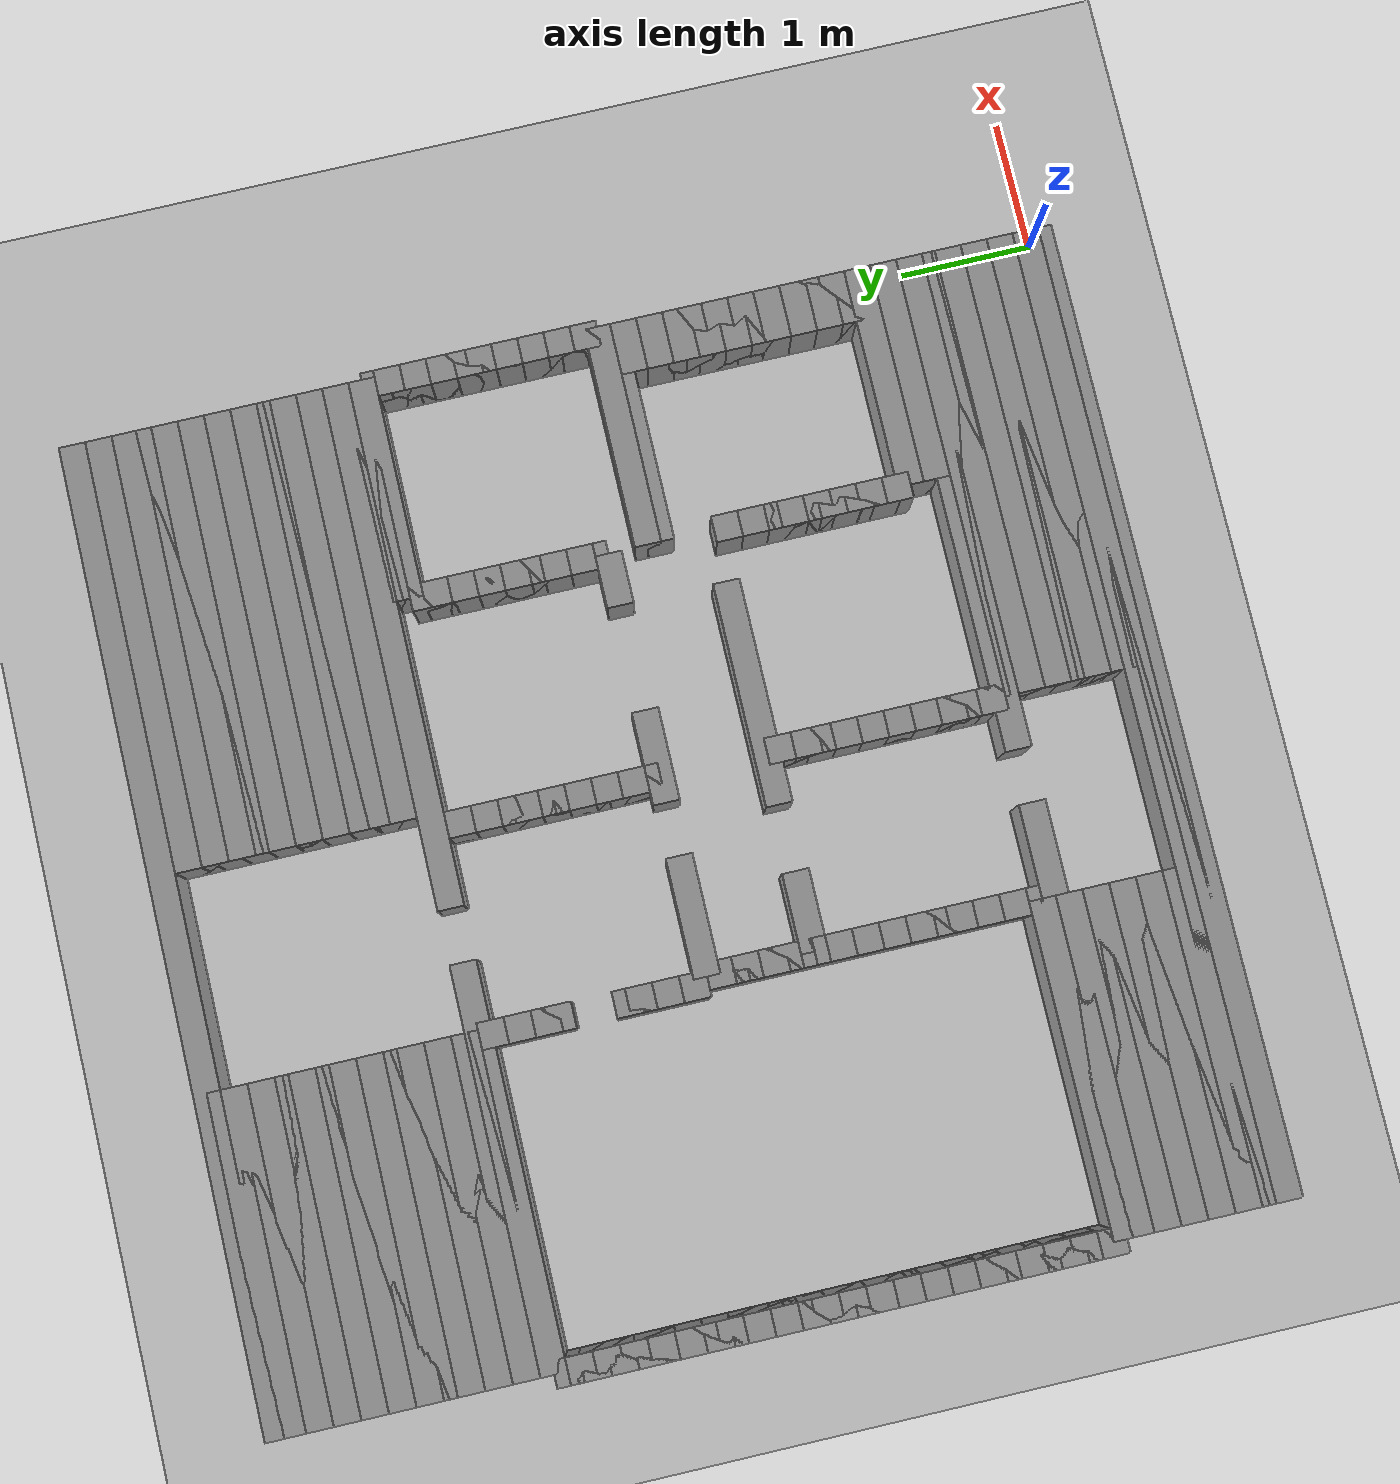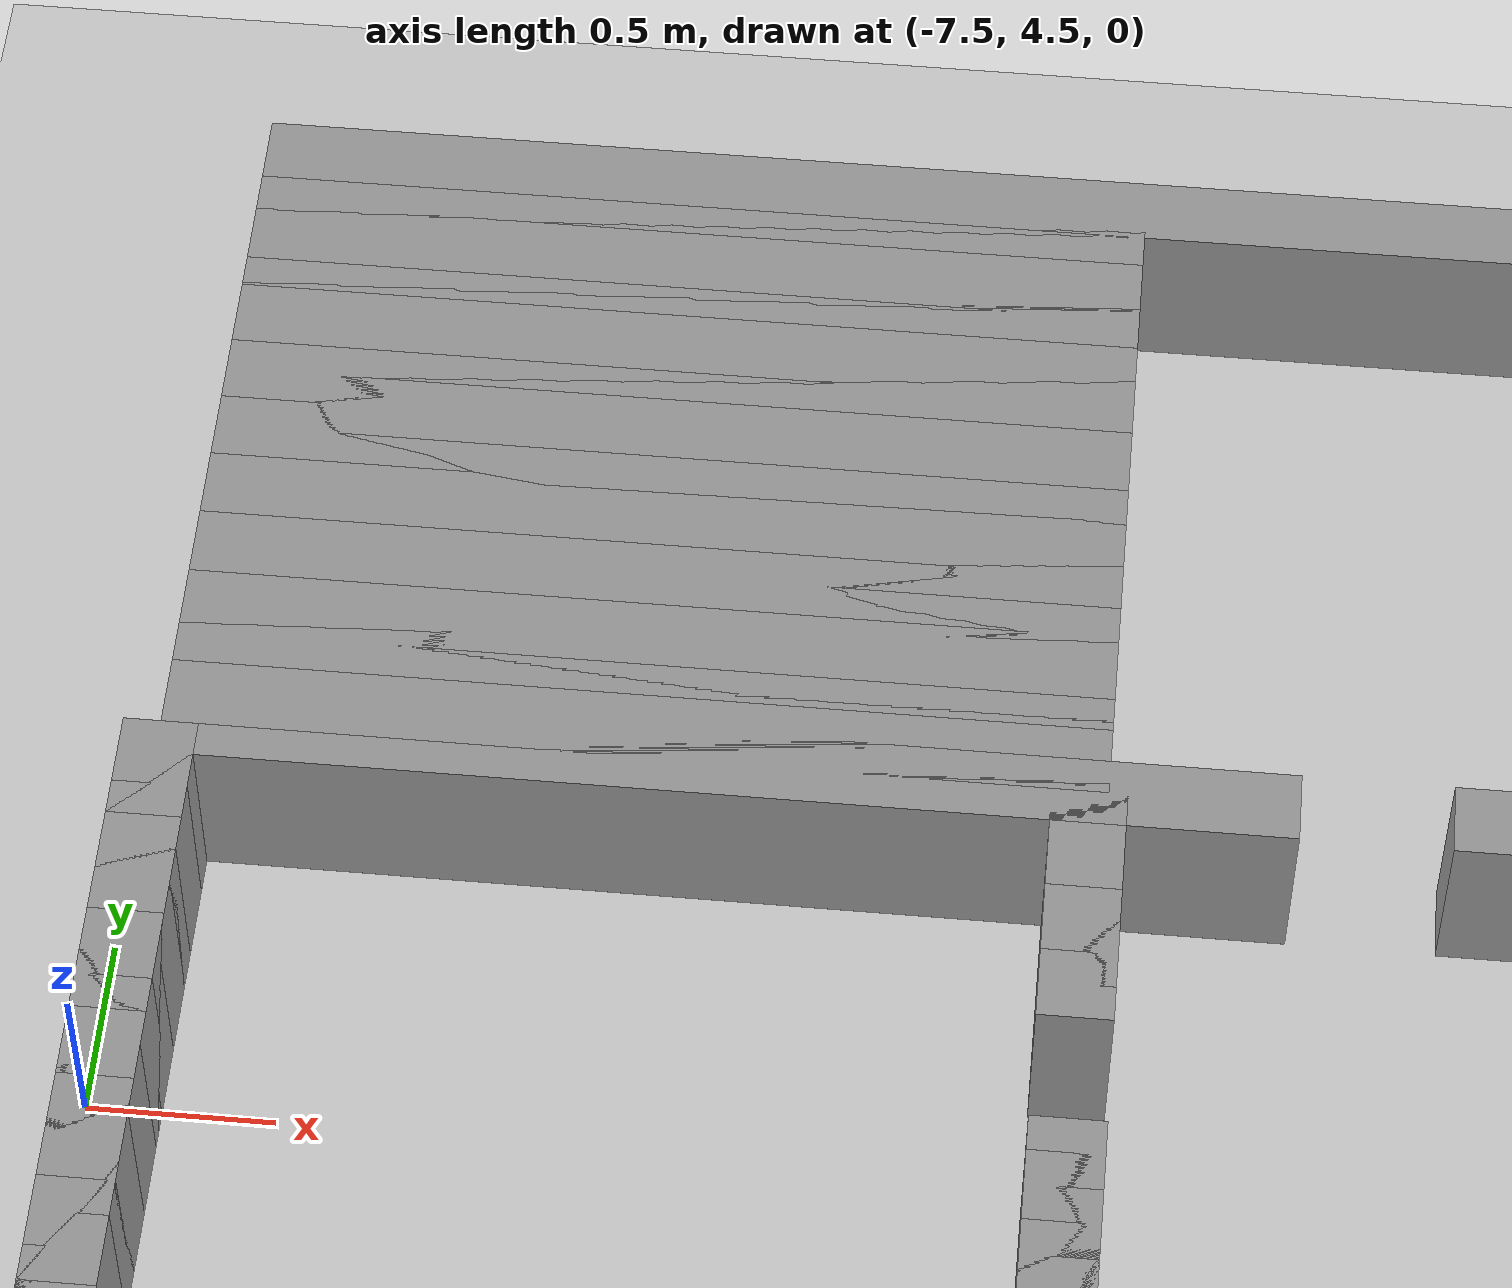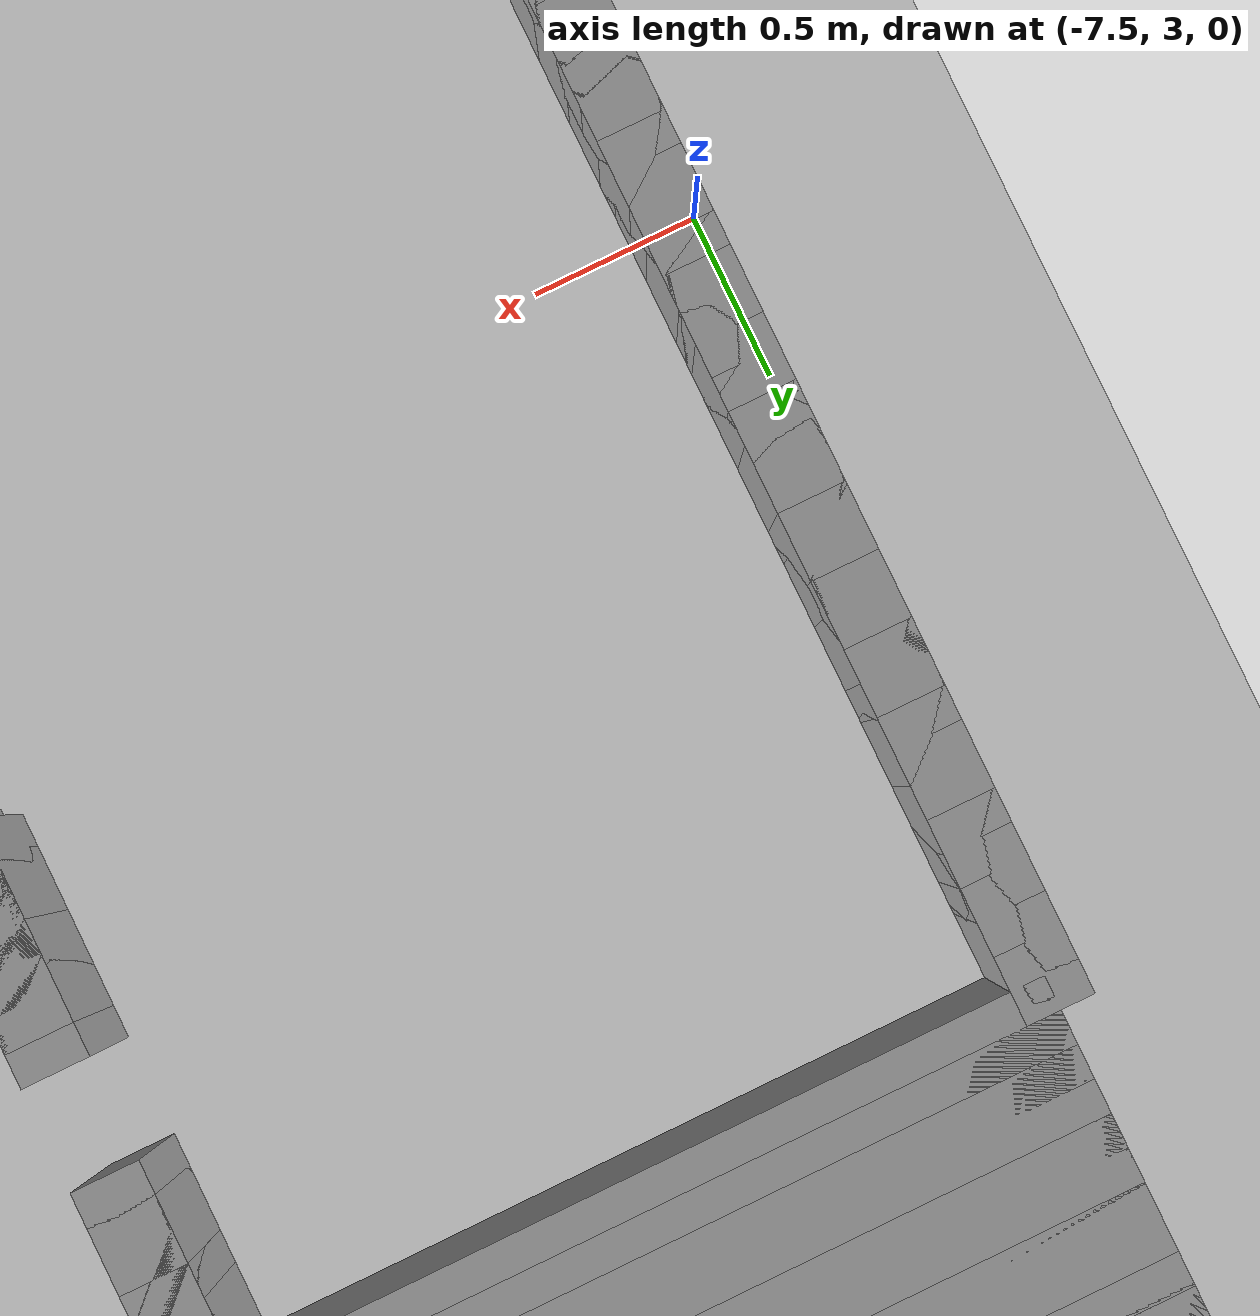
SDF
<?xml version="1.0" ?>
<sdf version="1.6">
	<world name="GridMap">
		<include>
			<uri>model://sun</uri>
		</include>
		<include>
			<uri>model://ground_plane</uri>
		</include>
		<physics type="ode">
			<real_time_update_rate>1000.0</real_time_update_rate>
			<max_step_size>0.001</max_step_size>
			<real_time_factor>1</real_time_factor>
			<ode>
				<solver>
					<type>quick</type>
					<iters>150</iters>
					<precon_iters>0</precon_iters>
					<sor>1.4</sor>
					<use_dynamic_moi_rescaling>1</use_dynamic_moi_rescaling>
				</solver>
				<constraints>
					<cfm>0.00001</cfm>
					<erp>0.2</erp>
					<contact_max_correcting_vel>2000.000000</contact_max_correcting_vel>
					<contact_surface_layer>0.01000</contact_surface_layer>
				</constraints>
			</ode>
		</physics>
		<model name="GridMap">
			<pose frame="">0 0 0 0 -0 0</pose>
			<link name="Wall_(37.0,0.0)">
				<collision name="Wall_(37.0,0.0)_Collision">
					<geometry>
						<box>
							<size>7.4 0.2 0.5</size>
						</box>
					</geometry>
					<pose frame="">-3.7 0.0 0.25 0 -0 0</pose>
				</collision>
				<inertial>
					<mass>0.5</mass>
					<pose>0 0.01 0 0 0 0</pose>
					<inertia>
						<ixx>0.004</ixx>
						<ixy>0.001</ixy>
						<ixz>0</ixz>
						<iyy>0.006</iyy>
						<iyz>0</iyz>
						<izz>0.007</izz>
					</inertia>
				</inertial>
				<visual name="Wall_(37.0,0.0)_Visual">
					<geometry>
						<box>
							<size>7.4 0.2 0.5</size>
						</box>
					</geometry>
					<pose frame="">-3.7 0.0 0.25 0 -0 0</pose>
					<material>
						<script>
							<uri>file://media/materials/scripts/gazebo.material</uri>
							<name>Gazebo/Grey</name>
						</script>
						<ambient>1 1 1 1</ambient>
					</material>
					<meta>
						<layer>0</layer>
					</meta>
				</visual>
				<pose frame="">0 0 0 0 -0 0</pose>
			</link>
			<link name="Wall_(37.0,1.0)">
				<collision name="Wall_(37.0,1.0)_Collision">
					<geometry>
						<box>
							<size>7.4 0.2 0.5</size>
						</box>
					</geometry>
					<pose frame="">-3.7 0.1 0.25 0 -0 0</pose>
				</collision>
				<inertial>
					<mass>0.5</mass>
					<pose>0 0.01 0 0 0 0</pose>
					<inertia>
						<ixx>0.004</ixx>
						<ixy>0.001</ixy>
						<ixz>0</ixz>
						<iyy>0.006</iyy>
						<iyz>0</iyz>
						<izz>0.007</izz>
					</inertia>
				</inertial>
				<visual name="Wall_(37.0,1.0)_Visual">
					<geometry>
						<box>
							<size>7.4 0.2 0.5</size>
						</box>
					</geometry>
					<pose frame="">-3.7 0.1 0.25 0 -0 0</pose>
					<material>
						<script>
							<uri>file://media/materials/scripts/gazebo.material</uri>
							<name>Gazebo/Grey</name>
						</script>
						<ambient>1 1 1 1</ambient>
					</material>
					<meta>
						<layer>0</layer>
					</meta>
				</visual>
				<pose frame="">0 0 0 0 -0 0</pose>
			</link>
			<link name="Wall_(17.0,2.0)">
				<collision name="Wall_(17.0,2.0)_Collision">
					<geometry>
						<box>
							<size>3.4000000000000004 0.2 0.5</size>
						</box>
					</geometry>
					<pose frame="">-1.7000000000000002 0.2 0.25 0 -0 0</pose>
				</collision>
				<inertial>
					<mass>0.5</mass>
					<pose>0 0.01 0 0 0 0</pose>
					<inertia>
						<ixx>0.004</ixx>
						<ixy>0.001</ixy>
						<ixz>0</ixz>
						<iyy>0.006</iyy>
						<iyz>0</iyz>
						<izz>0.007</izz>
					</inertia>
				</inertial>
				<visual name="Wall_(17.0,2.0)_Visual">
					<geometry>
						<box>
							<size>3.4000000000000004 0.2 0.5</size>
						</box>
					</geometry>
					<pose frame="">-1.7000000000000002 0.2 0.25 0 -0 0</pose>
					<material>
						<script>
							<uri>file://media/materials/scripts/gazebo.material</uri>
							<name>Gazebo/Grey</name>
						</script>
						<ambient>1 1 1 1</ambient>
					</material>
					<meta>
						<layer>0</layer>
					</meta>
				</visual>
				<pose frame="">0 0 0 0 -0 0</pose>
			</link>
			<link name="Wall_(61.5,2.0)">
				<collision name="Wall_(61.5,2.0)_Collision">
					<geometry>
						<box>
							<size>2.5 0.2 0.5</size>
						</box>
					</geometry>
					<pose frame="">-6.15 0.2 0.25 0 -0 0</pose>
				</collision>
				<inertial>
					<mass>0.5</mass>
					<pose>0 0.01 0 0 0 0</pose>
					<inertia>
						<ixx>0.004</ixx>
						<ixy>0.001</ixy>
						<ixz>0</ixz>
						<iyy>0.006</iyy>
						<iyz>0</iyz>
						<izz>0.007</izz>
					</inertia>
				</inertial>
				<visual name="Wall_(61.5,2.0)_Visual">
					<geometry>
						<box>
							<size>2.5 0.2 0.5</size>
						</box>
					</geometry>
					<pose frame="">-6.15 0.2 0.25 0 -0 0</pose>
					<material>
						<script>
							<uri>file://media/materials/scripts/gazebo.material</uri>
							<name>Gazebo/Grey</name>
						</script>
						<ambient>1 1 1 1</ambient>
					</material>
					<meta>
						<layer>0</layer>
					</meta>
				</visual>
				<pose frame="">0 0 0 0 -0 0</pose>
			</link>
			<link name="Wall_(17.0,3.0)">
				<collision name="Wall_(17.0,3.0)_Collision">
					<geometry>
						<box>
							<size>3.4000000000000004 0.2 0.5</size>
						</box>
					</geometry>
					<pose frame="">-1.7000000000000002 0.30000000000000004 0.25 0 -0 0</pose>
				</collision>
				<inertial>
					<mass>0.5</mass>
					<pose>0 0.01 0 0 0 0</pose>
					<inertia>
						<ixx>0.004</ixx>
						<ixy>0.001</ixy>
						<ixz>0</ixz>
						<iyy>0.006</iyy>
						<iyz>0</iyz>
						<izz>0.007</izz>
					</inertia>
				</inertial>
				<visual name="Wall_(17.0,3.0)_Visual">
					<geometry>
						<box>
							<size>3.4000000000000004 0.2 0.5</size>
						</box>
					</geometry>
					<pose frame="">-1.7000000000000002 0.30000000000000004 0.25 0 -0 0</pose>
					<material>
						<script>
							<uri>file://media/materials/scripts/gazebo.material</uri>
							<name>Gazebo/Grey</name>
						</script>
						<ambient>1 1 1 1</ambient>
					</material>
					<meta>
						<layer>0</layer>
					</meta>
				</visual>
				<pose frame="">0 0 0 0 -0 0</pose>
			</link>
			<link name="Wall_(61.5,3.0)">
				<collision name="Wall_(61.5,3.0)_Collision">
					<geometry>
						<box>
							<size>2.5 0.2 0.5</size>
						</box>
					</geometry>
					<pose frame="">-6.15 0.30000000000000004 0.25 0 -0 0</pose>
				</collision>
				<inertial>
					<mass>0.5</mass>
					<pose>0 0.01 0 0 0 0</pose>
					<inertia>
						<ixx>0.004</ixx>
						<ixy>0.001</ixy>
						<ixz>0</ixz>
						<iyy>0.006</iyy>
						<iyz>0</iyz>
						<izz>0.007</izz>
					</inertia>
				</inertial>
				<visual name="Wall_(61.5,3.0)_Visual">
					<geometry>
						<box>
							<size>2.5 0.2 0.5</size>
						</box>
					</geometry>
					<pose frame="">-6.15 0.30000000000000004 0.25 0 -0 0</pose>
					<material>
						<script>
							<uri>file://media/materials/scripts/gazebo.material</uri>
							<name>Gazebo/Grey</name>
						</script>
						<ambient>1 1 1 1</ambient>
					</material>
					<meta>
						<layer>0</layer>
					</meta>
				</visual>
				<pose frame="">0 0 0 0 -0 0</pose>
			</link>
			<link name="Wall_(17.0,4.0)">
				<collision name="Wall_(17.0,4.0)_Collision">
					<geometry>
						<box>
							<size>3.4000000000000004 0.2 0.5</size>
						</box>
					</geometry>
					<pose frame="">-1.7000000000000002 0.4 0.25 0 -0 0</pose>
				</collision>
				<inertial>
					<mass>0.5</mass>
					<pose>0 0.01 0 0 0 0</pose>
					<inertia>
						<ixx>0.004</ixx>
						<ixy>0.001</ixy>
						<ixz>0</ixz>
						<iyy>0.006</iyy>
						<iyz>0</iyz>
						<izz>0.007</izz>
					</inertia>
				</inertial>
				<visual name="Wall_(17.0,4.0)_Visual">
					<geometry>
						<box>
							<size>3.4000000000000004 0.2 0.5</size>
						</box>
					</geometry>
					<pose frame="">-1.7000000000000002 0.4 0.25 0 -0 0</pose>
					<material>
						<script>
							<uri>file://media/materials/scripts/gazebo.material</uri>
							<name>Gazebo/Grey</name>
						</script>
						<ambient>1 1 1 1</ambient>
					</material>
					<meta>
						<layer>0</layer>
					</meta>
				</visual>
				<pose frame="">0 0 0 0 -0 0</pose>
			</link>
			<link name="Wall_(61.5,4.0)">
				<collision name="Wall_(61.5,4.0)_Collision">
					<geometry>
						<box>
							<size>2.5 0.2 0.5</size>
						</box>
					</geometry>
					<pose frame="">-6.15 0.4 0.25 0 -0 0</pose>
				</collision>
				<inertial>
					<mass>0.5</mass>
					<pose>0 0.01 0 0 0 0</pose>
					<inertia>
						<ixx>0.004</ixx>
						<ixy>0.001</ixy>
						<ixz>0</ixz>
						<iyy>0.006</iyy>
						<iyz>0</iyz>
						<izz>0.007</izz>
					</inertia>
				</inertial>
				<visual name="Wall_(61.5,4.0)_Visual">
					<geometry>
						<box>
							<size>2.5 0.2 0.5</size>
						</box>
					</geometry>
					<pose frame="">-6.15 0.4 0.25 0 -0 0</pose>
					<material>
						<script>
							<uri>file://media/materials/scripts/gazebo.material</uri>
							<name>Gazebo/Grey</name>
						</script>
						<ambient>1 1 1 1</ambient>
					</material>
					<meta>
						<layer>0</layer>
					</meta>
				</visual>
				<pose frame="">0 0 0 0 -0 0</pose>
			</link>
			<link name="Wall_(17.0,5.0)">
				<collision name="Wall_(17.0,5.0)_Collision">
					<geometry>
						<box>
							<size>3.4000000000000004 0.2 0.5</size>
						</box>
					</geometry>
					<pose frame="">-1.7000000000000002 0.5 0.25 0 -0 0</pose>
				</collision>
				<inertial>
					<mass>0.5</mass>
					<pose>0 0.01 0 0 0 0</pose>
					<inertia>
						<ixx>0.004</ixx>
						<ixy>0.001</ixy>
						<ixz>0</ixz>
						<iyy>0.006</iyy>
						<iyz>0</iyz>
						<izz>0.007</izz>
					</inertia>
				</inertial>
				<visual name="Wall_(17.0,5.0)_Visual">
					<geometry>
						<box>
							<size>3.4000000000000004 0.2 0.5</size>
						</box>
					</geometry>
					<pose frame="">-1.7000000000000002 0.5 0.25 0 -0 0</pose>
					<material>
						<script>
							<uri>file://media/materials/scripts/gazebo.material</uri>
							<name>Gazebo/Grey</name>
						</script>
						<ambient>1 1 1 1</ambient>
					</material>
					<meta>
						<layer>0</layer>
					</meta>
				</visual>
				<pose frame="">0 0 0 0 -0 0</pose>
			</link>
			<link name="Wall_(61.5,5.0)">
				<collision name="Wall_(61.5,5.0)_Collision">
					<geometry>
						<box>
							<size>2.5 0.2 0.5</size>
						</box>
					</geometry>
					<pose frame="">-6.15 0.5 0.25 0 -0 0</pose>
				</collision>
				<inertial>
					<mass>0.5</mass>
					<pose>0 0.01 0 0 0 0</pose>
					<inertia>
						<ixx>0.004</ixx>
						<ixy>0.001</ixy>
						<ixz>0</ixz>
						<iyy>0.006</iyy>
						<iyz>0</iyz>
						<izz>0.007</izz>
					</inertia>
				</inertial>
				<visual name="Wall_(61.5,5.0)_Visual">
					<geometry>
						<box>
							<size>2.5 0.2 0.5</size>
						</box>
					</geometry>
					<pose frame="">-6.15 0.5 0.25 0 -0 0</pose>
					<material>
						<script>
							<uri>file://media/materials/scripts/gazebo.material</uri>
							<name>Gazebo/Grey</name>
						</script>
						<ambient>1 1 1 1</ambient>
					</material>
					<meta>
						<layer>0</layer>
					</meta>
				</visual>
				<pose frame="">0 0 0 0 -0 0</pose>
			</link>
			<link name="Wall_(17.0,6.0)">
				<collision name="Wall_(17.0,6.0)_Collision">
					<geometry>
						<box>
							<size>3.4000000000000004 0.2 0.5</size>
						</box>
					</geometry>
					<pose frame="">-1.7000000000000002 0.6000000000000001 0.25 0 -0 0</pose>
				</collision>
				<inertial>
					<mass>0.5</mass>
					<pose>0 0.01 0 0 0 0</pose>
					<inertia>
						<ixx>0.004</ixx>
						<ixy>0.001</ixy>
						<ixz>0</ixz>
						<iyy>0.006</iyy>
						<iyz>0</iyz>
						<izz>0.007</izz>
					</inertia>
				</inertial>
				<visual name="Wall_(17.0,6.0)_Visual">
					<geometry>
						<box>
							<size>3.4000000000000004 0.2 0.5</size>
						</box>
					</geometry>
					<pose frame="">-1.7000000000000002 0.6000000000000001 0.25 0 -0 0</pose>
					<material>
						<script>
							<uri>file://media/materials/scripts/gazebo.material</uri>
							<name>Gazebo/Grey</name>
						</script>
						<ambient>1 1 1 1</ambient>
					</material>
					<meta>
						<layer>0</layer>
					</meta>
				</visual>
				<pose frame="">0 0 0 0 -0 0</pose>
			</link>
			<link name="Wall_(61.5,6.0)">
				<collision name="Wall_(61.5,6.0)_Collision">
					<geometry>
						<box>
							<size>2.5 0.2 0.5</size>
						</box>
					</geometry>
					<pose frame="">-6.15 0.6000000000000001 0.25 0 -0 0</pose>
				</collision>
				<inertial>
					<mass>0.5</mass>
					<pose>0 0.01 0 0 0 0</pose>
					<inertia>
						<ixx>0.004</ixx>
						<ixy>0.001</ixy>
						<ixz>0</ixz>
						<iyy>0.006</iyy>
						<iyz>0</iyz>
						<izz>0.007</izz>
					</inertia>
				</inertial>
				<visual name="Wall_(61.5,6.0)_Visual">
					<geometry>
						<box>
							<size>2.5 0.2 0.5</size>
						</box>
					</geometry>
					<pose frame="">-6.15 0.6000000000000001 0.25 0 -0 0</pose>
					<material>
						<script>
							<uri>file://media/materials/scripts/gazebo.material</uri>
							<name>Gazebo/Grey</name>
						</script>
						<ambient>1 1 1 1</ambient>
					</material>
					<meta>
						<layer>0</layer>
					</meta>
				</visual>
				<pose frame="">0 0 0 0 -0 0</pose>
			</link>
			<link name="Wall_(17.0,7.0)">
				<collision name="Wall_(17.0,7.0)_Collision">
					<geometry>
						<box>
							<size>3.4000000000000004 0.2 0.5</size>
						</box>
					</geometry>
					<pose frame="">-1.7000000000000002 0.7000000000000001 0.25 0 -0 0</pose>
				</collision>
				<inertial>
					<mass>0.5</mass>
					<pose>0 0.01 0 0 0 0</pose>
					<inertia>
						<ixx>0.004</ixx>
						<ixy>0.001</ixy>
						<ixz>0</ixz>
						<iyy>0.006</iyy>
						<iyz>0</iyz>
						<izz>0.007</izz>
					</inertia>
				</inertial>
				<visual name="Wall_(17.0,7.0)_Visual">
					<geometry>
						<box>
							<size>3.4000000000000004 0.2 0.5</size>
						</box>
					</geometry>
					<pose frame="">-1.7000000000000002 0.7000000000000001 0.25 0 -0 0</pose>
					<material>
						<script>
							<uri>file://media/materials/scripts/gazebo.material</uri>
							<name>Gazebo/Grey</name>
						</script>
						<ambient>1 1 1 1</ambient>
					</material>
					<meta>
						<layer>0</layer>
					</meta>
				</visual>
				<pose frame="">0 0 0 0 -0 0</pose>
			</link>
			<link name="Wall_(61.5,7.0)">
				<collision name="Wall_(61.5,7.0)_Collision">
					<geometry>
						<box>
							<size>2.5 0.2 0.5</size>
						</box>
					</geometry>
					<pose frame="">-6.15 0.7000000000000001 0.25 0 -0 0</pose>
				</collision>
				<inertial>
					<mass>0.5</mass>
					<pose>0 0.01 0 0 0 0</pose>
					<inertia>
						<ixx>0.004</ixx>
						<ixy>0.001</ixy>
						<ixz>0</ixz>
						<iyy>0.006</iyy>
						<iyz>0</iyz>
						<izz>0.007</izz>
					</inertia>
				</inertial>
				<visual name="Wall_(61.5,7.0)_Visual">
					<geometry>
						<box>
							<size>2.5 0.2 0.5</size>
						</box>
					</geometry>
					<pose frame="">-6.15 0.7000000000000001 0.25 0 -0 0</pose>
					<material>
						<script>
							<uri>file://media/materials/scripts/gazebo.material</uri>
							<name>Gazebo/Grey</name>
						</script>
						<ambient>1 1 1 1</ambient>
					</material>
					<meta>
						<layer>0</layer>
					</meta>
				</visual>
				<pose frame="">0 0 0 0 -0 0</pose>
			</link>
			<link name="Wall_(17.0,8.0)">
				<collision name="Wall_(17.0,8.0)_Collision">
					<geometry>
						<box>
							<size>3.4000000000000004 0.2 0.5</size>
						</box>
					</geometry>
					<pose frame="">-1.7000000000000002 0.8 0.25 0 -0 0</pose>
				</collision>
				<inertial>
					<mass>0.5</mass>
					<pose>0 0.01 0 0 0 0</pose>
					<inertia>
						<ixx>0.004</ixx>
						<ixy>0.001</ixy>
						<ixz>0</ixz>
						<iyy>0.006</iyy>
						<iyz>0</iyz>
						<izz>0.007</izz>
					</inertia>
				</inertial>
				<visual name="Wall_(17.0,8.0)_Visual">
					<geometry>
						<box>
							<size>3.4000000000000004 0.2 0.5</size>
						</box>
					</geometry>
					<pose frame="">-1.7000000000000002 0.8 0.25 0 -0 0</pose>
					<material>
						<script>
							<uri>file://media/materials/scripts/gazebo.material</uri>
							<name>Gazebo/Grey</name>
						</script>
						<ambient>1 1 1 1</ambient>
					</material>
					<meta>
						<layer>0</layer>
					</meta>
				</visual>
				<pose frame="">0 0 0 0 -0 0</pose>
			</link>
			<link name="Wall_(61.5,8.0)">
				<collision name="Wall_(61.5,8.0)_Collision">
					<geometry>
						<box>
							<size>2.5 0.2 0.5</size>
						</box>
					</geometry>
					<pose frame="">-6.15 0.8 0.25 0 -0 0</pose>
				</collision>
				<inertial>
					<mass>0.5</mass>
					<pose>0 0.01 0 0 0 0</pose>
					<inertia>
						<ixx>0.004</ixx>
						<ixy>0.001</ixy>
						<ixz>0</ixz>
						<iyy>0.006</iyy>
						<iyz>0</iyz>
						<izz>0.007</izz>
					</inertia>
				</inertial>
				<visual name="Wall_(61.5,8.0)_Visual">
					<geometry>
						<box>
							<size>2.5 0.2 0.5</size>
						</box>
					</geometry>
					<pose frame="">-6.15 0.8 0.25 0 -0 0</pose>
					<material>
						<script>
							<uri>file://media/materials/scripts/gazebo.material</uri>
							<name>Gazebo/Grey</name>
						</script>
						<ambient>1 1 1 1</ambient>
					</material>
					<meta>
						<layer>0</layer>
					</meta>
				</visual>
				<pose frame="">0 0 0 0 -0 0</pose>
			</link>
			<link name="Wall_(17.0,9.0)">
				<collision name="Wall_(17.0,9.0)_Collision">
					<geometry>
						<box>
							<size>3.4000000000000004 0.2 0.5</size>
						</box>
					</geometry>
					<pose frame="">-1.7000000000000002 0.9 0.25 0 -0 0</pose>
				</collision>
				<inertial>
					<mass>0.5</mass>
					<pose>0 0.01 0 0 0 0</pose>
					<inertia>
						<ixx>0.004</ixx>
						<ixy>0.001</ixy>
						<ixz>0</ixz>
						<iyy>0.006</iyy>
						<iyz>0</iyz>
						<izz>0.007</izz>
					</inertia>
				</inertial>
				<visual name="Wall_(17.0,9.0)_Visual">
					<geometry>
						<box>
							<size>3.4000000000000004 0.2 0.5</size>
						</box>
					</geometry>
					<pose frame="">-1.7000000000000002 0.9 0.25 0 -0 0</pose>
					<material>
						<script>
							<uri>file://media/materials/scripts/gazebo.material</uri>
							<name>Gazebo/Grey</name>
						</script>
						<ambient>1 1 1 1</ambient>
					</material>
					<meta>
						<layer>0</layer>
					</meta>
				</visual>
				<pose frame="">0 0 0 0 -0 0</pose>
			</link>
			<link name="Wall_(61.5,9.0)">
				<collision name="Wall_(61.5,9.0)_Collision">
					<geometry>
						<box>
							<size>2.5 0.2 0.5</size>
						</box>
					</geometry>
					<pose frame="">-6.15 0.9 0.25 0 -0 0</pose>
				</collision>
				<inertial>
					<mass>0.5</mass>
					<pose>0 0.01 0 0 0 0</pose>
					<inertia>
						<ixx>0.004</ixx>
						<ixy>0.001</ixy>
						<ixz>0</ixz>
						<iyy>0.006</iyy>
						<iyz>0</iyz>
						<izz>0.007</izz>
					</inertia>
				</inertial>
				<visual name="Wall_(61.5,9.0)_Visual">
					<geometry>
						<box>
							<size>2.5 0.2 0.5</size>
						</box>
					</geometry>
					<pose frame="">-6.15 0.9 0.25 0 -0 0</pose>
					<material>
						<script>
							<uri>file://media/materials/scripts/gazebo.material</uri>
							<name>Gazebo/Grey</name>
						</script>
						<ambient>1 1 1 1</ambient>
					</material>
					<meta>
						<layer>0</layer>
					</meta>
				</visual>
				<pose frame="">0 0 0 0 -0 0</pose>
			</link>
			<link name="Wall_(17.0,10.0)">
				<collision name="Wall_(17.0,10.0)_Collision">
					<geometry>
						<box>
							<size>3.4000000000000004 0.2 0.5</size>
						</box>
					</geometry>
					<pose frame="">-1.7000000000000002 1.0 0.25 0 -0 0</pose>
				</collision>
				<inertial>
					<mass>0.5</mass>
					<pose>0 0.01 0 0 0 0</pose>
					<inertia>
						<ixx>0.004</ixx>
						<ixy>0.001</ixy>
						<ixz>0</ixz>
						<iyy>0.006</iyy>
						<iyz>0</iyz>
						<izz>0.007</izz>
					</inertia>
				</inertial>
				<visual name="Wall_(17.0,10.0)_Visual">
					<geometry>
						<box>
							<size>3.4000000000000004 0.2 0.5</size>
						</box>
					</geometry>
					<pose frame="">-1.7000000000000002 1.0 0.25 0 -0 0</pose>
					<material>
						<script>
							<uri>file://media/materials/scripts/gazebo.material</uri>
							<name>Gazebo/Grey</name>
						</script>
						<ambient>1 1 1 1</ambient>
					</material>
					<meta>
						<layer>0</layer>
					</meta>
				</visual>
				<pose frame="">0 0 0 0 -0 0</pose>
			</link>
			<link name="Wall_(61.5,10.0)">
				<collision name="Wall_(61.5,10.0)_Collision">
					<geometry>
						<box>
							<size>2.5 0.2 0.5</size>
						</box>
					</geometry>
					<pose frame="">-6.15 1.0 0.25 0 -0 0</pose>
				</collision>
				<inertial>
					<mass>0.5</mass>
					<pose>0 0.01 0 0 0 0</pose>
					<inertia>
						<ixx>0.004</ixx>
						<ixy>0.001</ixy>
						<ixz>0</ixz>
						<iyy>0.006</iyy>
						<iyz>0</iyz>
						<izz>0.007</izz>
					</inertia>
				</inertial>
				<visual name="Wall_(61.5,10.0)_Visual">
					<geometry>
						<box>
							<size>2.5 0.2 0.5</size>
						</box>
					</geometry>
					<pose frame="">-6.15 1.0 0.25 0 -0 0</pose>
					<material>
						<script>
							<uri>file://media/materials/scripts/gazebo.material</uri>
							<name>Gazebo/Grey</name>
						</script>
						<ambient>1 1 1 1</ambient>
					</material>
					<meta>
						<layer>0</layer>
					</meta>
				</visual>
				<pose frame="">0 0 0 0 -0 0</pose>
			</link>
			<link name="Wall_(19.0,11.0)">
				<collision name="Wall_(19.0,11.0)_Collision">
					<geometry>
						<box>
							<size>3.8000000000000003 0.2 0.5</size>
						</box>
					</geometry>
					<pose frame="">-1.9000000000000001 1.1 0.25 0 -0 0</pose>
				</collision>
				<inertial>
					<mass>0.5</mass>
					<pose>0 0.01 0 0 0 0</pose>
					<inertia>
						<ixx>0.004</ixx>
						<ixy>0.001</ixy>
						<ixz>0</ixz>
						<iyy>0.006</iyy>
						<iyz>0</iyz>
						<izz>0.007</izz>
					</inertia>
				</inertial>
				<visual name="Wall_(19.0,11.0)_Visual">
					<geometry>
						<box>
							<size>3.8000000000000003 0.2 0.5</size>
						</box>
					</geometry>
					<pose frame="">-1.9000000000000001 1.1 0.25 0 -0 0</pose>
					<material>
						<script>
							<uri>file://media/materials/scripts/gazebo.material</uri>
							<name>Gazebo/Grey</name>
						</script>
						<ambient>1 1 1 1</ambient>
					</material>
					<meta>
						<layer>0</layer>
					</meta>
				</visual>
				<pose frame="">0 0 0 0 -0 0</pose>
			</link>
			<link name="Wall_(58.0,11.0)">
				<collision name="Wall_(58.0,11.0)_Collision">
					<geometry>
						<box>
							<size>3.2 0.2 0.5</size>
						</box>
					</geometry>
					<pose frame="">-5.800000000000001 1.1 0.25 0 -0 0</pose>
				</collision>
				<inertial>
					<mass>0.5</mass>
					<pose>0 0.01 0 0 0 0</pose>
					<inertia>
						<ixx>0.004</ixx>
						<ixy>0.001</ixy>
						<ixz>0</ixz>
						<iyy>0.006</iyy>
						<iyz>0</iyz>
						<izz>0.007</izz>
					</inertia>
				</inertial>
				<visual name="Wall_(58.0,11.0)_Visual">
					<geometry>
						<box>
							<size>3.2 0.2 0.5</size>
						</box>
					</geometry>
					<pose frame="">-5.800000000000001 1.1 0.25 0 -0 0</pose>
					<material>
						<script>
							<uri>file://media/materials/scripts/gazebo.material</uri>
							<name>Gazebo/Grey</name>
						</script>
						<ambient>1 1 1 1</ambient>
					</material>
					<meta>
						<layer>0</layer>
					</meta>
				</visual>
				<pose frame="">0 0 0 0 -0 0</pose>
			</link>
			<link name="Wall_(8.5,12.0)">
				<collision name="Wall_(8.5,12.0)_Collision">
					<geometry>
						<box>
							<size>1.7000000000000002 0.2 0.5</size>
						</box>
					</geometry>
					<pose frame="">-0.8500000000000001 1.2000000000000002 0.25 0 -0 0</pose>
				</collision>
				<inertial>
					<mass>0.5</mass>
					<pose>0 0.01 0 0 0 0</pose>
					<inertia>
						<ixx>0.004</ixx>
						<ixy>0.001</ixy>
						<ixz>0</ixz>
						<iyy>0.006</iyy>
						<iyz>0</iyz>
						<izz>0.007</izz>
					</inertia>
				</inertial>
				<visual name="Wall_(8.5,12.0)_Visual">
					<geometry>
						<box>
							<size>1.7000000000000002 0.2 0.5</size>
						</box>
					</geometry>
					<pose frame="">-0.8500000000000001 1.2000000000000002 0.25 0 -0 0</pose>
					<material>
						<script>
							<uri>file://media/materials/scripts/gazebo.material</uri>
							<name>Gazebo/Grey</name>
						</script>
						<ambient>1 1 1 1</ambient>
					</material>
					<meta>
						<layer>0</layer>
					</meta>
				</visual>
				<pose frame="">0 0 0 0 -0 0</pose>
			</link>
			<link name="Wall_(34.0,12.0)">
				<collision name="Wall_(34.0,12.0)_Collision">
					<geometry>
						<box>
							<size>0.2 0.2 0.5</size>
						</box>
					</geometry>
					<pose frame="">-3.4000000000000004 1.2000000000000002 0.25 0 -0 0</pose>
				</collision>
				<inertial>
					<mass>0.5</mass>
					<pose>0 0.01 0 0 0 0</pose>
					<inertia>
						<ixx>0.004</ixx>
						<ixy>0.001</ixy>
						<ixz>0</ixz>
						<iyy>0.006</iyy>
						<iyz>0</iyz>
						<izz>0.007</izz>
					</inertia>
				</inertial>
				<visual name="Wall_(34.0,12.0)_Visual">
					<geometry>
						<box>
							<size>0.2 0.2 0.5</size>
						</box>
					</geometry>
					<pose frame="">-3.4000000000000004 1.2000000000000002 0.25 0 -0 0</pose>
					<material>
						<script>
							<uri>file://media/materials/scripts/gazebo.material</uri>
							<name>Gazebo/Grey</name>
						</script>
						<ambient>1 1 1 1</ambient>
					</material>
					<meta>
						<layer>0</layer>
					</meta>
				</visual>
				<pose frame="">0 0 0 0 -0 0</pose>
			</link>
			<link name="Wall_(61.5,12.0)">
				<collision name="Wall_(61.5,12.0)_Collision">
					<geometry>
						<box>
							<size>2.5 0.2 0.5</size>
						</box>
					</geometry>
					<pose frame="">-6.15 1.2000000000000002 0.25 0 -0 0</pose>
				</collision>
				<inertial>
					<mass>0.5</mass>
					<pose>0 0.01 0 0 0 0</pose>
					<inertia>
						<ixx>0.004</ixx>
						<ixy>0.001</ixy>
						<ixz>0</ixz>
						<iyy>0.006</iyy>
						<iyz>0</iyz>
						<izz>0.007</izz>
					</inertia>
				</inertial>
				<visual name="Wall_(61.5,12.0)_Visual">
					<geometry>
						<box>
							<size>2.5 0.2 0.5</size>
						</box>
					</geometry>
					<pose frame="">-6.15 1.2000000000000002 0.25 0 -0 0</pose>
					<material>
						<script>
							<uri>file://media/materials/scripts/gazebo.material</uri>
							<name>Gazebo/Grey</name>
						</script>
						<ambient>1 1 1 1</ambient>
					</material>
					<meta>
						<layer>0</layer>
					</meta>
				</visual>
				<pose frame="">0 0 0 0 -0 0</pose>
			</link>
			<link name="Wall_(8.5,13.0)">
				<collision name="Wall_(8.5,13.0)_Collision">
					<geometry>
						<box>
							<size>1.7000000000000002 0.2 0.5</size>
						</box>
					</geometry>
					<pose frame="">-0.8500000000000001 1.3 0.25 0 -0 0</pose>
				</collision>
				<inertial>
					<mass>0.5</mass>
					<pose>0 0.01 0 0 0 0</pose>
					<inertia>
						<ixx>0.004</ixx>
						<ixy>0.001</ixy>
						<ixz>0</ixz>
						<iyy>0.006</iyy>
						<iyz>0</iyz>
						<izz>0.007</izz>
					</inertia>
				</inertial>
				<visual name="Wall_(8.5,13.0)_Visual">
					<geometry>
						<box>
							<size>1.7000000000000002 0.2 0.5</size>
						</box>
					</geometry>
					<pose frame="">-0.8500000000000001 1.3 0.25 0 -0 0</pose>
					<material>
						<script>
							<uri>file://media/materials/scripts/gazebo.material</uri>
							<name>Gazebo/Grey</name>
						</script>
						<ambient>1 1 1 1</ambient>
					</material>
					<meta>
						<layer>0</layer>
					</meta>
				</visual>
				<pose frame="">0 0 0 0 -0 0</pose>
			</link>
			<link name="Wall_(34.0,13.0)">
				<collision name="Wall_(34.0,13.0)_Collision">
					<geometry>
						<box>
							<size>0.2 0.2 0.5</size>
						</box>
					</geometry>
					<pose frame="">-3.4000000000000004 1.3 0.25 0 -0 0</pose>
				</collision>
				<inertial>
					<mass>0.5</mass>
					<pose>0 0.01 0 0 0 0</pose>
					<inertia>
						<ixx>0.004</ixx>
						<ixy>0.001</ixy>
						<ixz>0</ixz>
						<iyy>0.006</iyy>
						<iyz>0</iyz>
						<izz>0.007</izz>
					</inertia>
				</inertial>
				<visual name="Wall_(34.0,13.0)_Visual">
					<geometry>
						<box>
							<size>0.2 0.2 0.5</size>
						</box>
					</geometry>
					<pose frame="">-3.4000000000000004 1.3 0.25 0 -0 0</pose>
					<material>
						<script>
							<uri>file://media/materials/scripts/gazebo.material</uri>
							<name>Gazebo/Grey</name>
						</script>
						<ambient>1 1 1 1</ambient>
					</material>
					<meta>
						<layer>0</layer>
					</meta>
				</visual>
				<pose frame="">0 0 0 0 -0 0</pose>
			</link>
			<link name="Wall_(49.0,13.0)">
				<collision name="Wall_(49.0,13.0)_Collision">
					<geometry>
						<box>
							<size>0.2 0.2 0.5</size>
						</box>
					</geometry>
					<pose frame="">-4.9 1.3 0.25 0 -0 0</pose>
				</collision>
				<inertial>
					<mass>0.5</mass>
					<pose>0 0.01 0 0 0 0</pose>
					<inertia>
						<ixx>0.004</ixx>
						<ixy>0.001</ixy>
						<ixz>0</ixz>
						<iyy>0.006</iyy>
						<iyz>0</iyz>
						<izz>0.007</izz>
					</inertia>
				</inertial>
				<visual name="Wall_(49.0,13.0)_Visual">
					<geometry>
						<box>
							<size>0.2 0.2 0.5</size>
						</box>
					</geometry>
					<pose frame="">-4.9 1.3 0.25 0 -0 0</pose>
					<material>
						<script>
							<uri>file://media/materials/scripts/gazebo.material</uri>
							<name>Gazebo/Grey</name>
						</script>
						<ambient>1 1 1 1</ambient>
					</material>
					<meta>
						<layer>0</layer>
					</meta>
				</visual>
				<pose frame="">0 0 0 0 -0 0</pose>
			</link>
			<link name="Wall_(74.0,13.0)">
				<collision name="Wall_(74.0,13.0)_Collision">
					<geometry>
						<box>
							<size>0.2 0.2 0.5</size>
						</box>
					</geometry>
					<pose frame="">-7.4 1.3 0.25 0 -0 0</pose>
				</collision>
				<inertial>
					<mass>0.5</mass>
					<pose>0 0.01 0 0 0 0</pose>
					<inertia>
						<ixx>0.004</ixx>
						<ixy>0.001</ixy>
						<ixz>0</ixz>
						<iyy>0.006</iyy>
						<iyz>0</iyz>
						<izz>0.007</izz>
					</inertia>
				</inertial>
				<visual name="Wall_(74.0,13.0)_Visual">
					<geometry>
						<box>
							<size>0.2 0.2 0.5</size>
						</box>
					</geometry>
					<pose frame="">-7.4 1.3 0.25 0 -0 0</pose>
					<material>
						<script>
							<uri>file://media/materials/scripts/gazebo.material</uri>
							<name>Gazebo/Grey</name>
						</script>
						<ambient>1 1 1 1</ambient>
					</material>
					<meta>
						<layer>0</layer>
					</meta>
				</visual>
				<pose frame="">0 0 0 0 -0 0</pose>
			</link>
			<link name="Wall_(8.5,14.0)">
				<collision name="Wall_(8.5,14.0)_Collision">
					<geometry>
						<box>
							<size>1.7000000000000002 0.2 0.5</size>
						</box>
					</geometry>
					<pose frame="">-0.8500000000000001 1.4000000000000001 0.25 0 -0 0</pose>
				</collision>
				<inertial>
					<mass>0.5</mass>
					<pose>0 0.01 0 0 0 0</pose>
					<inertia>
						<ixx>0.004</ixx>
						<ixy>0.001</ixy>
						<ixz>0</ixz>
						<iyy>0.006</iyy>
						<iyz>0</iyz>
						<izz>0.007</izz>
					</inertia>
				</inertial>
				<visual name="Wall_(8.5,14.0)_Visual">
					<geometry>
						<box>
							<size>1.7000000000000002 0.2 0.5</size>
						</box>
					</geometry>
					<pose frame="">-0.8500000000000001 1.4000000000000001 0.25 0 -0 0</pose>
					<material>
						<script>
							<uri>file://media/materials/scripts/gazebo.material</uri>
							<name>Gazebo/Grey</name>
						</script>
						<ambient>1 1 1 1</ambient>
					</material>
					<meta>
						<layer>0</layer>
					</meta>
				</visual>
				<pose frame="">0 0 0 0 -0 0</pose>
			</link>
			<link name="Wall_(34.0,14.0)">
				<collision name="Wall_(34.0,14.0)_Collision">
					<geometry>
						<box>
							<size>0.2 0.2 0.5</size>
						</box>
					</geometry>
					<pose frame="">-3.4000000000000004 1.4000000000000001 0.25 0 -0 0</pose>
				</collision>
				<inertial>
					<mass>0.5</mass>
					<pose>0 0.01 0 0 0 0</pose>
					<inertia>
						<ixx>0.004</ixx>
						<ixy>0.001</ixy>
						<ixz>0</ixz>
						<iyy>0.006</iyy>
						<iyz>0</iyz>
						<izz>0.007</izz>
					</inertia>
				</inertial>
				<visual name="Wall_(34.0,14.0)_Visual">
					<geometry>
						<box>
							<size>0.2 0.2 0.5</size>
						</box>
					</geometry>
					<pose frame="">-3.4000000000000004 1.4000000000000001 0.25 0 -0 0</pose>
					<material>
						<script>
							<uri>file://media/materials/scripts/gazebo.material</uri>
							<name>Gazebo/Grey</name>
						</script>
						<ambient>1 1 1 1</ambient>
					</material>
					<meta>
						<layer>0</layer>
					</meta>
				</visual>
				<pose frame="">0 0 0 0 -0 0</pose>
			</link>
			<link name="Wall_(49.0,14.0)">
				<collision name="Wall_(49.0,14.0)_Collision">
					<geometry>
						<box>
							<size>0.2 0.2 0.5</size>
						</box>
					</geometry>
					<pose frame="">-4.9 1.4000000000000001 0.25 0 -0 0</pose>
				</collision>
				<inertial>
					<mass>0.5</mass>
					<pose>0 0.01 0 0 0 0</pose>
					<inertia>
						<ixx>0.004</ixx>
						<ixy>0.001</ixy>
						<ixz>0</ixz>
						<iyy>0.006</iyy>
						<iyz>0</iyz>
						<izz>0.007</izz>
					</inertia>
				</inertial>
				<visual name="Wall_(49.0,14.0)_Visual">
					<geometry>
						<box>
							<size>0.2 0.2 0.5</size>
						</box>
					</geometry>
					<pose frame="">-4.9 1.4000000000000001 0.25 0 -0 0</pose>
					<material>
						<script>
							<uri>file://media/materials/scripts/gazebo.material</uri>
							<name>Gazebo/Grey</name>
						</script>
						<ambient>1 1 1 1</ambient>
					</material>
					<meta>
						<layer>0</layer>
					</meta>
				</visual>
				<pose frame="">0 0 0 0 -0 0</pose>
			</link>
			<link name="Wall_(74.0,14.0)">
				<collision name="Wall_(74.0,14.0)_Collision">
					<geometry>
						<box>
							<size>0.2 0.2 0.5</size>
						</box>
					</geometry>
					<pose frame="">-7.4 1.4000000000000001 0.25 0 -0 0</pose>
				</collision>
				<inertial>
					<mass>0.5</mass>
					<pose>0 0.01 0 0 0 0</pose>
					<inertia>
						<ixx>0.004</ixx>
						<ixy>0.001</ixy>
						<ixz>0</ixz>
						<iyy>0.006</iyy>
						<iyz>0</iyz>
						<izz>0.007</izz>
					</inertia>
				</inertial>
				<visual name="Wall_(74.0,14.0)_Visual">
					<geometry>
						<box>
							<size>0.2 0.2 0.5</size>
						</box>
					</geometry>
					<pose frame="">-7.4 1.4000000000000001 0.25 0 -0 0</pose>
					<material>
						<script>
							<uri>file://media/materials/scripts/gazebo.material</uri>
							<name>Gazebo/Grey</name>
						</script>
						<ambient>1 1 1 1</ambient>
					</material>
					<meta>
						<layer>0</layer>
					</meta>
				</visual>
				<pose frame="">0 0 0 0 -0 0</pose>
			</link>
			<link name="Wall_(2.0,15.0)">
				<collision name="Wall_(2.0,15.0)_Collision">
					<geometry>
						<box>
							<size>0.4 0.2 0.5</size>
						</box>
					</geometry>
					<pose frame="">-0.2 1.5 0.25 0 -0 0</pose>
				</collision>
				<inertial>
					<mass>0.5</mass>
					<pose>0 0.01 0 0 0 0</pose>
					<inertia>
						<ixx>0.004</ixx>
						<ixy>0.001</ixy>
						<ixz>0</ixz>
						<iyy>0.006</iyy>
						<iyz>0</iyz>
						<izz>0.007</izz>
					</inertia>
				</inertial>
				<visual name="Wall_(2.0,15.0)_Visual">
					<geometry>
						<box>
							<size>0.4 0.2 0.5</size>
						</box>
					</geometry>
					<pose frame="">-0.2 1.5 0.25 0 -0 0</pose>
					<material>
						<script>
							<uri>file://media/materials/scripts/gazebo.material</uri>
							<name>Gazebo/Grey</name>
						</script>
						<ambient>1 1 1 1</ambient>
					</material>
					<meta>
						<layer>0</layer>
					</meta>
				</visual>
				<pose frame="">0 0 0 0 -0 0</pose>
			</link>
			<link name="Wall_(17.0,15.0)">
				<collision name="Wall_(17.0,15.0)_Collision">
					<geometry>
						<box>
							<size>0.2 0.2 0.5</size>
						</box>
					</geometry>
					<pose frame="">-1.7000000000000002 1.5 0.25 0 -0 0</pose>
				</collision>
				<inertial>
					<mass>0.5</mass>
					<pose>0 0.01 0 0 0 0</pose>
					<inertia>
						<ixx>0.004</ixx>
						<ixy>0.001</ixy>
						<ixz>0</ixz>
						<iyy>0.006</iyy>
						<iyz>0</iyz>
						<izz>0.007</izz>
					</inertia>
				</inertial>
				<visual name="Wall_(17.0,15.0)_Visual">
					<geometry>
						<box>
							<size>0.2 0.2 0.5</size>
						</box>
					</geometry>
					<pose frame="">-1.7000000000000002 1.5 0.25 0 -0 0</pose>
					<material>
						<script>
							<uri>file://media/materials/scripts/gazebo.material</uri>
							<name>Gazebo/Grey</name>
						</script>
						<ambient>1 1 1 1</ambient>
					</material>
					<meta>
						<layer>0</layer>
					</meta>
				</visual>
				<pose frame="">0 0 0 0 -0 0</pose>
			</link>
			<link name="Wall_(34.0,15.0)">
				<collision name="Wall_(34.0,15.0)_Collision">
					<geometry>
						<box>
							<size>0.2 0.2 0.5</size>
						</box>
					</geometry>
					<pose frame="">-3.4000000000000004 1.5 0.25 0 -0 0</pose>
				</collision>
				<inertial>
					<mass>0.5</mass>
					<pose>0 0.01 0 0 0 0</pose>
					<inertia>
						<ixx>0.004</ixx>
						<ixy>0.001</ixy>
						<ixz>0</ixz>
						<iyy>0.006</iyy>
						<iyz>0</iyz>
						<izz>0.007</izz>
					</inertia>
				</inertial>
				<visual name="Wall_(34.0,15.0)_Visual">
					<geometry>
						<box>
							<size>0.2 0.2 0.5</size>
						</box>
					</geometry>
					<pose frame="">-3.4000000000000004 1.5 0.25 0 -0 0</pose>
					<material>
						<script>
							<uri>file://media/materials/scripts/gazebo.material</uri>
							<name>Gazebo/Grey</name>
						</script>
						<ambient>1 1 1 1</ambient>
					</material>
					<meta>
						<layer>0</layer>
					</meta>
				</visual>
				<pose frame="">0 0 0 0 -0 0</pose>
			</link>
			<link name="Wall_(49.0,15.0)">
				<collision name="Wall_(49.0,15.0)_Collision">
					<geometry>
						<box>
							<size>0.2 0.2 0.5</size>
						</box>
					</geometry>
					<pose frame="">-4.9 1.5 0.25 0 -0 0</pose>
				</collision>
				<inertial>
					<mass>0.5</mass>
					<pose>0 0.01 0 0 0 0</pose>
					<inertia>
						<ixx>0.004</ixx>
						<ixy>0.001</ixy>
						<ixz>0</ixz>
						<iyy>0.006</iyy>
						<iyz>0</iyz>
						<izz>0.007</izz>
					</inertia>
				</inertial>
				<visual name="Wall_(49.0,15.0)_Visual">
					<geometry>
						<box>
							<size>0.2 0.2 0.5</size>
						</box>
					</geometry>
					<pose frame="">-4.9 1.5 0.25 0 -0 0</pose>
					<material>
						<script>
							<uri>file://media/materials/scripts/gazebo.material</uri>
							<name>Gazebo/Grey</name>
						</script>
						<ambient>1 1 1 1</ambient>
					</material>
					<meta>
						<layer>0</layer>
					</meta>
				</visual>
				<pose frame="">0 0 0 0 -0 0</pose>
			</link>
			<link name="Wall_(74.0,15.0)">
				<collision name="Wall_(74.0,15.0)_Collision">
					<geometry>
						<box>
							<size>0.2 0.2 0.5</size>
						</box>
					</geometry>
					<pose frame="">-7.4 1.5 0.25 0 -0 0</pose>
				</collision>
				<inertial>
					<mass>0.5</mass>
					<pose>0 0.01 0 0 0 0</pose>
					<inertia>
						<ixx>0.004</ixx>
						<ixy>0.001</ixy>
						<ixz>0</ixz>
						<iyy>0.006</iyy>
						<iyz>0</iyz>
						<izz>0.007</izz>
					</inertia>
				</inertial>
				<visual name="Wall_(74.0,15.0)_Visual">
					<geometry>
						<box>
							<size>0.2 0.2 0.5</size>
						</box>
					</geometry>
					<pose frame="">-7.4 1.5 0.25 0 -0 0</pose>
					<material>
						<script>
							<uri>file://media/materials/scripts/gazebo.material</uri>
							<name>Gazebo/Grey</name>
						</script>
						<ambient>1 1 1 1</ambient>
					</material>
					<meta>
						<layer>0</layer>
					</meta>
				</visual>
				<pose frame="">0 0 0 0 -0 0</pose>
			</link>
			<link name="Wall_(2.0,16.0)">
				<collision name="Wall_(2.0,16.0)_Collision">
					<geometry>
						<box>
							<size>0.4 0.2 0.5</size>
						</box>
					</geometry>
					<pose frame="">-0.2 1.6 0.25 0 -0 0</pose>
				</collision>
				<inertial>
					<mass>0.5</mass>
					<pose>0 0.01 0 0 0 0</pose>
					<inertia>
						<ixx>0.004</ixx>
						<ixy>0.001</ixy>
						<ixz>0</ixz>
						<iyy>0.006</iyy>
						<iyz>0</iyz>
						<izz>0.007</izz>
					</inertia>
				</inertial>
				<visual name="Wall_(2.0,16.0)_Visual">
					<geometry>
						<box>
							<size>0.4 0.2 0.5</size>
						</box>
					</geometry>
					<pose frame="">-0.2 1.6 0.25 0 -0 0</pose>
					<material>
						<script>
							<uri>file://media/materials/scripts/gazebo.material</uri>
							<name>Gazebo/Grey</name>
						</script>
						<ambient>1 1 1 1</ambient>
					</material>
					<meta>
						<layer>0</layer>
					</meta>
				</visual>
				<pose frame="">0 0 0 0 -0 0</pose>
			</link>
			<link name="Wall_(17.0,16.0)">
				<collision name="Wall_(17.0,16.0)_Collision">
					<geometry>
						<box>
							<size>0.2 0.2 0.5</size>
						</box>
					</geometry>
					<pose frame="">-1.7000000000000002 1.6 0.25 0 -0 0</pose>
				</collision>
				<inertial>
					<mass>0.5</mass>
					<pose>0 0.01 0 0 0 0</pose>
					<inertia>
						<ixx>0.004</ixx>
						<ixy>0.001</ixy>
						<ixz>0</ixz>
						<iyy>0.006</iyy>
						<iyz>0</iyz>
						<izz>0.007</izz>
					</inertia>
				</inertial>
				<visual name="Wall_(17.0,16.0)_Visual">
					<geometry>
						<box>
							<size>0.2 0.2 0.5</size>
						</box>
					</geometry>
					<pose frame="">-1.7000000000000002 1.6 0.25 0 -0 0</pose>
					<material>
						<script>
							<uri>file://media/materials/scripts/gazebo.material</uri>
							<name>Gazebo/Grey</name>
						</script>
						<ambient>1 1 1 1</ambient>
					</material>
					<meta>
						<layer>0</layer>
					</meta>
				</visual>
				<pose frame="">0 0 0 0 -0 0</pose>
			</link>
			<link name="Wall_(34.0,16.0)">
				<collision name="Wall_(34.0,16.0)_Collision">
					<geometry>
						<box>
							<size>0.2 0.2 0.5</size>
						</box>
					</geometry>
					<pose frame="">-3.4000000000000004 1.6 0.25 0 -0 0</pose>
				</collision>
				<inertial>
					<mass>0.5</mass>
					<pose>0 0.01 0 0 0 0</pose>
					<inertia>
						<ixx>0.004</ixx>
						<ixy>0.001</ixy>
						<ixz>0</ixz>
						<iyy>0.006</iyy>
						<iyz>0</iyz>
						<izz>0.007</izz>
					</inertia>
				</inertial>
				<visual name="Wall_(34.0,16.0)_Visual">
					<geometry>
						<box>
							<size>0.2 0.2 0.5</size>
						</box>
					</geometry>
					<pose frame="">-3.4000000000000004 1.6 0.25 0 -0 0</pose>
					<material>
						<script>
							<uri>file://media/materials/scripts/gazebo.material</uri>
							<name>Gazebo/Grey</name>
						</script>
						<ambient>1 1 1 1</ambient>
					</material>
					<meta>
						<layer>0</layer>
					</meta>
				</visual>
				<pose frame="">0 0 0 0 -0 0</pose>
			</link>
			<link name="Wall_(49.0,16.0)">
				<collision name="Wall_(49.0,16.0)_Collision">
					<geometry>
						<box>
							<size>0.2 0.2 0.5</size>
						</box>
					</geometry>
					<pose frame="">-4.9 1.6 0.25 0 -0 0</pose>
				</collision>
				<inertial>
					<mass>0.5</mass>
					<pose>0 0.01 0 0 0 0</pose>
					<inertia>
						<ixx>0.004</ixx>
						<ixy>0.001</ixy>
						<ixz>0</ixz>
						<iyy>0.006</iyy>
						<iyz>0</iyz>
						<izz>0.007</izz>
					</inertia>
				</inertial>
				<visual name="Wall_(49.0,16.0)_Visual">
					<geometry>
						<box>
							<size>0.2 0.2 0.5</size>
						</box>
					</geometry>
					<pose frame="">-4.9 1.6 0.25 0 -0 0</pose>
					<material>
						<script>
							<uri>file://media/materials/scripts/gazebo.material</uri>
							<name>Gazebo/Grey</name>
						</script>
						<ambient>1 1 1 1</ambient>
					</material>
					<meta>
						<layer>0</layer>
					</meta>
				</visual>
				<pose frame="">0 0 0 0 -0 0</pose>
			</link>
			<link name="Wall_(74.0,16.0)">
				<collision name="Wall_(74.0,16.0)_Collision">
					<geometry>
						<box>
							<size>0.2 0.2 0.5</size>
						</box>
					</geometry>
					<pose frame="">-7.4 1.6 0.25 0 -0 0</pose>
				</collision>
				<inertial>
					<mass>0.5</mass>
					<pose>0 0.01 0 0 0 0</pose>
					<inertia>
						<ixx>0.004</ixx>
						<ixy>0.001</ixy>
						<ixz>0</ixz>
						<iyy>0.006</iyy>
						<iyz>0</iyz>
						<izz>0.007</izz>
					</inertia>
				</inertial>
				<visual name="Wall_(74.0,16.0)_Visual">
					<geometry>
						<box>
							<size>0.2 0.2 0.5</size>
						</box>
					</geometry>
					<pose frame="">-7.4 1.6 0.25 0 -0 0</pose>
					<material>
						<script>
							<uri>file://media/materials/scripts/gazebo.material</uri>
							<name>Gazebo/Grey</name>
						</script>
						<ambient>1 1 1 1</ambient>
					</material>
					<meta>
						<layer>0</layer>
					</meta>
				</visual>
				<pose frame="">0 0 0 0 -0 0</pose>
			</link>
			<link name="Wall_(2.0,17.0)">
				<collision name="Wall_(2.0,17.0)_Collision">
					<geometry>
						<box>
							<size>0.4 0.2 0.5</size>
						</box>
					</geometry>
					<pose frame="">-0.2 1.7000000000000002 0.25 0 -0 0</pose>
				</collision>
				<inertial>
					<mass>0.5</mass>
					<pose>0 0.01 0 0 0 0</pose>
					<inertia>
						<ixx>0.004</ixx>
						<ixy>0.001</ixy>
						<ixz>0</ixz>
						<iyy>0.006</iyy>
						<iyz>0</iyz>
						<izz>0.007</izz>
					</inertia>
				</inertial>
				<visual name="Wall_(2.0,17.0)_Visual">
					<geometry>
						<box>
							<size>0.4 0.2 0.5</size>
						</box>
					</geometry>
					<pose frame="">-0.2 1.7000000000000002 0.25 0 -0 0</pose>
					<material>
						<script>
							<uri>file://media/materials/scripts/gazebo.material</uri>
							<name>Gazebo/Grey</name>
						</script>
						<ambient>1 1 1 1</ambient>
					</material>
					<meta>
						<layer>0</layer>
					</meta>
				</visual>
				<pose frame="">0 0 0 0 -0 0</pose>
			</link>
			<link name="Wall_(17.0,17.0)">
				<collision name="Wall_(17.0,17.0)_Collision">
					<geometry>
						<box>
							<size>0.2 0.2 0.5</size>
						</box>
					</geometry>
					<pose frame="">-1.7000000000000002 1.7000000000000002 0.25 0 -0 0</pose>
				</collision>
				<inertial>
					<mass>0.5</mass>
					<pose>0 0.01 0 0 0 0</pose>
					<inertia>
						<ixx>0.004</ixx>
						<ixy>0.001</ixy>
						<ixz>0</ixz>
						<iyy>0.006</iyy>
						<iyz>0</iyz>
						<izz>0.007</izz>
					</inertia>
				</inertial>
				<visual name="Wall_(17.0,17.0)_Visual">
					<geometry>
						<box>
							<size>0.2 0.2 0.5</size>
						</box>
					</geometry>
					<pose frame="">-1.7000000000000002 1.7000000000000002 0.25 0 -0 0</pose>
					<material>
						<script>
							<uri>file://media/materials/scripts/gazebo.material</uri>
							<name>Gazebo/Grey</name>
						</script>
						<ambient>1 1 1 1</ambient>
					</material>
					<meta>
						<layer>0</layer>
					</meta>
				</visual>
				<pose frame="">0 0 0 0 -0 0</pose>
			</link>
			<link name="Wall_(34.0,17.0)">
				<collision name="Wall_(34.0,17.0)_Collision">
					<geometry>
						<box>
							<size>0.2 0.2 0.5</size>
						</box>
					</geometry>
					<pose frame="">-3.4000000000000004 1.7000000000000002 0.25 0 -0 0</pose>
				</collision>
				<inertial>
					<mass>0.5</mass>
					<pose>0 0.01 0 0 0 0</pose>
					<inertia>
						<ixx>0.004</ixx>
						<ixy>0.001</ixy>
						<ixz>0</ixz>
						<iyy>0.006</iyy>
						<iyz>0</iyz>
						<izz>0.007</izz>
					</inertia>
				</inertial>
				<visual name="Wall_(34.0,17.0)_Visual">
					<geometry>
						<box>
							<size>0.2 0.2 0.5</size>
						</box>
					</geometry>
					<pose frame="">-3.4000000000000004 1.7000000000000002 0.25 0 -0 0</pose>
					<material>
						<script>
							<uri>file://media/materials/scripts/gazebo.material</uri>
							<name>Gazebo/Grey</name>
						</script>
						<ambient>1 1 1 1</ambient>
					</material>
					<meta>
						<layer>0</layer>
					</meta>
				</visual>
				<pose frame="">0 0 0 0 -0 0</pose>
			</link>
			<link name="Wall_(49.0,17.0)">
				<collision name="Wall_(49.0,17.0)_Collision">
					<geometry>
						<box>
							<size>0.2 0.2 0.5</size>
						</box>
					</geometry>
					<pose frame="">-4.9 1.7000000000000002 0.25 0 -0 0</pose>
				</collision>
				<inertial>
					<mass>0.5</mass>
					<pose>0 0.01 0 0 0 0</pose>
					<inertia>
						<ixx>0.004</ixx>
						<ixy>0.001</ixy>
						<ixz>0</ixz>
						<iyy>0.006</iyy>
						<iyz>0</iyz>
						<izz>0.007</izz>
					</inertia>
				</inertial>
				<visual name="Wall_(49.0,17.0)_Visual">
					<geometry>
						<box>
							<size>0.2 0.2 0.5</size>
						</box>
					</geometry>
					<pose frame="">-4.9 1.7000000000000002 0.25 0 -0 0</pose>
					<material>
						<script>
							<uri>file://media/materials/scripts/gazebo.material</uri>
							<name>Gazebo/Grey</name>
						</script>
						<ambient>1 1 1 1</ambient>
					</material>
					<meta>
						<layer>0</layer>
					</meta>
				</visual>
				<pose frame="">0 0 0 0 -0 0</pose>
			</link>
			<link name="Wall_(74.0,17.0)">
				<collision name="Wall_(74.0,17.0)_Collision">
					<geometry>
						<box>
							<size>0.2 0.2 0.5</size>
						</box>
					</geometry>
					<pose frame="">-7.4 1.7000000000000002 0.25 0 -0 0</pose>
				</collision>
				<inertial>
					<mass>0.5</mass>
					<pose>0 0.01 0 0 0 0</pose>
					<inertia>
						<ixx>0.004</ixx>
						<ixy>0.001</ixy>
						<ixz>0</ixz>
						<iyy>0.006</iyy>
						<iyz>0</iyz>
						<izz>0.007</izz>
					</inertia>
				</inertial>
				<visual name="Wall_(74.0,17.0)_Visual">
					<geometry>
						<box>
							<size>0.2 0.2 0.5</size>
						</box>
					</geometry>
					<pose frame="">-7.4 1.7000000000000002 0.25 0 -0 0</pose>
					<material>
						<script>
							<uri>file://media/materials/scripts/gazebo.material</uri>
							<name>Gazebo/Grey</name>
						</script>
						<ambient>1 1 1 1</ambient>
					</material>
					<meta>
						<layer>0</layer>
					</meta>
				</visual>
				<pose frame="">0 0 0 0 -0 0</pose>
			</link>
			<link name="Wall_(2.0,18.0)">
				<collision name="Wall_(2.0,18.0)_Collision">
					<geometry>
						<box>
							<size>0.4 0.2 0.5</size>
						</box>
					</geometry>
					<pose frame="">-0.2 1.8 0.25 0 -0 0</pose>
				</collision>
				<inertial>
					<mass>0.5</mass>
					<pose>0 0.01 0 0 0 0</pose>
					<inertia>
						<ixx>0.004</ixx>
						<ixy>0.001</ixy>
						<ixz>0</ixz>
						<iyy>0.006</iyy>
						<iyz>0</iyz>
						<izz>0.007</izz>
					</inertia>
				</inertial>
				<visual name="Wall_(2.0,18.0)_Visual">
					<geometry>
						<box>
							<size>0.4 0.2 0.5</size>
						</box>
					</geometry>
					<pose frame="">-0.2 1.8 0.25 0 -0 0</pose>
					<material>
						<script>
							<uri>file://media/materials/scripts/gazebo.material</uri>
							<name>Gazebo/Grey</name>
						</script>
						<ambient>1 1 1 1</ambient>
					</material>
					<meta>
						<layer>0</layer>
					</meta>
				</visual>
				<pose frame="">0 0 0 0 -0 0</pose>
			</link>
			<link name="Wall_(17.0,18.0)">
				<collision name="Wall_(17.0,18.0)_Collision">
					<geometry>
						<box>
							<size>0.2 0.2 0.5</size>
						</box>
					</geometry>
					<pose frame="">-1.7000000000000002 1.8 0.25 0 -0 0</pose>
				</collision>
				<inertial>
					<mass>0.5</mass>
					<pose>0 0.01 0 0 0 0</pose>
					<inertia>
						<ixx>0.004</ixx>
						<ixy>0.001</ixy>
						<ixz>0</ixz>
						<iyy>0.006</iyy>
						<iyz>0</iyz>
						<izz>0.007</izz>
					</inertia>
				</inertial>
				<visual name="Wall_(17.0,18.0)_Visual">
					<geometry>
						<box>
							<size>0.2 0.2 0.5</size>
						</box>
					</geometry>
					<pose frame="">-1.7000000000000002 1.8 0.25 0 -0 0</pose>
					<material>
						<script>
							<uri>file://media/materials/scripts/gazebo.material</uri>
							<name>Gazebo/Grey</name>
						</script>
						<ambient>1 1 1 1</ambient>
					</material>
					<meta>
						<layer>0</layer>
					</meta>
				</visual>
				<pose frame="">0 0 0 0 -0 0</pose>
			</link>
			<link name="Wall_(34.0,18.0)">
				<collision name="Wall_(34.0,18.0)_Collision">
					<geometry>
						<box>
							<size>0.2 0.2 0.5</size>
						</box>
					</geometry>
					<pose frame="">-3.4000000000000004 1.8 0.25 0 -0 0</pose>
				</collision>
				<inertial>
					<mass>0.5</mass>
					<pose>0 0.01 0 0 0 0</pose>
					<inertia>
						<ixx>0.004</ixx>
						<ixy>0.001</ixy>
						<ixz>0</ixz>
						<iyy>0.006</iyy>
						<iyz>0</iyz>
						<izz>0.007</izz>
					</inertia>
				</inertial>
				<visual name="Wall_(34.0,18.0)_Visual">
					<geometry>
						<box>
							<size>0.2 0.2 0.5</size>
						</box>
					</geometry>
					<pose frame="">-3.4000000000000004 1.8 0.25 0 -0 0</pose>
					<material>
						<script>
							<uri>file://media/materials/scripts/gazebo.material</uri>
							<name>Gazebo/Grey</name>
						</script>
						<ambient>1 1 1 1</ambient>
					</material>
					<meta>
						<layer>0</layer>
					</meta>
				</visual>
				<pose frame="">0 0 0 0 -0 0</pose>
			</link>
			<link name="Wall_(49.0,18.0)">
				<collision name="Wall_(49.0,18.0)_Collision">
					<geometry>
						<box>
							<size>0.2 0.2 0.5</size>
						</box>
					</geometry>
					<pose frame="">-4.9 1.8 0.25 0 -0 0</pose>
				</collision>
				<inertial>
					<mass>0.5</mass>
					<pose>0 0.01 0 0 0 0</pose>
					<inertia>
						<ixx>0.004</ixx>
						<ixy>0.001</ixy>
						<ixz>0</ixz>
						<iyy>0.006</iyy>
						<iyz>0</iyz>
						<izz>0.007</izz>
					</inertia>
				</inertial>
				<visual name="Wall_(49.0,18.0)_Visual">
					<geometry>
						<box>
							<size>0.2 0.2 0.5</size>
						</box>
					</geometry>
					<pose frame="">-4.9 1.8 0.25 0 -0 0</pose>
					<material>
						<script>
							<uri>file://media/materials/scripts/gazebo.material</uri>
							<name>Gazebo/Grey</name>
						</script>
						<ambient>1 1 1 1</ambient>
					</material>
					<meta>
						<layer>0</layer>
					</meta>
				</visual>
				<pose frame="">0 0 0 0 -0 0</pose>
			</link>
			<link name="Wall_(74.0,18.0)">
				<collision name="Wall_(74.0,18.0)_Collision">
					<geometry>
						<box>
							<size>0.2 0.2 0.5</size>
						</box>
					</geometry>
					<pose frame="">-7.4 1.8 0.25 0 -0 0</pose>
				</collision>
				<inertial>
					<mass>0.5</mass>
					<pose>0 0.01 0 0 0 0</pose>
					<inertia>
						<ixx>0.004</ixx>
						<ixy>0.001</ixy>
						<ixz>0</ixz>
						<iyy>0.006</iyy>
						<iyz>0</iyz>
						<izz>0.007</izz>
					</inertia>
				</inertial>
				<visual name="Wall_(74.0,18.0)_Visual">
					<geometry>
						<box>
							<size>0.2 0.2 0.5</size>
						</box>
					</geometry>
					<pose frame="">-7.4 1.8 0.25 0 -0 0</pose>
					<material>
						<script>
							<uri>file://media/materials/scripts/gazebo.material</uri>
							<name>Gazebo/Grey</name>
						</script>
						<ambient>1 1 1 1</ambient>
					</material>
					<meta>
						<layer>0</layer>
					</meta>
				</visual>
				<pose frame="">0 0 0 0 -0 0</pose>
			</link>
			<link name="Wall_(2.0,19.0)">
				<collision name="Wall_(2.0,19.0)_Collision">
					<geometry>
						<box>
							<size>0.4 0.2 0.5</size>
						</box>
					</geometry>
					<pose frame="">-0.2 1.9000000000000001 0.25 0 -0 0</pose>
				</collision>
				<inertial>
					<mass>0.5</mass>
					<pose>0 0.01 0 0 0 0</pose>
					<inertia>
						<ixx>0.004</ixx>
						<ixy>0.001</ixy>
						<ixz>0</ixz>
						<iyy>0.006</iyy>
						<iyz>0</iyz>
						<izz>0.007</izz>
					</inertia>
				</inertial>
				<visual name="Wall_(2.0,19.0)_Visual">
					<geometry>
						<box>
							<size>0.4 0.2 0.5</size>
						</box>
					</geometry>
					<pose frame="">-0.2 1.9000000000000001 0.25 0 -0 0</pose>
					<material>
						<script>
							<uri>file://media/materials/scripts/gazebo.material</uri>
							<name>Gazebo/Grey</name>
						</script>
						<ambient>1 1 1 1</ambient>
					</material>
					<meta>
						<layer>0</layer>
					</meta>
				</visual>
				<pose frame="">0 0 0 0 -0 0</pose>
			</link>
			<link name="Wall_(17.0,19.0)">
				<collision name="Wall_(17.0,19.0)_Collision">
					<geometry>
						<box>
							<size>0.2 0.2 0.5</size>
						</box>
					</geometry>
					<pose frame="">-1.7000000000000002 1.9000000000000001 0.25 0 -0 0</pose>
				</collision>
				<inertial>
					<mass>0.5</mass>
					<pose>0 0.01 0 0 0 0</pose>
					<inertia>
						<ixx>0.004</ixx>
						<ixy>0.001</ixy>
						<ixz>0</ixz>
						<iyy>0.006</iyy>
						<iyz>0</iyz>
						<izz>0.007</izz>
					</inertia>
				</inertial>
				<visual name="Wall_(17.0,19.0)_Visual">
					<geometry>
						<box>
							<size>0.2 0.2 0.5</size>
						</box>
					</geometry>
					<pose frame="">-1.7000000000000002 1.9000000000000001 0.25 0 -0 0</pose>
					<material>
						<script>
							<uri>file://media/materials/scripts/gazebo.material</uri>
							<name>Gazebo/Grey</name>
						</script>
						<ambient>1 1 1 1</ambient>
					</material>
					<meta>
						<layer>0</layer>
					</meta>
				</visual>
				<pose frame="">0 0 0 0 -0 0</pose>
			</link>
			<link name="Wall_(34.0,19.0)">
				<collision name="Wall_(34.0,19.0)_Collision">
					<geometry>
						<box>
							<size>0.2 0.2 0.5</size>
						</box>
					</geometry>
					<pose frame="">-3.4000000000000004 1.9000000000000001 0.25 0 -0 0</pose>
				</collision>
				<inertial>
					<mass>0.5</mass>
					<pose>0 0.01 0 0 0 0</pose>
					<inertia>
						<ixx>0.004</ixx>
						<ixy>0.001</ixy>
						<ixz>0</ixz>
						<iyy>0.006</iyy>
						<iyz>0</iyz>
						<izz>0.007</izz>
					</inertia>
				</inertial>
				<visual name="Wall_(34.0,19.0)_Visual">
					<geometry>
						<box>
							<size>0.2 0.2 0.5</size>
						</box>
					</geometry>
					<pose frame="">-3.4000000000000004 1.9000000000000001 0.25 0 -0 0</pose>
					<material>
						<script>
							<uri>file://media/materials/scripts/gazebo.material</uri>
							<name>Gazebo/Grey</name>
						</script>
						<ambient>1 1 1 1</ambient>
					</material>
					<meta>
						<layer>0</layer>
					</meta>
				</visual>
				<pose frame="">0 0 0 0 -0 0</pose>
			</link>
			<link name="Wall_(49.0,19.0)">
				<collision name="Wall_(49.0,19.0)_Collision">
					<geometry>
						<box>
							<size>0.2 0.2 0.5</size>
						</box>
					</geometry>
					<pose frame="">-4.9 1.9000000000000001 0.25 0 -0 0</pose>
				</collision>
				<inertial>
					<mass>0.5</mass>
					<pose>0 0.01 0 0 0 0</pose>
					<inertia>
						<ixx>0.004</ixx>
						<ixy>0.001</ixy>
						<ixz>0</ixz>
						<iyy>0.006</iyy>
						<iyz>0</iyz>
						<izz>0.007</izz>
					</inertia>
				</inertial>
				<visual name="Wall_(49.0,19.0)_Visual">
					<geometry>
						<box>
							<size>0.2 0.2 0.5</size>
						</box>
					</geometry>
					<pose frame="">-4.9 1.9000000000000001 0.25 0 -0 0</pose>
					<material>
						<script>
							<uri>file://media/materials/scripts/gazebo.material</uri>
							<name>Gazebo/Grey</name>
						</script>
						<ambient>1 1 1 1</ambient>
					</material>
					<meta>
						<layer>0</layer>
					</meta>
				</visual>
				<pose frame="">0 0 0 0 -0 0</pose>
			</link>
			<link name="Wall_(74.0,19.0)">
				<collision name="Wall_(74.0,19.0)_Collision">
					<geometry>
						<box>
							<size>0.2 0.2 0.5</size>
						</box>
					</geometry>
					<pose frame="">-7.4 1.9000000000000001 0.25 0 -0 0</pose>
				</collision>
				<inertial>
					<mass>0.5</mass>
					<pose>0 0.01 0 0 0 0</pose>
					<inertia>
						<ixx>0.004</ixx>
						<ixy>0.001</ixy>
						<ixz>0</ixz>
						<iyy>0.006</iyy>
						<iyz>0</iyz>
						<izz>0.007</izz>
					</inertia>
				</inertial>
				<visual name="Wall_(74.0,19.0)_Visual">
					<geometry>
						<box>
							<size>0.2 0.2 0.5</size>
						</box>
					</geometry>
					<pose frame="">-7.4 1.9000000000000001 0.25 0 -0 0</pose>
					<material>
						<script>
							<uri>file://media/materials/scripts/gazebo.material</uri>
							<name>Gazebo/Grey</name>
						</script>
						<ambient>1 1 1 1</ambient>
					</material>
					<meta>
						<layer>0</layer>
					</meta>
				</visual>
				<pose frame="">0 0 0 0 -0 0</pose>
			</link>
			<link name="Wall_(2.0,20.0)">
				<collision name="Wall_(2.0,20.0)_Collision">
					<geometry>
						<box>
							<size>0.4 0.2 0.5</size>
						</box>
					</geometry>
					<pose frame="">-0.2 2.0 0.25 0 -0 0</pose>
				</collision>
				<inertial>
					<mass>0.5</mass>
					<pose>0 0.01 0 0 0 0</pose>
					<inertia>
						<ixx>0.004</ixx>
						<ixy>0.001</ixy>
						<ixz>0</ixz>
						<iyy>0.006</iyy>
						<iyz>0</iyz>
						<izz>0.007</izz>
					</inertia>
				</inertial>
				<visual name="Wall_(2.0,20.0)_Visual">
					<geometry>
						<box>
							<size>0.4 0.2 0.5</size>
						</box>
					</geometry>
					<pose frame="">-0.2 2.0 0.25 0 -0 0</pose>
					<material>
						<script>
							<uri>file://media/materials/scripts/gazebo.material</uri>
							<name>Gazebo/Grey</name>
						</script>
						<ambient>1 1 1 1</ambient>
					</material>
					<meta>
						<layer>0</layer>
					</meta>
				</visual>
				<pose frame="">0 0 0 0 -0 0</pose>
			</link>
			<link name="Wall_(17.0,20.0)">
				<collision name="Wall_(17.0,20.0)_Collision">
					<geometry>
						<box>
							<size>0.2 0.2 0.5</size>
						</box>
					</geometry>
					<pose frame="">-1.7000000000000002 2.0 0.25 0 -0 0</pose>
				</collision>
				<inertial>
					<mass>0.5</mass>
					<pose>0 0.01 0 0 0 0</pose>
					<inertia>
						<ixx>0.004</ixx>
						<ixy>0.001</ixy>
						<ixz>0</ixz>
						<iyy>0.006</iyy>
						<iyz>0</iyz>
						<izz>0.007</izz>
					</inertia>
				</inertial>
				<visual name="Wall_(17.0,20.0)_Visual">
					<geometry>
						<box>
							<size>0.2 0.2 0.5</size>
						</box>
					</geometry>
					<pose frame="">-1.7000000000000002 2.0 0.25 0 -0 0</pose>
					<material>
						<script>
							<uri>file://media/materials/scripts/gazebo.material</uri>
							<name>Gazebo/Grey</name>
						</script>
						<ambient>1 1 1 1</ambient>
					</material>
					<meta>
						<layer>0</layer>
					</meta>
				</visual>
				<pose frame="">0 0 0 0 -0 0</pose>
			</link>
			<link name="Wall_(34.0,20.0)">
				<collision name="Wall_(34.0,20.0)_Collision">
					<geometry>
						<box>
							<size>0.2 0.2 0.5</size>
						</box>
					</geometry>
					<pose frame="">-3.4000000000000004 2.0 0.25 0 -0 0</pose>
				</collision>
				<inertial>
					<mass>0.5</mass>
					<pose>0 0.01 0 0 0 0</pose>
					<inertia>
						<ixx>0.004</ixx>
						<ixy>0.001</ixy>
						<ixz>0</ixz>
						<iyy>0.006</iyy>
						<iyz>0</iyz>
						<izz>0.007</izz>
					</inertia>
				</inertial>
				<visual name="Wall_(34.0,20.0)_Visual">
					<geometry>
						<box>
							<size>0.2 0.2 0.5</size>
						</box>
					</geometry>
					<pose frame="">-3.4000000000000004 2.0 0.25 0 -0 0</pose>
					<material>
						<script>
							<uri>file://media/materials/scripts/gazebo.material</uri>
							<name>Gazebo/Grey</name>
						</script>
						<ambient>1 1 1 1</ambient>
					</material>
					<meta>
						<layer>0</layer>
					</meta>
				</visual>
				<pose frame="">0 0 0 0 -0 0</pose>
			</link>
			<link name="Wall_(49.0,20.0)">
				<collision name="Wall_(49.0,20.0)_Collision">
					<geometry>
						<box>
							<size>0.2 0.2 0.5</size>
						</box>
					</geometry>
					<pose frame="">-4.9 2.0 0.25 0 -0 0</pose>
				</collision>
				<inertial>
					<mass>0.5</mass>
					<pose>0 0.01 0 0 0 0</pose>
					<inertia>
						<ixx>0.004</ixx>
						<ixy>0.001</ixy>
						<ixz>0</ixz>
						<iyy>0.006</iyy>
						<iyz>0</iyz>
						<izz>0.007</izz>
					</inertia>
				</inertial>
				<visual name="Wall_(49.0,20.0)_Visual">
					<geometry>
						<box>
							<size>0.2 0.2 0.5</size>
						</box>
					</geometry>
					<pose frame="">-4.9 2.0 0.25 0 -0 0</pose>
					<material>
						<script>
							<uri>file://media/materials/scripts/gazebo.material</uri>
							<name>Gazebo/Grey</name>
						</script>
						<ambient>1 1 1 1</ambient>
					</material>
					<meta>
						<layer>0</layer>
					</meta>
				</visual>
				<pose frame="">0 0 0 0 -0 0</pose>
			</link>
			<link name="Wall_(74.0,20.0)">
				<collision name="Wall_(74.0,20.0)_Collision">
					<geometry>
						<box>
							<size>0.2 0.2 0.5</size>
						</box>
					</geometry>
					<pose frame="">-7.4 2.0 0.25 0 -0 0</pose>
				</collision>
				<inertial>
					<mass>0.5</mass>
					<pose>0 0.01 0 0 0 0</pose>
					<inertia>
						<ixx>0.004</ixx>
						<ixy>0.001</ixy>
						<ixz>0</ixz>
						<iyy>0.006</iyy>
						<iyz>0</iyz>
						<izz>0.007</izz>
					</inertia>
				</inertial>
				<visual name="Wall_(74.0,20.0)_Visual">
					<geometry>
						<box>
							<size>0.2 0.2 0.5</size>
						</box>
					</geometry>
					<pose frame="">-7.4 2.0 0.25 0 -0 0</pose>
					<material>
						<script>
							<uri>file://media/materials/scripts/gazebo.material</uri>
							<name>Gazebo/Grey</name>
						</script>
						<ambient>1 1 1 1</ambient>
					</material>
					<meta>
						<layer>0</layer>
					</meta>
				</visual>
				<pose frame="">0 0 0 0 -0 0</pose>
			</link>
			<link name="Wall_(2.0,21.0)">
				<collision name="Wall_(2.0,21.0)_Collision">
					<geometry>
						<box>
							<size>0.4 0.2 0.5</size>
						</box>
					</geometry>
					<pose frame="">-0.2 2.1 0.25 0 -0 0</pose>
				</collision>
				<inertial>
					<mass>0.5</mass>
					<pose>0 0.01 0 0 0 0</pose>
					<inertia>
						<ixx>0.004</ixx>
						<ixy>0.001</ixy>
						<ixz>0</ixz>
						<iyy>0.006</iyy>
						<iyz>0</iyz>
						<izz>0.007</izz>
					</inertia>
				</inertial>
				<visual name="Wall_(2.0,21.0)_Visual">
					<geometry>
						<box>
							<size>0.4 0.2 0.5</size>
						</box>
					</geometry>
					<pose frame="">-0.2 2.1 0.25 0 -0 0</pose>
					<material>
						<script>
							<uri>file://media/materials/scripts/gazebo.material</uri>
							<name>Gazebo/Grey</name>
						</script>
						<ambient>1 1 1 1</ambient>
					</material>
					<meta>
						<layer>0</layer>
					</meta>
				</visual>
				<pose frame="">0 0 0 0 -0 0</pose>
			</link>
			<link name="Wall_(17.0,21.0)">
				<collision name="Wall_(17.0,21.0)_Collision">
					<geometry>
						<box>
							<size>0.2 0.2 0.5</size>
						</box>
					</geometry>
					<pose frame="">-1.7000000000000002 2.1 0.25 0 -0 0</pose>
				</collision>
				<inertial>
					<mass>0.5</mass>
					<pose>0 0.01 0 0 0 0</pose>
					<inertia>
						<ixx>0.004</ixx>
						<ixy>0.001</ixy>
						<ixz>0</ixz>
						<iyy>0.006</iyy>
						<iyz>0</iyz>
						<izz>0.007</izz>
					</inertia>
				</inertial>
				<visual name="Wall_(17.0,21.0)_Visual">
					<geometry>
						<box>
							<size>0.2 0.2 0.5</size>
						</box>
					</geometry>
					<pose frame="">-1.7000000000000002 2.1 0.25 0 -0 0</pose>
					<material>
						<script>
							<uri>file://media/materials/scripts/gazebo.material</uri>
							<name>Gazebo/Grey</name>
						</script>
						<ambient>1 1 1 1</ambient>
					</material>
					<meta>
						<layer>0</layer>
					</meta>
				</visual>
				<pose frame="">0 0 0 0 -0 0</pose>
			</link>
			<link name="Wall_(34.0,21.0)">
				<collision name="Wall_(34.0,21.0)_Collision">
					<geometry>
						<box>
							<size>0.2 0.2 0.5</size>
						</box>
					</geometry>
					<pose frame="">-3.4000000000000004 2.1 0.25 0 -0 0</pose>
				</collision>
				<inertial>
					<mass>0.5</mass>
					<pose>0 0.01 0 0 0 0</pose>
					<inertia>
						<ixx>0.004</ixx>
						<ixy>0.001</ixy>
						<ixz>0</ixz>
						<iyy>0.006</iyy>
						<iyz>0</iyz>
						<izz>0.007</izz>
					</inertia>
				</inertial>
				<visual name="Wall_(34.0,21.0)_Visual">
					<geometry>
						<box>
							<size>0.2 0.2 0.5</size>
						</box>
					</geometry>
					<pose frame="">-3.4000000000000004 2.1 0.25 0 -0 0</pose>
					<material>
						<script>
							<uri>file://media/materials/scripts/gazebo.material</uri>
							<name>Gazebo/Grey</name>
						</script>
						<ambient>1 1 1 1</ambient>
					</material>
					<meta>
						<layer>0</layer>
					</meta>
				</visual>
				<pose frame="">0 0 0 0 -0 0</pose>
			</link>
			<link name="Wall_(49.0,21.0)">
				<collision name="Wall_(49.0,21.0)_Collision">
					<geometry>
						<box>
							<size>0.2 0.2 0.5</size>
						</box>
					</geometry>
					<pose frame="">-4.9 2.1 0.25 0 -0 0</pose>
				</collision>
				<inertial>
					<mass>0.5</mass>
					<pose>0 0.01 0 0 0 0</pose>
					<inertia>
						<ixx>0.004</ixx>
						<ixy>0.001</ixy>
						<ixz>0</ixz>
						<iyy>0.006</iyy>
						<iyz>0</iyz>
						<izz>0.007</izz>
					</inertia>
				</inertial>
				<visual name="Wall_(49.0,21.0)_Visual">
					<geometry>
						<box>
							<size>0.2 0.2 0.5</size>
						</box>
					</geometry>
					<pose frame="">-4.9 2.1 0.25 0 -0 0</pose>
					<material>
						<script>
							<uri>file://media/materials/scripts/gazebo.material</uri>
							<name>Gazebo/Grey</name>
						</script>
						<ambient>1 1 1 1</ambient>
					</material>
					<meta>
						<layer>0</layer>
					</meta>
				</visual>
				<pose frame="">0 0 0 0 -0 0</pose>
			</link>
			<link name="Wall_(74.0,21.0)">
				<collision name="Wall_(74.0,21.0)_Collision">
					<geometry>
						<box>
							<size>0.2 0.2 0.5</size>
						</box>
					</geometry>
					<pose frame="">-7.4 2.1 0.25 0 -0 0</pose>
				</collision>
				<inertial>
					<mass>0.5</mass>
					<pose>0 0.01 0 0 0 0</pose>
					<inertia>
						<ixx>0.004</ixx>
						<ixy>0.001</ixy>
						<ixz>0</ixz>
						<iyy>0.006</iyy>
						<iyz>0</iyz>
						<izz>0.007</izz>
					</inertia>
				</inertial>
				<visual name="Wall_(74.0,21.0)_Visual">
					<geometry>
						<box>
							<size>0.2 0.2 0.5</size>
						</box>
					</geometry>
					<pose frame="">-7.4 2.1 0.25 0 -0 0</pose>
					<material>
						<script>
							<uri>file://media/materials/scripts/gazebo.material</uri>
							<name>Gazebo/Grey</name>
						</script>
						<ambient>1 1 1 1</ambient>
					</material>
					<meta>
						<layer>0</layer>
					</meta>
				</visual>
				<pose frame="">0 0 0 0 -0 0</pose>
			</link>
			<link name="Wall_(2.0,22.0)">
				<collision name="Wall_(2.0,22.0)_Collision">
					<geometry>
						<box>
							<size>0.4 0.2 0.5</size>
						</box>
					</geometry>
					<pose frame="">-0.2 2.2 0.25 0 -0 0</pose>
				</collision>
				<inertial>
					<mass>0.5</mass>
					<pose>0 0.01 0 0 0 0</pose>
					<inertia>
						<ixx>0.004</ixx>
						<ixy>0.001</ixy>
						<ixz>0</ixz>
						<iyy>0.006</iyy>
						<iyz>0</iyz>
						<izz>0.007</izz>
					</inertia>
				</inertial>
				<visual name="Wall_(2.0,22.0)_Visual">
					<geometry>
						<box>
							<size>0.4 0.2 0.5</size>
						</box>
					</geometry>
					<pose frame="">-0.2 2.2 0.25 0 -0 0</pose>
					<material>
						<script>
							<uri>file://media/materials/scripts/gazebo.material</uri>
							<name>Gazebo/Grey</name>
						</script>
						<ambient>1 1 1 1</ambient>
					</material>
					<meta>
						<layer>0</layer>
					</meta>
				</visual>
				<pose frame="">0 0 0 0 -0 0</pose>
			</link>
			<link name="Wall_(17.0,22.0)">
				<collision name="Wall_(17.0,22.0)_Collision">
					<geometry>
						<box>
							<size>0.2 0.2 0.5</size>
						</box>
					</geometry>
					<pose frame="">-1.7000000000000002 2.2 0.25 0 -0 0</pose>
				</collision>
				<inertial>
					<mass>0.5</mass>
					<pose>0 0.01 0 0 0 0</pose>
					<inertia>
						<ixx>0.004</ixx>
						<ixy>0.001</ixy>
						<ixz>0</ixz>
						<iyy>0.006</iyy>
						<iyz>0</iyz>
						<izz>0.007</izz>
					</inertia>
				</inertial>
				<visual name="Wall_(17.0,22.0)_Visual">
					<geometry>
						<box>
							<size>0.2 0.2 0.5</size>
						</box>
					</geometry>
					<pose frame="">-1.7000000000000002 2.2 0.25 0 -0 0</pose>
					<material>
						<script>
							<uri>file://media/materials/scripts/gazebo.material</uri>
							<name>Gazebo/Grey</name>
						</script>
						<ambient>1 1 1 1</ambient>
					</material>
					<meta>
						<layer>0</layer>
					</meta>
				</visual>
				<pose frame="">0 0 0 0 -0 0</pose>
			</link>
			<link name="Wall_(34.0,22.0)">
				<collision name="Wall_(34.0,22.0)_Collision">
					<geometry>
						<box>
							<size>0.2 0.2 0.5</size>
						</box>
					</geometry>
					<pose frame="">-3.4000000000000004 2.2 0.25 0 -0 0</pose>
				</collision>
				<inertial>
					<mass>0.5</mass>
					<pose>0 0.01 0 0 0 0</pose>
					<inertia>
						<ixx>0.004</ixx>
						<ixy>0.001</ixy>
						<ixz>0</ixz>
						<iyy>0.006</iyy>
						<iyz>0</iyz>
						<izz>0.007</izz>
					</inertia>
				</inertial>
				<visual name="Wall_(34.0,22.0)_Visual">
					<geometry>
						<box>
							<size>0.2 0.2 0.5</size>
						</box>
					</geometry>
					<pose frame="">-3.4000000000000004 2.2 0.25 0 -0 0</pose>
					<material>
						<script>
							<uri>file://media/materials/scripts/gazebo.material</uri>
							<name>Gazebo/Grey</name>
						</script>
						<ambient>1 1 1 1</ambient>
					</material>
					<meta>
						<layer>0</layer>
					</meta>
				</visual>
				<pose frame="">0 0 0 0 -0 0</pose>
			</link>
			<link name="Wall_(49.0,22.0)">
				<collision name="Wall_(49.0,22.0)_Collision">
					<geometry>
						<box>
							<size>0.2 0.2 0.5</size>
						</box>
					</geometry>
					<pose frame="">-4.9 2.2 0.25 0 -0 0</pose>
				</collision>
				<inertial>
					<mass>0.5</mass>
					<pose>0 0.01 0 0 0 0</pose>
					<inertia>
						<ixx>0.004</ixx>
						<ixy>0.001</ixy>
						<ixz>0</ixz>
						<iyy>0.006</iyy>
						<iyz>0</iyz>
						<izz>0.007</izz>
					</inertia>
				</inertial>
				<visual name="Wall_(49.0,22.0)_Visual">
					<geometry>
						<box>
							<size>0.2 0.2 0.5</size>
						</box>
					</geometry>
					<pose frame="">-4.9 2.2 0.25 0 -0 0</pose>
					<material>
						<script>
							<uri>file://media/materials/scripts/gazebo.material</uri>
							<name>Gazebo/Grey</name>
						</script>
						<ambient>1 1 1 1</ambient>
					</material>
					<meta>
						<layer>0</layer>
					</meta>
				</visual>
				<pose frame="">0 0 0 0 -0 0</pose>
			</link>
			<link name="Wall_(74.0,22.0)">
				<collision name="Wall_(74.0,22.0)_Collision">
					<geometry>
						<box>
							<size>0.2 0.2 0.5</size>
						</box>
					</geometry>
					<pose frame="">-7.4 2.2 0.25 0 -0 0</pose>
				</collision>
				<inertial>
					<mass>0.5</mass>
					<pose>0 0.01 0 0 0 0</pose>
					<inertia>
						<ixx>0.004</ixx>
						<ixy>0.001</ixy>
						<ixz>0</ixz>
						<iyy>0.006</iyy>
						<iyz>0</iyz>
						<izz>0.007</izz>
					</inertia>
				</inertial>
				<visual name="Wall_(74.0,22.0)_Visual">
					<geometry>
						<box>
							<size>0.2 0.2 0.5</size>
						</box>
					</geometry>
					<pose frame="">-7.4 2.2 0.25 0 -0 0</pose>
					<material>
						<script>
							<uri>file://media/materials/scripts/gazebo.material</uri>
							<name>Gazebo/Grey</name>
						</script>
						<ambient>1 1 1 1</ambient>
					</material>
					<meta>
						<layer>0</layer>
					</meta>
				</visual>
				<pose frame="">0 0 0 0 -0 0</pose>
			</link>
			<link name="Wall_(2.0,23.0)">
				<collision name="Wall_(2.0,23.0)_Collision">
					<geometry>
						<box>
							<size>0.4 0.2 0.5</size>
						</box>
					</geometry>
					<pose frame="">-0.2 2.3000000000000003 0.25 0 -0 0</pose>
				</collision>
				<inertial>
					<mass>0.5</mass>
					<pose>0 0.01 0 0 0 0</pose>
					<inertia>
						<ixx>0.004</ixx>
						<ixy>0.001</ixy>
						<ixz>0</ixz>
						<iyy>0.006</iyy>
						<iyz>0</iyz>
						<izz>0.007</izz>
					</inertia>
				</inertial>
				<visual name="Wall_(2.0,23.0)_Visual">
					<geometry>
						<box>
							<size>0.4 0.2 0.5</size>
						</box>
					</geometry>
					<pose frame="">-0.2 2.3000000000000003 0.25 0 -0 0</pose>
					<material>
						<script>
							<uri>file://media/materials/scripts/gazebo.material</uri>
							<name>Gazebo/Grey</name>
						</script>
						<ambient>1 1 1 1</ambient>
					</material>
					<meta>
						<layer>0</layer>
					</meta>
				</visual>
				<pose frame="">0 0 0 0 -0 0</pose>
			</link>
			<link name="Wall_(17.0,23.0)">
				<collision name="Wall_(17.0,23.0)_Collision">
					<geometry>
						<box>
							<size>0.2 0.2 0.5</size>
						</box>
					</geometry>
					<pose frame="">-1.7000000000000002 2.3000000000000003 0.25 0 -0 0</pose>
				</collision>
				<inertial>
					<mass>0.5</mass>
					<pose>0 0.01 0 0 0 0</pose>
					<inertia>
						<ixx>0.004</ixx>
						<ixy>0.001</ixy>
						<ixz>0</ixz>
						<iyy>0.006</iyy>
						<iyz>0</iyz>
						<izz>0.007</izz>
					</inertia>
				</inertial>
				<visual name="Wall_(17.0,23.0)_Visual">
					<geometry>
						<box>
							<size>0.2 0.2 0.5</size>
						</box>
					</geometry>
					<pose frame="">-1.7000000000000002 2.3000000000000003 0.25 0 -0 0</pose>
					<material>
						<script>
							<uri>file://media/materials/scripts/gazebo.material</uri>
							<name>Gazebo/Grey</name>
						</script>
						<ambient>1 1 1 1</ambient>
					</material>
					<meta>
						<layer>0</layer>
					</meta>
				</visual>
				<pose frame="">0 0 0 0 -0 0</pose>
			</link>
			<link name="Wall_(34.0,23.0)">
				<collision name="Wall_(34.0,23.0)_Collision">
					<geometry>
						<box>
							<size>0.2 0.2 0.5</size>
						</box>
					</geometry>
					<pose frame="">-3.4000000000000004 2.3000000000000003 0.25 0 -0 0</pose>
				</collision>
				<inertial>
					<mass>0.5</mass>
					<pose>0 0.01 0 0 0 0</pose>
					<inertia>
						<ixx>0.004</ixx>
						<ixy>0.001</ixy>
						<ixz>0</ixz>
						<iyy>0.006</iyy>
						<iyz>0</iyz>
						<izz>0.007</izz>
					</inertia>
				</inertial>
				<visual name="Wall_(34.0,23.0)_Visual">
					<geometry>
						<box>
							<size>0.2 0.2 0.5</size>
						</box>
					</geometry>
					<pose frame="">-3.4000000000000004 2.3000000000000003 0.25 0 -0 0</pose>
					<material>
						<script>
							<uri>file://media/materials/scripts/gazebo.material</uri>
							<name>Gazebo/Grey</name>
						</script>
						<ambient>1 1 1 1</ambient>
					</material>
					<meta>
						<layer>0</layer>
					</meta>
				</visual>
				<pose frame="">0 0 0 0 -0 0</pose>
			</link>
			<link name="Wall_(49.0,23.0)">
				<collision name="Wall_(49.0,23.0)_Collision">
					<geometry>
						<box>
							<size>0.2 0.2 0.5</size>
						</box>
					</geometry>
					<pose frame="">-4.9 2.3000000000000003 0.25 0 -0 0</pose>
				</collision>
				<inertial>
					<mass>0.5</mass>
					<pose>0 0.01 0 0 0 0</pose>
					<inertia>
						<ixx>0.004</ixx>
						<ixy>0.001</ixy>
						<ixz>0</ixz>
						<iyy>0.006</iyy>
						<iyz>0</iyz>
						<izz>0.007</izz>
					</inertia>
				</inertial>
				<visual name="Wall_(49.0,23.0)_Visual">
					<geometry>
						<box>
							<size>0.2 0.2 0.5</size>
						</box>
					</geometry>
					<pose frame="">-4.9 2.3000000000000003 0.25 0 -0 0</pose>
					<material>
						<script>
							<uri>file://media/materials/scripts/gazebo.material</uri>
							<name>Gazebo/Grey</name>
						</script>
						<ambient>1 1 1 1</ambient>
					</material>
					<meta>
						<layer>0</layer>
					</meta>
				</visual>
				<pose frame="">0 0 0 0 -0 0</pose>
			</link>
			<link name="Wall_(74.0,23.0)">
				<collision name="Wall_(74.0,23.0)_Collision">
					<geometry>
						<box>
							<size>0.2 0.2 0.5</size>
						</box>
					</geometry>
					<pose frame="">-7.4 2.3000000000000003 0.25 0 -0 0</pose>
				</collision>
				<inertial>
					<mass>0.5</mass>
					<pose>0 0.01 0 0 0 0</pose>
					<inertia>
						<ixx>0.004</ixx>
						<ixy>0.001</ixy>
						<ixz>0</ixz>
						<iyy>0.006</iyy>
						<iyz>0</iyz>
						<izz>0.007</izz>
					</inertia>
				</inertial>
				<visual name="Wall_(74.0,23.0)_Visual">
					<geometry>
						<box>
							<size>0.2 0.2 0.5</size>
						</box>
					</geometry>
					<pose frame="">-7.4 2.3000000000000003 0.25 0 -0 0</pose>
					<material>
						<script>
							<uri>file://media/materials/scripts/gazebo.material</uri>
							<name>Gazebo/Grey</name>
						</script>
						<ambient>1 1 1 1</ambient>
					</material>
					<meta>
						<layer>0</layer>
					</meta>
				</visual>
				<pose frame="">0 0 0 0 -0 0</pose>
			</link>
			<link name="Wall_(2.0,24.0)">
				<collision name="Wall_(2.0,24.0)_Collision">
					<geometry>
						<box>
							<size>0.4 0.2 0.5</size>
						</box>
					</geometry>
					<pose frame="">-0.2 2.4000000000000004 0.25 0 -0 0</pose>
				</collision>
				<inertial>
					<mass>0.5</mass>
					<pose>0 0.01 0 0 0 0</pose>
					<inertia>
						<ixx>0.004</ixx>
						<ixy>0.001</ixy>
						<ixz>0</ixz>
						<iyy>0.006</iyy>
						<iyz>0</iyz>
						<izz>0.007</izz>
					</inertia>
				</inertial>
				<visual name="Wall_(2.0,24.0)_Visual">
					<geometry>
						<box>
							<size>0.4 0.2 0.5</size>
						</box>
					</geometry>
					<pose frame="">-0.2 2.4000000000000004 0.25 0 -0 0</pose>
					<material>
						<script>
							<uri>file://media/materials/scripts/gazebo.material</uri>
							<name>Gazebo/Grey</name>
						</script>
						<ambient>1 1 1 1</ambient>
					</material>
					<meta>
						<layer>0</layer>
					</meta>
				</visual>
				<pose frame="">0 0 0 0 -0 0</pose>
			</link>
			<link name="Wall_(17.0,24.0)">
				<collision name="Wall_(17.0,24.0)_Collision">
					<geometry>
						<box>
							<size>0.2 0.2 0.5</size>
						</box>
					</geometry>
					<pose frame="">-1.7000000000000002 2.4000000000000004 0.25 0 -0 0</pose>
				</collision>
				<inertial>
					<mass>0.5</mass>
					<pose>0 0.01 0 0 0 0</pose>
					<inertia>
						<ixx>0.004</ixx>
						<ixy>0.001</ixy>
						<ixz>0</ixz>
						<iyy>0.006</iyy>
						<iyz>0</iyz>
						<izz>0.007</izz>
					</inertia>
				</inertial>
				<visual name="Wall_(17.0,24.0)_Visual">
					<geometry>
						<box>
							<size>0.2 0.2 0.5</size>
						</box>
					</geometry>
					<pose frame="">-1.7000000000000002 2.4000000000000004 0.25 0 -0 0</pose>
					<material>
						<script>
							<uri>file://media/materials/scripts/gazebo.material</uri>
							<name>Gazebo/Grey</name>
						</script>
						<ambient>1 1 1 1</ambient>
					</material>
					<meta>
						<layer>0</layer>
					</meta>
				</visual>
				<pose frame="">0 0 0 0 -0 0</pose>
			</link>
			<link name="Wall_(34.0,24.0)">
				<collision name="Wall_(34.0,24.0)_Collision">
					<geometry>
						<box>
							<size>0.2 0.2 0.5</size>
						</box>
					</geometry>
					<pose frame="">-3.4000000000000004 2.4000000000000004 0.25 0 -0 0</pose>
				</collision>
				<inertial>
					<mass>0.5</mass>
					<pose>0 0.01 0 0 0 0</pose>
					<inertia>
						<ixx>0.004</ixx>
						<ixy>0.001</ixy>
						<ixz>0</ixz>
						<iyy>0.006</iyy>
						<iyz>0</iyz>
						<izz>0.007</izz>
					</inertia>
				</inertial>
				<visual name="Wall_(34.0,24.0)_Visual">
					<geometry>
						<box>
							<size>0.2 0.2 0.5</size>
						</box>
					</geometry>
					<pose frame="">-3.4000000000000004 2.4000000000000004 0.25 0 -0 0</pose>
					<material>
						<script>
							<uri>file://media/materials/scripts/gazebo.material</uri>
							<name>Gazebo/Grey</name>
						</script>
						<ambient>1 1 1 1</ambient>
					</material>
					<meta>
						<layer>0</layer>
					</meta>
				</visual>
				<pose frame="">0 0 0 0 -0 0</pose>
			</link>
			<link name="Wall_(49.0,24.0)">
				<collision name="Wall_(49.0,24.0)_Collision">
					<geometry>
						<box>
							<size>0.2 0.2 0.5</size>
						</box>
					</geometry>
					<pose frame="">-4.9 2.4000000000000004 0.25 0 -0 0</pose>
				</collision>
				<inertial>
					<mass>0.5</mass>
					<pose>0 0.01 0 0 0 0</pose>
					<inertia>
						<ixx>0.004</ixx>
						<ixy>0.001</ixy>
						<ixz>0</ixz>
						<iyy>0.006</iyy>
						<iyz>0</iyz>
						<izz>0.007</izz>
					</inertia>
				</inertial>
				<visual name="Wall_(49.0,24.0)_Visual">
					<geometry>
						<box>
							<size>0.2 0.2 0.5</size>
						</box>
					</geometry>
					<pose frame="">-4.9 2.4000000000000004 0.25 0 -0 0</pose>
					<material>
						<script>
							<uri>file://media/materials/scripts/gazebo.material</uri>
							<name>Gazebo/Grey</name>
						</script>
						<ambient>1 1 1 1</ambient>
					</material>
					<meta>
						<layer>0</layer>
					</meta>
				</visual>
				<pose frame="">0 0 0 0 -0 0</pose>
			</link>
			<link name="Wall_(74.0,24.0)">
				<collision name="Wall_(74.0,24.0)_Collision">
					<geometry>
						<box>
							<size>0.2 0.2 0.5</size>
						</box>
					</geometry>
					<pose frame="">-7.4 2.4000000000000004 0.25 0 -0 0</pose>
				</collision>
				<inertial>
					<mass>0.5</mass>
					<pose>0 0.01 0 0 0 0</pose>
					<inertia>
						<ixx>0.004</ixx>
						<ixy>0.001</ixy>
						<ixz>0</ixz>
						<iyy>0.006</iyy>
						<iyz>0</iyz>
						<izz>0.007</izz>
					</inertia>
				</inertial>
				<visual name="Wall_(74.0,24.0)_Visual">
					<geometry>
						<box>
							<size>0.2 0.2 0.5</size>
						</box>
					</geometry>
					<pose frame="">-7.4 2.4000000000000004 0.25 0 -0 0</pose>
					<material>
						<script>
							<uri>file://media/materials/scripts/gazebo.material</uri>
							<name>Gazebo/Grey</name>
						</script>
						<ambient>1 1 1 1</ambient>
					</material>
					<meta>
						<layer>0</layer>
					</meta>
				</visual>
				<pose frame="">0 0 0 0 -0 0</pose>
			</link>
			<link name="Wall_(2.0,25.0)">
				<collision name="Wall_(2.0,25.0)_Collision">
					<geometry>
						<box>
							<size>0.4 0.2 0.5</size>
						</box>
					</geometry>
					<pose frame="">-0.2 2.5 0.25 0 -0 0</pose>
				</collision>
				<inertial>
					<mass>0.5</mass>
					<pose>0 0.01 0 0 0 0</pose>
					<inertia>
						<ixx>0.004</ixx>
						<ixy>0.001</ixy>
						<ixz>0</ixz>
						<iyy>0.006</iyy>
						<iyz>0</iyz>
						<izz>0.007</izz>
					</inertia>
				</inertial>
				<visual name="Wall_(2.0,25.0)_Visual">
					<geometry>
						<box>
							<size>0.4 0.2 0.5</size>
						</box>
					</geometry>
					<pose frame="">-0.2 2.5 0.25 0 -0 0</pose>
					<material>
						<script>
							<uri>file://media/materials/scripts/gazebo.material</uri>
							<name>Gazebo/Grey</name>
						</script>
						<ambient>1 1 1 1</ambient>
					</material>
					<meta>
						<layer>0</layer>
					</meta>
				</visual>
				<pose frame="">0 0 0 0 -0 0</pose>
			</link>
			<link name="Wall_(17.0,25.0)">
				<collision name="Wall_(17.0,25.0)_Collision">
					<geometry>
						<box>
							<size>0.2 0.2 0.5</size>
						</box>
					</geometry>
					<pose frame="">-1.7000000000000002 2.5 0.25 0 -0 0</pose>
				</collision>
				<inertial>
					<mass>0.5</mass>
					<pose>0 0.01 0 0 0 0</pose>
					<inertia>
						<ixx>0.004</ixx>
						<ixy>0.001</ixy>
						<ixz>0</ixz>
						<iyy>0.006</iyy>
						<iyz>0</iyz>
						<izz>0.007</izz>
					</inertia>
				</inertial>
				<visual name="Wall_(17.0,25.0)_Visual">
					<geometry>
						<box>
							<size>0.2 0.2 0.5</size>
						</box>
					</geometry>
					<pose frame="">-1.7000000000000002 2.5 0.25 0 -0 0</pose>
					<material>
						<script>
							<uri>file://media/materials/scripts/gazebo.material</uri>
							<name>Gazebo/Grey</name>
						</script>
						<ambient>1 1 1 1</ambient>
					</material>
					<meta>
						<layer>0</layer>
					</meta>
				</visual>
				<pose frame="">0 0 0 0 -0 0</pose>
			</link>
			<link name="Wall_(34.0,25.0)">
				<collision name="Wall_(34.0,25.0)_Collision">
					<geometry>
						<box>
							<size>0.2 0.2 0.5</size>
						</box>
					</geometry>
					<pose frame="">-3.4000000000000004 2.5 0.25 0 -0 0</pose>
				</collision>
				<inertial>
					<mass>0.5</mass>
					<pose>0 0.01 0 0 0 0</pose>
					<inertia>
						<ixx>0.004</ixx>
						<ixy>0.001</ixy>
						<ixz>0</ixz>
						<iyy>0.006</iyy>
						<iyz>0</iyz>
						<izz>0.007</izz>
					</inertia>
				</inertial>
				<visual name="Wall_(34.0,25.0)_Visual">
					<geometry>
						<box>
							<size>0.2 0.2 0.5</size>
						</box>
					</geometry>
					<pose frame="">-3.4000000000000004 2.5 0.25 0 -0 0</pose>
					<material>
						<script>
							<uri>file://media/materials/scripts/gazebo.material</uri>
							<name>Gazebo/Grey</name>
						</script>
						<ambient>1 1 1 1</ambient>
					</material>
					<meta>
						<layer>0</layer>
					</meta>
				</visual>
				<pose frame="">0 0 0 0 -0 0</pose>
			</link>
			<link name="Wall_(49.0,25.0)">
				<collision name="Wall_(49.0,25.0)_Collision">
					<geometry>
						<box>
							<size>0.2 0.2 0.5</size>
						</box>
					</geometry>
					<pose frame="">-4.9 2.5 0.25 0 -0 0</pose>
				</collision>
				<inertial>
					<mass>0.5</mass>
					<pose>0 0.01 0 0 0 0</pose>
					<inertia>
						<ixx>0.004</ixx>
						<ixy>0.001</ixy>
						<ixz>0</ixz>
						<iyy>0.006</iyy>
						<iyz>0</iyz>
						<izz>0.007</izz>
					</inertia>
				</inertial>
				<visual name="Wall_(49.0,25.0)_Visual">
					<geometry>
						<box>
							<size>0.2 0.2 0.5</size>
						</box>
					</geometry>
					<pose frame="">-4.9 2.5 0.25 0 -0 0</pose>
					<material>
						<script>
							<uri>file://media/materials/scripts/gazebo.material</uri>
							<name>Gazebo/Grey</name>
						</script>
						<ambient>1 1 1 1</ambient>
					</material>
					<meta>
						<layer>0</layer>
					</meta>
				</visual>
				<pose frame="">0 0 0 0 -0 0</pose>
			</link>
			<link name="Wall_(74.0,25.0)">
				<collision name="Wall_(74.0,25.0)_Collision">
					<geometry>
						<box>
							<size>0.2 0.2 0.5</size>
						</box>
					</geometry>
					<pose frame="">-7.4 2.5 0.25 0 -0 0</pose>
				</collision>
				<inertial>
					<mass>0.5</mass>
					<pose>0 0.01 0 0 0 0</pose>
					<inertia>
						<ixx>0.004</ixx>
						<ixy>0.001</ixy>
						<ixz>0</ixz>
						<iyy>0.006</iyy>
						<iyz>0</iyz>
						<izz>0.007</izz>
					</inertia>
				</inertial>
				<visual name="Wall_(74.0,25.0)_Visual">
					<geometry>
						<box>
							<size>0.2 0.2 0.5</size>
						</box>
					</geometry>
					<pose frame="">-7.4 2.5 0.25 0 -0 0</pose>
					<material>
						<script>
							<uri>file://media/materials/scripts/gazebo.material</uri>
							<name>Gazebo/Grey</name>
						</script>
						<ambient>1 1 1 1</ambient>
					</material>
					<meta>
						<layer>0</layer>
					</meta>
				</visual>
				<pose frame="">0 0 0 0 -0 0</pose>
			</link>
			<link name="Wall_(2.0,26.0)">
				<collision name="Wall_(2.0,26.0)_Collision">
					<geometry>
						<box>
							<size>0.4 0.2 0.5</size>
						</box>
					</geometry>
					<pose frame="">-0.2 2.6 0.25 0 -0 0</pose>
				</collision>
				<inertial>
					<mass>0.5</mass>
					<pose>0 0.01 0 0 0 0</pose>
					<inertia>
						<ixx>0.004</ixx>
						<ixy>0.001</ixy>
						<ixz>0</ixz>
						<iyy>0.006</iyy>
						<iyz>0</iyz>
						<izz>0.007</izz>
					</inertia>
				</inertial>
				<visual name="Wall_(2.0,26.0)_Visual">
					<geometry>
						<box>
							<size>0.4 0.2 0.5</size>
						</box>
					</geometry>
					<pose frame="">-0.2 2.6 0.25 0 -0 0</pose>
					<material>
						<script>
							<uri>file://media/materials/scripts/gazebo.material</uri>
							<name>Gazebo/Grey</name>
						</script>
						<ambient>1 1 1 1</ambient>
					</material>
					<meta>
						<layer>0</layer>
					</meta>
				</visual>
				<pose frame="">0 0 0 0 -0 0</pose>
			</link>
			<link name="Wall_(17.0,26.0)">
				<collision name="Wall_(17.0,26.0)_Collision">
					<geometry>
						<box>
							<size>0.2 0.2 0.5</size>
						</box>
					</geometry>
					<pose frame="">-1.7000000000000002 2.6 0.25 0 -0 0</pose>
				</collision>
				<inertial>
					<mass>0.5</mass>
					<pose>0 0.01 0 0 0 0</pose>
					<inertia>
						<ixx>0.004</ixx>
						<ixy>0.001</ixy>
						<ixz>0</ixz>
						<iyy>0.006</iyy>
						<iyz>0</iyz>
						<izz>0.007</izz>
					</inertia>
				</inertial>
				<visual name="Wall_(17.0,26.0)_Visual">
					<geometry>
						<box>
							<size>0.2 0.2 0.5</size>
						</box>
					</geometry>
					<pose frame="">-1.7000000000000002 2.6 0.25 0 -0 0</pose>
					<material>
						<script>
							<uri>file://media/materials/scripts/gazebo.material</uri>
							<name>Gazebo/Grey</name>
						</script>
						<ambient>1 1 1 1</ambient>
					</material>
					<meta>
						<layer>0</layer>
					</meta>
				</visual>
				<pose frame="">0 0 0 0 -0 0</pose>
			</link>
			<link name="Wall_(34.0,26.0)">
				<collision name="Wall_(34.0,26.0)_Collision">
					<geometry>
						<box>
							<size>0.2 0.2 0.5</size>
						</box>
					</geometry>
					<pose frame="">-3.4000000000000004 2.6 0.25 0 -0 0</pose>
				</collision>
				<inertial>
					<mass>0.5</mass>
					<pose>0 0.01 0 0 0 0</pose>
					<inertia>
						<ixx>0.004</ixx>
						<ixy>0.001</ixy>
						<ixz>0</ixz>
						<iyy>0.006</iyy>
						<iyz>0</iyz>
						<izz>0.007</izz>
					</inertia>
				</inertial>
				<visual name="Wall_(34.0,26.0)_Visual">
					<geometry>
						<box>
							<size>0.2 0.2 0.5</size>
						</box>
					</geometry>
					<pose frame="">-3.4000000000000004 2.6 0.25 0 -0 0</pose>
					<material>
						<script>
							<uri>file://media/materials/scripts/gazebo.material</uri>
							<name>Gazebo/Grey</name>
						</script>
						<ambient>1 1 1 1</ambient>
					</material>
					<meta>
						<layer>0</layer>
					</meta>
				</visual>
				<pose frame="">0 0 0 0 -0 0</pose>
			</link>
			<link name="Wall_(49.0,26.0)">
				<collision name="Wall_(49.0,26.0)_Collision">
					<geometry>
						<box>
							<size>0.2 0.2 0.5</size>
						</box>
					</geometry>
					<pose frame="">-4.9 2.6 0.25 0 -0 0</pose>
				</collision>
				<inertial>
					<mass>0.5</mass>
					<pose>0 0.01 0 0 0 0</pose>
					<inertia>
						<ixx>0.004</ixx>
						<ixy>0.001</ixy>
						<ixz>0</ixz>
						<iyy>0.006</iyy>
						<iyz>0</iyz>
						<izz>0.007</izz>
					</inertia>
				</inertial>
				<visual name="Wall_(49.0,26.0)_Visual">
					<geometry>
						<box>
							<size>0.2 0.2 0.5</size>
						</box>
					</geometry>
					<pose frame="">-4.9 2.6 0.25 0 -0 0</pose>
					<material>
						<script>
							<uri>file://media/materials/scripts/gazebo.material</uri>
							<name>Gazebo/Grey</name>
						</script>
						<ambient>1 1 1 1</ambient>
					</material>
					<meta>
						<layer>0</layer>
					</meta>
				</visual>
				<pose frame="">0 0 0 0 -0 0</pose>
			</link>
			<link name="Wall_(74.0,26.0)">
				<collision name="Wall_(74.0,26.0)_Collision">
					<geometry>
						<box>
							<size>0.2 0.2 0.5</size>
						</box>
					</geometry>
					<pose frame="">-7.4 2.6 0.25 0 -0 0</pose>
				</collision>
				<inertial>
					<mass>0.5</mass>
					<pose>0 0.01 0 0 0 0</pose>
					<inertia>
						<ixx>0.004</ixx>
						<ixy>0.001</ixy>
						<ixz>0</ixz>
						<iyy>0.006</iyy>
						<iyz>0</iyz>
						<izz>0.007</izz>
					</inertia>
				</inertial>
				<visual name="Wall_(74.0,26.0)_Visual">
					<geometry>
						<box>
							<size>0.2 0.2 0.5</size>
						</box>
					</geometry>
					<pose frame="">-7.4 2.6 0.25 0 -0 0</pose>
					<material>
						<script>
							<uri>file://media/materials/scripts/gazebo.material</uri>
							<name>Gazebo/Grey</name>
						</script>
						<ambient>1 1 1 1</ambient>
					</material>
					<meta>
						<layer>0</layer>
					</meta>
				</visual>
				<pose frame="">0 0 0 0 -0 0</pose>
			</link>
			<link name="Wall_(2.0,27.0)">
				<collision name="Wall_(2.0,27.0)_Collision">
					<geometry>
						<box>
							<size>0.4 0.2 0.5</size>
						</box>
					</geometry>
					<pose frame="">-0.2 2.7 0.25 0 -0 0</pose>
				</collision>
				<inertial>
					<mass>0.5</mass>
					<pose>0 0.01 0 0 0 0</pose>
					<inertia>
						<ixx>0.004</ixx>
						<ixy>0.001</ixy>
						<ixz>0</ixz>
						<iyy>0.006</iyy>
						<iyz>0</iyz>
						<izz>0.007</izz>
					</inertia>
				</inertial>
				<visual name="Wall_(2.0,27.0)_Visual">
					<geometry>
						<box>
							<size>0.4 0.2 0.5</size>
						</box>
					</geometry>
					<pose frame="">-0.2 2.7 0.25 0 -0 0</pose>
					<material>
						<script>
							<uri>file://media/materials/scripts/gazebo.material</uri>
							<name>Gazebo/Grey</name>
						</script>
						<ambient>1 1 1 1</ambient>
					</material>
					<meta>
						<layer>0</layer>
					</meta>
				</visual>
				<pose frame="">0 0 0 0 -0 0</pose>
			</link>
			<link name="Wall_(17.0,27.0)">
				<collision name="Wall_(17.0,27.0)_Collision">
					<geometry>
						<box>
							<size>0.2 0.2 0.5</size>
						</box>
					</geometry>
					<pose frame="">-1.7000000000000002 2.7 0.25 0 -0 0</pose>
				</collision>
				<inertial>
					<mass>0.5</mass>
					<pose>0 0.01 0 0 0 0</pose>
					<inertia>
						<ixx>0.004</ixx>
						<ixy>0.001</ixy>
						<ixz>0</ixz>
						<iyy>0.006</iyy>
						<iyz>0</iyz>
						<izz>0.007</izz>
					</inertia>
				</inertial>
				<visual name="Wall_(17.0,27.0)_Visual">
					<geometry>
						<box>
							<size>0.2 0.2 0.5</size>
						</box>
					</geometry>
					<pose frame="">-1.7000000000000002 2.7 0.25 0 -0 0</pose>
					<material>
						<script>
							<uri>file://media/materials/scripts/gazebo.material</uri>
							<name>Gazebo/Grey</name>
						</script>
						<ambient>1 1 1 1</ambient>
					</material>
					<meta>
						<layer>0</layer>
					</meta>
				</visual>
				<pose frame="">0 0 0 0 -0 0</pose>
			</link>
			<link name="Wall_(34.0,27.0)">
				<collision name="Wall_(34.0,27.0)_Collision">
					<geometry>
						<box>
							<size>0.2 0.2 0.5</size>
						</box>
					</geometry>
					<pose frame="">-3.4000000000000004 2.7 0.25 0 -0 0</pose>
				</collision>
				<inertial>
					<mass>0.5</mass>
					<pose>0 0.01 0 0 0 0</pose>
					<inertia>
						<ixx>0.004</ixx>
						<ixy>0.001</ixy>
						<ixz>0</ixz>
						<iyy>0.006</iyy>
						<iyz>0</iyz>
						<izz>0.007</izz>
					</inertia>
				</inertial>
				<visual name="Wall_(34.0,27.0)_Visual">
					<geometry>
						<box>
							<size>0.2 0.2 0.5</size>
						</box>
					</geometry>
					<pose frame="">-3.4000000000000004 2.7 0.25 0 -0 0</pose>
					<material>
						<script>
							<uri>file://media/materials/scripts/gazebo.material</uri>
							<name>Gazebo/Grey</name>
						</script>
						<ambient>1 1 1 1</ambient>
					</material>
					<meta>
						<layer>0</layer>
					</meta>
				</visual>
				<pose frame="">0 0 0 0 -0 0</pose>
			</link>
			<link name="Wall_(49.0,27.0)">
				<collision name="Wall_(49.0,27.0)_Collision">
					<geometry>
						<box>
							<size>0.2 0.2 0.5</size>
						</box>
					</geometry>
					<pose frame="">-4.9 2.7 0.25 0 -0 0</pose>
				</collision>
				<inertial>
					<mass>0.5</mass>
					<pose>0 0.01 0 0 0 0</pose>
					<inertia>
						<ixx>0.004</ixx>
						<ixy>0.001</ixy>
						<ixz>0</ixz>
						<iyy>0.006</iyy>
						<iyz>0</iyz>
						<izz>0.007</izz>
					</inertia>
				</inertial>
				<visual name="Wall_(49.0,27.0)_Visual">
					<geometry>
						<box>
							<size>0.2 0.2 0.5</size>
						</box>
					</geometry>
					<pose frame="">-4.9 2.7 0.25 0 -0 0</pose>
					<material>
						<script>
							<uri>file://media/materials/scripts/gazebo.material</uri>
							<name>Gazebo/Grey</name>
						</script>
						<ambient>1 1 1 1</ambient>
					</material>
					<meta>
						<layer>0</layer>
					</meta>
				</visual>
				<pose frame="">0 0 0 0 -0 0</pose>
			</link>
			<link name="Wall_(74.0,27.0)">
				<collision name="Wall_(74.0,27.0)_Collision">
					<geometry>
						<box>
							<size>0.2 0.2 0.5</size>
						</box>
					</geometry>
					<pose frame="">-7.4 2.7 0.25 0 -0 0</pose>
				</collision>
				<inertial>
					<mass>0.5</mass>
					<pose>0 0.01 0 0 0 0</pose>
					<inertia>
						<ixx>0.004</ixx>
						<ixy>0.001</ixy>
						<ixz>0</ixz>
						<iyy>0.006</iyy>
						<iyz>0</iyz>
						<izz>0.007</izz>
					</inertia>
				</inertial>
				<visual name="Wall_(74.0,27.0)_Visual">
					<geometry>
						<box>
							<size>0.2 0.2 0.5</size>
						</box>
					</geometry>
					<pose frame="">-7.4 2.7 0.25 0 -0 0</pose>
					<material>
						<script>
							<uri>file://media/materials/scripts/gazebo.material</uri>
							<name>Gazebo/Grey</name>
						</script>
						<ambient>1 1 1 1</ambient>
					</material>
					<meta>
						<layer>0</layer>
					</meta>
				</visual>
				<pose frame="">0 0 0 0 -0 0</pose>
			</link>
			<link name="Wall_(2.0,28.0)">
				<collision name="Wall_(2.0,28.0)_Collision">
					<geometry>
						<box>
							<size>0.4 0.2 0.5</size>
						</box>
					</geometry>
					<pose frame="">-0.2 2.8000000000000003 0.25 0 -0 0</pose>
				</collision>
				<inertial>
					<mass>0.5</mass>
					<pose>0 0.01 0 0 0 0</pose>
					<inertia>
						<ixx>0.004</ixx>
						<ixy>0.001</ixy>
						<ixz>0</ixz>
						<iyy>0.006</iyy>
						<iyz>0</iyz>
						<izz>0.007</izz>
					</inertia>
				</inertial>
				<visual name="Wall_(2.0,28.0)_Visual">
					<geometry>
						<box>
							<size>0.4 0.2 0.5</size>
						</box>
					</geometry>
					<pose frame="">-0.2 2.8000000000000003 0.25 0 -0 0</pose>
					<material>
						<script>
							<uri>file://media/materials/scripts/gazebo.material</uri>
							<name>Gazebo/Grey</name>
						</script>
						<ambient>1 1 1 1</ambient>
					</material>
					<meta>
						<layer>0</layer>
					</meta>
				</visual>
				<pose frame="">0 0 0 0 -0 0</pose>
			</link>
			<link name="Wall_(17.0,28.0)">
				<collision name="Wall_(17.0,28.0)_Collision">
					<geometry>
						<box>
							<size>0.2 0.2 0.5</size>
						</box>
					</geometry>
					<pose frame="">-1.7000000000000002 2.8000000000000003 0.25 0 -0 0</pose>
				</collision>
				<inertial>
					<mass>0.5</mass>
					<pose>0 0.01 0 0 0 0</pose>
					<inertia>
						<ixx>0.004</ixx>
						<ixy>0.001</ixy>
						<ixz>0</ixz>
						<iyy>0.006</iyy>
						<iyz>0</iyz>
						<izz>0.007</izz>
					</inertia>
				</inertial>
				<visual name="Wall_(17.0,28.0)_Visual">
					<geometry>
						<box>
							<size>0.2 0.2 0.5</size>
						</box>
					</geometry>
					<pose frame="">-1.7000000000000002 2.8000000000000003 0.25 0 -0 0</pose>
					<material>
						<script>
							<uri>file://media/materials/scripts/gazebo.material</uri>
							<name>Gazebo/Grey</name>
						</script>
						<ambient>1 1 1 1</ambient>
					</material>
					<meta>
						<layer>0</layer>
					</meta>
				</visual>
				<pose frame="">0 0 0 0 -0 0</pose>
			</link>
			<link name="Wall_(34.0,28.0)">
				<collision name="Wall_(34.0,28.0)_Collision">
					<geometry>
						<box>
							<size>0.2 0.2 0.5</size>
						</box>
					</geometry>
					<pose frame="">-3.4000000000000004 2.8000000000000003 0.25 0 -0 0</pose>
				</collision>
				<inertial>
					<mass>0.5</mass>
					<pose>0 0.01 0 0 0 0</pose>
					<inertia>
						<ixx>0.004</ixx>
						<ixy>0.001</ixy>
						<ixz>0</ixz>
						<iyy>0.006</iyy>
						<iyz>0</iyz>
						<izz>0.007</izz>
					</inertia>
				</inertial>
				<visual name="Wall_(34.0,28.0)_Visual">
					<geometry>
						<box>
							<size>0.2 0.2 0.5</size>
						</box>
					</geometry>
					<pose frame="">-3.4000000000000004 2.8000000000000003 0.25 0 -0 0</pose>
					<material>
						<script>
							<uri>file://media/materials/scripts/gazebo.material</uri>
							<name>Gazebo/Grey</name>
						</script>
						<ambient>1 1 1 1</ambient>
					</material>
					<meta>
						<layer>0</layer>
					</meta>
				</visual>
				<pose frame="">0 0 0 0 -0 0</pose>
			</link>
			<link name="Wall_(49.0,28.0)">
				<collision name="Wall_(49.0,28.0)_Collision">
					<geometry>
						<box>
							<size>0.2 0.2 0.5</size>
						</box>
					</geometry>
					<pose frame="">-4.9 2.8000000000000003 0.25 0 -0 0</pose>
				</collision>
				<inertial>
					<mass>0.5</mass>
					<pose>0 0.01 0 0 0 0</pose>
					<inertia>
						<ixx>0.004</ixx>
						<ixy>0.001</ixy>
						<ixz>0</ixz>
						<iyy>0.006</iyy>
						<iyz>0</iyz>
						<izz>0.007</izz>
					</inertia>
				</inertial>
				<visual name="Wall_(49.0,28.0)_Visual">
					<geometry>
						<box>
							<size>0.2 0.2 0.5</size>
						</box>
					</geometry>
					<pose frame="">-4.9 2.8000000000000003 0.25 0 -0 0</pose>
					<material>
						<script>
							<uri>file://media/materials/scripts/gazebo.material</uri>
							<name>Gazebo/Grey</name>
						</script>
						<ambient>1 1 1 1</ambient>
					</material>
					<meta>
						<layer>0</layer>
					</meta>
				</visual>
				<pose frame="">0 0 0 0 -0 0</pose>
			</link>
			<link name="Wall_(74.0,28.0)">
				<collision name="Wall_(74.0,28.0)_Collision">
					<geometry>
						<box>
							<size>0.2 0.2 0.5</size>
						</box>
					</geometry>
					<pose frame="">-7.4 2.8000000000000003 0.25 0 -0 0</pose>
				</collision>
				<inertial>
					<mass>0.5</mass>
					<pose>0 0.01 0 0 0 0</pose>
					<inertia>
						<ixx>0.004</ixx>
						<ixy>0.001</ixy>
						<ixz>0</ixz>
						<iyy>0.006</iyy>
						<iyz>0</iyz>
						<izz>0.007</izz>
					</inertia>
				</inertial>
				<visual name="Wall_(74.0,28.0)_Visual">
					<geometry>
						<box>
							<size>0.2 0.2 0.5</size>
						</box>
					</geometry>
					<pose frame="">-7.4 2.8000000000000003 0.25 0 -0 0</pose>
					<material>
						<script>
							<uri>file://media/materials/scripts/gazebo.material</uri>
							<name>Gazebo/Grey</name>
						</script>
						<ambient>1 1 1 1</ambient>
					</material>
					<meta>
						<layer>0</layer>
					</meta>
				</visual>
				<pose frame="">0 0 0 0 -0 0</pose>
			</link>
			<link name="Wall_(2.0,29.0)">
				<collision name="Wall_(2.0,29.0)_Collision">
					<geometry>
						<box>
							<size>0.4 0.2 0.5</size>
						</box>
					</geometry>
					<pose frame="">-0.2 2.9000000000000004 0.25 0 -0 0</pose>
				</collision>
				<inertial>
					<mass>0.5</mass>
					<pose>0 0.01 0 0 0 0</pose>
					<inertia>
						<ixx>0.004</ixx>
						<ixy>0.001</ixy>
						<ixz>0</ixz>
						<iyy>0.006</iyy>
						<iyz>0</iyz>
						<izz>0.007</izz>
					</inertia>
				</inertial>
				<visual name="Wall_(2.0,29.0)_Visual">
					<geometry>
						<box>
							<size>0.4 0.2 0.5</size>
						</box>
					</geometry>
					<pose frame="">-0.2 2.9000000000000004 0.25 0 -0 0</pose>
					<material>
						<script>
							<uri>file://media/materials/scripts/gazebo.material</uri>
							<name>Gazebo/Grey</name>
						</script>
						<ambient>1 1 1 1</ambient>
					</material>
					<meta>
						<layer>0</layer>
					</meta>
				</visual>
				<pose frame="">0 0 0 0 -0 0</pose>
			</link>
			<link name="Wall_(29.5,29.0)">
				<collision name="Wall_(29.5,29.0)_Collision">
					<geometry>
						<box>
							<size>1.7000000000000002 0.2 0.5</size>
						</box>
					</geometry>
					<pose frame="">-2.95 2.9000000000000004 0.25 0 -0 0</pose>
				</collision>
				<inertial>
					<mass>0.5</mass>
					<pose>0 0.01 0 0 0 0</pose>
					<inertia>
						<ixx>0.004</ixx>
						<ixy>0.001</ixy>
						<ixz>0</ixz>
						<iyy>0.006</iyy>
						<iyz>0</iyz>
						<izz>0.007</izz>
					</inertia>
				</inertial>
				<visual name="Wall_(29.5,29.0)_Visual">
					<geometry>
						<box>
							<size>1.7000000000000002 0.2 0.5</size>
						</box>
					</geometry>
					<pose frame="">-2.95 2.9000000000000004 0.25 0 -0 0</pose>
					<material>
						<script>
							<uri>file://media/materials/scripts/gazebo.material</uri>
							<name>Gazebo/Grey</name>
						</script>
						<ambient>1 1 1 1</ambient>
					</material>
					<meta>
						<layer>0</layer>
					</meta>
				</visual>
				<pose frame="">0 0 0 0 -0 0</pose>
			</link>
			<link name="Wall_(46.0,29.0)">
				<collision name="Wall_(46.0,29.0)_Collision">
					<geometry>
						<box>
							<size>0.6000000000000001 0.2 0.5</size>
						</box>
					</geometry>
					<pose frame="">-4.6000000000000005 2.9000000000000004 0.25 0 -0 0</pose>
				</collision>
				<inertial>
					<mass>0.5</mass>
					<pose>0 0.01 0 0 0 0</pose>
					<inertia>
						<ixx>0.004</ixx>
						<ixy>0.001</ixy>
						<ixz>0</ixz>
						<iyy>0.006</iyy>
						<iyz>0</iyz>
						<izz>0.007</izz>
					</inertia>
				</inertial>
				<visual name="Wall_(46.0,29.0)_Visual">
					<geometry>
						<box>
							<size>0.6000000000000001 0.2 0.5</size>
						</box>
					</geometry>
					<pose frame="">-4.6000000000000005 2.9000000000000004 0.25 0 -0 0</pose>
					<material>
						<script>
							<uri>file://media/materials/scripts/gazebo.material</uri>
							<name>Gazebo/Grey</name>
						</script>
						<ambient>1 1 1 1</ambient>
					</material>
					<meta>
						<layer>0</layer>
					</meta>
				</visual>
				<pose frame="">0 0 0 0 -0 0</pose>
			</link>
			<link name="Wall_(74.0,29.0)">
				<collision name="Wall_(74.0,29.0)_Collision">
					<geometry>
						<box>
							<size>0.2 0.2 0.5</size>
						</box>
					</geometry>
					<pose frame="">-7.4 2.9000000000000004 0.25 0 -0 0</pose>
				</collision>
				<inertial>
					<mass>0.5</mass>
					<pose>0 0.01 0 0 0 0</pose>
					<inertia>
						<ixx>0.004</ixx>
						<ixy>0.001</ixy>
						<ixz>0</ixz>
						<iyy>0.006</iyy>
						<iyz>0</iyz>
						<izz>0.007</izz>
					</inertia>
				</inertial>
				<visual name="Wall_(74.0,29.0)_Visual">
					<geometry>
						<box>
							<size>0.2 0.2 0.5</size>
						</box>
					</geometry>
					<pose frame="">-7.4 2.9000000000000004 0.25 0 -0 0</pose>
					<material>
						<script>
							<uri>file://media/materials/scripts/gazebo.material</uri>
							<name>Gazebo/Grey</name>
						</script>
						<ambient>1 1 1 1</ambient>
					</material>
					<meta>
						<layer>0</layer>
					</meta>
				</visual>
				<pose frame="">0 0 0 0 -0 0</pose>
			</link>
			<link name="Wall_(2.0,30.0)">
				<collision name="Wall_(2.0,30.0)_Collision">
					<geometry>
						<box>
							<size>0.4 0.2 0.5</size>
						</box>
					</geometry>
					<pose frame="">-0.2 3.0 0.25 0 -0 0</pose>
				</collision>
				<inertial>
					<mass>0.5</mass>
					<pose>0 0.01 0 0 0 0</pose>
					<inertia>
						<ixx>0.004</ixx>
						<ixy>0.001</ixy>
						<ixz>0</ixz>
						<iyy>0.006</iyy>
						<iyz>0</iyz>
						<izz>0.007</izz>
					</inertia>
				</inertial>
				<visual name="Wall_(2.0,30.0)_Visual">
					<geometry>
						<box>
							<size>0.4 0.2 0.5</size>
						</box>
					</geometry>
					<pose frame="">-0.2 3.0 0.25 0 -0 0</pose>
					<material>
						<script>
							<uri>file://media/materials/scripts/gazebo.material</uri>
							<name>Gazebo/Grey</name>
						</script>
						<ambient>1 1 1 1</ambient>
					</material>
					<meta>
						<layer>0</layer>
					</meta>
				</visual>
				<pose frame="">0 0 0 0 -0 0</pose>
			</link>
			<link name="Wall_(49.0,30.0)">
				<collision name="Wall_(49.0,30.0)_Collision">
					<geometry>
						<box>
							<size>0.2 0.2 0.5</size>
						</box>
					</geometry>
					<pose frame="">-4.9 3.0 0.25 0 -0 0</pose>
				</collision>
				<inertial>
					<mass>0.5</mass>
					<pose>0 0.01 0 0 0 0</pose>
					<inertia>
						<ixx>0.004</ixx>
						<ixy>0.001</ixy>
						<ixz>0</ixz>
						<iyy>0.006</iyy>
						<iyz>0</iyz>
						<izz>0.007</izz>
					</inertia>
				</inertial>
				<visual name="Wall_(49.0,30.0)_Visual">
					<geometry>
						<box>
							<size>0.2 0.2 0.5</size>
						</box>
					</geometry>
					<pose frame="">-4.9 3.0 0.25 0 -0 0</pose>
					<material>
						<script>
							<uri>file://media/materials/scripts/gazebo.material</uri>
							<name>Gazebo/Grey</name>
						</script>
						<ambient>1 1 1 1</ambient>
					</material>
					<meta>
						<layer>0</layer>
					</meta>
				</visual>
				<pose frame="">0 0 0 0 -0 0</pose>
			</link>
			<link name="Wall_(74.0,30.0)">
				<collision name="Wall_(74.0,30.0)_Collision">
					<geometry>
						<box>
							<size>0.2 0.2 0.5</size>
						</box>
					</geometry>
					<pose frame="">-7.4 3.0 0.25 0 -0 0</pose>
				</collision>
				<inertial>
					<mass>0.5</mass>
					<pose>0 0.01 0 0 0 0</pose>
					<inertia>
						<ixx>0.004</ixx>
						<ixy>0.001</ixy>
						<ixz>0</ixz>
						<iyy>0.006</iyy>
						<iyz>0</iyz>
						<izz>0.007</izz>
					</inertia>
				</inertial>
				<visual name="Wall_(74.0,30.0)_Visual">
					<geometry>
						<box>
							<size>0.2 0.2 0.5</size>
						</box>
					</geometry>
					<pose frame="">-7.4 3.0 0.25 0 -0 0</pose>
					<material>
						<script>
							<uri>file://media/materials/scripts/gazebo.material</uri>
							<name>Gazebo/Grey</name>
						</script>
						<ambient>1 1 1 1</ambient>
					</material>
					<meta>
						<layer>0</layer>
					</meta>
				</visual>
				<pose frame="">0 0 0 0 -0 0</pose>
			</link>
			<link name="Wall_(2.0,31.0)">
				<collision name="Wall_(2.0,31.0)_Collision">
					<geometry>
						<box>
							<size>0.4 0.2 0.5</size>
						</box>
					</geometry>
					<pose frame="">-0.2 3.1 0.25 0 -0 0</pose>
				</collision>
				<inertial>
					<mass>0.5</mass>
					<pose>0 0.01 0 0 0 0</pose>
					<inertia>
						<ixx>0.004</ixx>
						<ixy>0.001</ixy>
						<ixz>0</ixz>
						<iyy>0.006</iyy>
						<iyz>0</iyz>
						<izz>0.007</izz>
					</inertia>
				</inertial>
				<visual name="Wall_(2.0,31.0)_Visual">
					<geometry>
						<box>
							<size>0.4 0.2 0.5</size>
						</box>
					</geometry>
					<pose frame="">-0.2 3.1 0.25 0 -0 0</pose>
					<material>
						<script>
							<uri>file://media/materials/scripts/gazebo.material</uri>
							<name>Gazebo/Grey</name>
						</script>
						<ambient>1 1 1 1</ambient>
					</material>
					<meta>
						<layer>0</layer>
					</meta>
				</visual>
				<pose frame="">0 0 0 0 -0 0</pose>
			</link>
			<link name="Wall_(49.0,31.0)">
				<collision name="Wall_(49.0,31.0)_Collision">
					<geometry>
						<box>
							<size>0.2 0.2 0.5</size>
						</box>
					</geometry>
					<pose frame="">-4.9 3.1 0.25 0 -0 0</pose>
				</collision>
				<inertial>
					<mass>0.5</mass>
					<pose>0 0.01 0 0 0 0</pose>
					<inertia>
						<ixx>0.004</ixx>
						<ixy>0.001</ixy>
						<ixz>0</ixz>
						<iyy>0.006</iyy>
						<iyz>0</iyz>
						<izz>0.007</izz>
					</inertia>
				</inertial>
				<visual name="Wall_(49.0,31.0)_Visual">
					<geometry>
						<box>
							<size>0.2 0.2 0.5</size>
						</box>
					</geometry>
					<pose frame="">-4.9 3.1 0.25 0 -0 0</pose>
					<material>
						<script>
							<uri>file://media/materials/scripts/gazebo.material</uri>
							<name>Gazebo/Grey</name>
						</script>
						<ambient>1 1 1 1</ambient>
					</material>
					<meta>
						<layer>0</layer>
					</meta>
				</visual>
				<pose frame="">0 0 0 0 -0 0</pose>
			</link>
			<link name="Wall_(74.0,31.0)">
				<collision name="Wall_(74.0,31.0)_Collision">
					<geometry>
						<box>
							<size>0.2 0.2 0.5</size>
						</box>
					</geometry>
					<pose frame="">-7.4 3.1 0.25 0 -0 0</pose>
				</collision>
				<inertial>
					<mass>0.5</mass>
					<pose>0 0.01 0 0 0 0</pose>
					<inertia>
						<ixx>0.004</ixx>
						<ixy>0.001</ixy>
						<ixz>0</ixz>
						<iyy>0.006</iyy>
						<iyz>0</iyz>
						<izz>0.007</izz>
					</inertia>
				</inertial>
				<visual name="Wall_(74.0,31.0)_Visual">
					<geometry>
						<box>
							<size>0.2 0.2 0.5</size>
						</box>
					</geometry>
					<pose frame="">-7.4 3.1 0.25 0 -0 0</pose>
					<material>
						<script>
							<uri>file://media/materials/scripts/gazebo.material</uri>
							<name>Gazebo/Grey</name>
						</script>
						<ambient>1 1 1 1</ambient>
					</material>
					<meta>
						<layer>0</layer>
					</meta>
				</visual>
				<pose frame="">0 0 0 0 -0 0</pose>
			</link>
			<link name="Wall_(2.0,32.0)">
				<collision name="Wall_(2.0,32.0)_Collision">
					<geometry>
						<box>
							<size>0.4 0.2 0.5</size>
						</box>
					</geometry>
					<pose frame="">-0.2 3.2 0.25 0 -0 0</pose>
				</collision>
				<inertial>
					<mass>0.5</mass>
					<pose>0 0.01 0 0 0 0</pose>
					<inertia>
						<ixx>0.004</ixx>
						<ixy>0.001</ixy>
						<ixz>0</ixz>
						<iyy>0.006</iyy>
						<iyz>0</iyz>
						<izz>0.007</izz>
					</inertia>
				</inertial>
				<visual name="Wall_(2.0,32.0)_Visual">
					<geometry>
						<box>
							<size>0.4 0.2 0.5</size>
						</box>
					</geometry>
					<pose frame="">-0.2 3.2 0.25 0 -0 0</pose>
					<material>
						<script>
							<uri>file://media/materials/scripts/gazebo.material</uri>
							<name>Gazebo/Grey</name>
						</script>
						<ambient>1 1 1 1</ambient>
					</material>
					<meta>
						<layer>0</layer>
					</meta>
				</visual>
				<pose frame="">0 0 0 0 -0 0</pose>
			</link>
			<link name="Wall_(49.0,32.0)">
				<collision name="Wall_(49.0,32.0)_Collision">
					<geometry>
						<box>
							<size>0.2 0.2 0.5</size>
						</box>
					</geometry>
					<pose frame="">-4.9 3.2 0.25 0 -0 0</pose>
				</collision>
				<inertial>
					<mass>0.5</mass>
					<pose>0 0.01 0 0 0 0</pose>
					<inertia>
						<ixx>0.004</ixx>
						<ixy>0.001</ixy>
						<ixz>0</ixz>
						<iyy>0.006</iyy>
						<iyz>0</iyz>
						<izz>0.007</izz>
					</inertia>
				</inertial>
				<visual name="Wall_(49.0,32.0)_Visual">
					<geometry>
						<box>
							<size>0.2 0.2 0.5</size>
						</box>
					</geometry>
					<pose frame="">-4.9 3.2 0.25 0 -0 0</pose>
					<material>
						<script>
							<uri>file://media/materials/scripts/gazebo.material</uri>
							<name>Gazebo/Grey</name>
						</script>
						<ambient>1 1 1 1</ambient>
					</material>
					<meta>
						<layer>0</layer>
					</meta>
				</visual>
				<pose frame="">0 0 0 0 -0 0</pose>
			</link>
			<link name="Wall_(74.0,32.0)">
				<collision name="Wall_(74.0,32.0)_Collision">
					<geometry>
						<box>
							<size>0.2 0.2 0.5</size>
						</box>
					</geometry>
					<pose frame="">-7.4 3.2 0.25 0 -0 0</pose>
				</collision>
				<inertial>
					<mass>0.5</mass>
					<pose>0 0.01 0 0 0 0</pose>
					<inertia>
						<ixx>0.004</ixx>
						<ixy>0.001</ixy>
						<ixz>0</ixz>
						<iyy>0.006</iyy>
						<iyz>0</iyz>
						<izz>0.007</izz>
					</inertia>
				</inertial>
				<visual name="Wall_(74.0,32.0)_Visual">
					<geometry>
						<box>
							<size>0.2 0.2 0.5</size>
						</box>
					</geometry>
					<pose frame="">-7.4 3.2 0.25 0 -0 0</pose>
					<material>
						<script>
							<uri>file://media/materials/scripts/gazebo.material</uri>
							<name>Gazebo/Grey</name>
						</script>
						<ambient>1 1 1 1</ambient>
					</material>
					<meta>
						<layer>0</layer>
					</meta>
				</visual>
				<pose frame="">0 0 0 0 -0 0</pose>
			</link>
			<link name="Wall_(8.5,33.0)">
				<collision name="Wall_(8.5,33.0)_Collision">
					<geometry>
						<box>
							<size>1.7000000000000002 0.2 0.5</size>
						</box>
					</geometry>
					<pose frame="">-0.8500000000000001 3.3000000000000003 0.25 0 -0 0</pose>
				</collision>
				<inertial>
					<mass>0.5</mass>
					<pose>0 0.01 0 0 0 0</pose>
					<inertia>
						<ixx>0.004</ixx>
						<ixy>0.001</ixy>
						<ixz>0</ixz>
						<iyy>0.006</iyy>
						<iyz>0</iyz>
						<izz>0.007</izz>
					</inertia>
				</inertial>
				<visual name="Wall_(8.5,33.0)_Visual">
					<geometry>
						<box>
							<size>1.7000000000000002 0.2 0.5</size>
						</box>
					</geometry>
					<pose frame="">-0.8500000000000001 3.3000000000000003 0.25 0 -0 0</pose>
					<material>
						<script>
							<uri>file://media/materials/scripts/gazebo.material</uri>
							<name>Gazebo/Grey</name>
						</script>
						<ambient>1 1 1 1</ambient>
					</material>
					<meta>
						<layer>0</layer>
					</meta>
				</visual>
				<pose frame="">0 0 0 0 -0 0</pose>
			</link>
			<link name="Wall_(49.0,33.0)">
				<collision name="Wall_(49.0,33.0)_Collision">
					<geometry>
						<box>
							<size>0.2 0.2 0.5</size>
						</box>
					</geometry>
					<pose frame="">-4.9 3.3000000000000003 0.25 0 -0 0</pose>
				</collision>
				<inertial>
					<mass>0.5</mass>
					<pose>0 0.01 0 0 0 0</pose>
					<inertia>
						<ixx>0.004</ixx>
						<ixy>0.001</ixy>
						<ixz>0</ixz>
						<iyy>0.006</iyy>
						<iyz>0</iyz>
						<izz>0.007</izz>
					</inertia>
				</inertial>
				<visual name="Wall_(49.0,33.0)_Visual">
					<geometry>
						<box>
							<size>0.2 0.2 0.5</size>
						</box>
					</geometry>
					<pose frame="">-4.9 3.3000000000000003 0.25 0 -0 0</pose>
					<material>
						<script>
							<uri>file://media/materials/scripts/gazebo.material</uri>
							<name>Gazebo/Grey</name>
						</script>
						<ambient>1 1 1 1</ambient>
					</material>
					<meta>
						<layer>0</layer>
					</meta>
				</visual>
				<pose frame="">0 0 0 0 -0 0</pose>
			</link>
			<link name="Wall_(74.0,33.0)">
				<collision name="Wall_(74.0,33.0)_Collision">
					<geometry>
						<box>
							<size>0.2 0.2 0.5</size>
						</box>
					</geometry>
					<pose frame="">-7.4 3.3000000000000003 0.25 0 -0 0</pose>
				</collision>
				<inertial>
					<mass>0.5</mass>
					<pose>0 0.01 0 0 0 0</pose>
					<inertia>
						<ixx>0.004</ixx>
						<ixy>0.001</ixy>
						<ixz>0</ixz>
						<iyy>0.006</iyy>
						<iyz>0</iyz>
						<izz>0.007</izz>
					</inertia>
				</inertial>
				<visual name="Wall_(74.0,33.0)_Visual">
					<geometry>
						<box>
							<size>0.2 0.2 0.5</size>
						</box>
					</geometry>
					<pose frame="">-7.4 3.3000000000000003 0.25 0 -0 0</pose>
					<material>
						<script>
							<uri>file://media/materials/scripts/gazebo.material</uri>
							<name>Gazebo/Grey</name>
						</script>
						<ambient>1 1 1 1</ambient>
					</material>
					<meta>
						<layer>0</layer>
					</meta>
				</visual>
				<pose frame="">0 0 0 0 -0 0</pose>
			</link>
			<link name="Wall_(8.5,34.0)">
				<collision name="Wall_(8.5,34.0)_Collision">
					<geometry>
						<box>
							<size>1.7000000000000002 0.2 0.5</size>
						</box>
					</geometry>
					<pose frame="">-0.8500000000000001 3.4000000000000004 0.25 0 -0 0</pose>
				</collision>
				<inertial>
					<mass>0.5</mass>
					<pose>0 0.01 0 0 0 0</pose>
					<inertia>
						<ixx>0.004</ixx>
						<ixy>0.001</ixy>
						<ixz>0</ixz>
						<iyy>0.006</iyy>
						<iyz>0</iyz>
						<izz>0.007</izz>
					</inertia>
				</inertial>
				<visual name="Wall_(8.5,34.0)_Visual">
					<geometry>
						<box>
							<size>1.7000000000000002 0.2 0.5</size>
						</box>
					</geometry>
					<pose frame="">-0.8500000000000001 3.4000000000000004 0.25 0 -0 0</pose>
					<material>
						<script>
							<uri>file://media/materials/scripts/gazebo.material</uri>
							<name>Gazebo/Grey</name>
						</script>
						<ambient>1 1 1 1</ambient>
					</material>
					<meta>
						<layer>0</layer>
					</meta>
				</visual>
				<pose frame="">0 0 0 0 -0 0</pose>
			</link>
			<link name="Wall_(49.0,34.0)">
				<collision name="Wall_(49.0,34.0)_Collision">
					<geometry>
						<box>
							<size>0.2 0.2 0.5</size>
						</box>
					</geometry>
					<pose frame="">-4.9 3.4000000000000004 0.25 0 -0 0</pose>
				</collision>
				<inertial>
					<mass>0.5</mass>
					<pose>0 0.01 0 0 0 0</pose>
					<inertia>
						<ixx>0.004</ixx>
						<ixy>0.001</ixy>
						<ixz>0</ixz>
						<iyy>0.006</iyy>
						<iyz>0</iyz>
						<izz>0.007</izz>
					</inertia>
				</inertial>
				<visual name="Wall_(49.0,34.0)_Visual">
					<geometry>
						<box>
							<size>0.2 0.2 0.5</size>
						</box>
					</geometry>
					<pose frame="">-4.9 3.4000000000000004 0.25 0 -0 0</pose>
					<material>
						<script>
							<uri>file://media/materials/scripts/gazebo.material</uri>
							<name>Gazebo/Grey</name>
						</script>
						<ambient>1 1 1 1</ambient>
					</material>
					<meta>
						<layer>0</layer>
					</meta>
				</visual>
				<pose frame="">0 0 0 0 -0 0</pose>
			</link>
			<link name="Wall_(74.0,34.0)">
				<collision name="Wall_(74.0,34.0)_Collision">
					<geometry>
						<box>
							<size>0.2 0.2 0.5</size>
						</box>
					</geometry>
					<pose frame="">-7.4 3.4000000000000004 0.25 0 -0 0</pose>
				</collision>
				<inertial>
					<mass>0.5</mass>
					<pose>0 0.01 0 0 0 0</pose>
					<inertia>
						<ixx>0.004</ixx>
						<ixy>0.001</ixy>
						<ixz>0</ixz>
						<iyy>0.006</iyy>
						<iyz>0</iyz>
						<izz>0.007</izz>
					</inertia>
				</inertial>
				<visual name="Wall_(74.0,34.0)_Visual">
					<geometry>
						<box>
							<size>0.2 0.2 0.5</size>
						</box>
					</geometry>
					<pose frame="">-7.4 3.4000000000000004 0.25 0 -0 0</pose>
					<material>
						<script>
							<uri>file://media/materials/scripts/gazebo.material</uri>
							<name>Gazebo/Grey</name>
						</script>
						<ambient>1 1 1 1</ambient>
					</material>
					<meta>
						<layer>0</layer>
					</meta>
				</visual>
				<pose frame="">0 0 0 0 -0 0</pose>
			</link>
			<link name="Wall_(0.5,35.0)">
				<collision name="Wall_(0.5,35.0)_Collision">
					<geometry>
						<box>
							<size>0.2 0.2 0.5</size>
						</box>
					</geometry>
					<pose frame="">-0.05 3.5 0.25 0 -0 0</pose>
				</collision>
				<inertial>
					<mass>0.5</mass>
					<pose>0 0.01 0 0 0 0</pose>
					<inertia>
						<ixx>0.004</ixx>
						<ixy>0.001</ixy>
						<ixz>0</ixz>
						<iyy>0.006</iyy>
						<iyz>0</iyz>
						<izz>0.007</izz>
					</inertia>
				</inertial>
				<visual name="Wall_(0.5,35.0)_Visual">
					<geometry>
						<box>
							<size>0.2 0.2 0.5</size>
						</box>
					</geometry>
					<pose frame="">-0.05 3.5 0.25 0 -0 0</pose>
					<material>
						<script>
							<uri>file://media/materials/scripts/gazebo.material</uri>
							<name>Gazebo/Grey</name>
						</script>
						<ambient>1 1 1 1</ambient>
					</material>
					<meta>
						<layer>0</layer>
					</meta>
				</visual>
				<pose frame="">0 0 0 0 -0 0</pose>
			</link>
			<link name="Wall_(49.0,35.0)">
				<collision name="Wall_(49.0,35.0)_Collision">
					<geometry>
						<box>
							<size>0.2 0.2 0.5</size>
						</box>
					</geometry>
					<pose frame="">-4.9 3.5 0.25 0 -0 0</pose>
				</collision>
				<inertial>
					<mass>0.5</mass>
					<pose>0 0.01 0 0 0 0</pose>
					<inertia>
						<ixx>0.004</ixx>
						<ixy>0.001</ixy>
						<ixz>0</ixz>
						<iyy>0.006</iyy>
						<iyz>0</iyz>
						<izz>0.007</izz>
					</inertia>
				</inertial>
				<visual name="Wall_(49.0,35.0)_Visual">
					<geometry>
						<box>
							<size>0.2 0.2 0.5</size>
						</box>
					</geometry>
					<pose frame="">-4.9 3.5 0.25 0 -0 0</pose>
					<material>
						<script>
							<uri>file://media/materials/scripts/gazebo.material</uri>
							<name>Gazebo/Grey</name>
						</script>
						<ambient>1 1 1 1</ambient>
					</material>
					<meta>
						<layer>0</layer>
					</meta>
				</visual>
				<pose frame="">0 0 0 0 -0 0</pose>
			</link>
			<link name="Wall_(74.0,35.0)">
				<collision name="Wall_(74.0,35.0)_Collision">
					<geometry>
						<box>
							<size>0.2 0.2 0.5</size>
						</box>
					</geometry>
					<pose frame="">-7.4 3.5 0.25 0 -0 0</pose>
				</collision>
				<inertial>
					<mass>0.5</mass>
					<pose>0 0.01 0 0 0 0</pose>
					<inertia>
						<ixx>0.004</ixx>
						<ixy>0.001</ixy>
						<ixz>0</ixz>
						<iyy>0.006</iyy>
						<iyz>0</iyz>
						<izz>0.007</izz>
					</inertia>
				</inertial>
				<visual name="Wall_(74.0,35.0)_Visual">
					<geometry>
						<box>
							<size>0.2 0.2 0.5</size>
						</box>
					</geometry>
					<pose frame="">-7.4 3.5 0.25 0 -0 0</pose>
					<material>
						<script>
							<uri>file://media/materials/scripts/gazebo.material</uri>
							<name>Gazebo/Grey</name>
						</script>
						<ambient>1 1 1 1</ambient>
					</material>
					<meta>
						<layer>0</layer>
					</meta>
				</visual>
				<pose frame="">0 0 0 0 -0 0</pose>
			</link>
			<link name="Wall_(0.5,36.0)">
				<collision name="Wall_(0.5,36.0)_Collision">
					<geometry>
						<box>
							<size>0.2 0.2 0.5</size>
						</box>
					</geometry>
					<pose frame="">-0.05 3.6 0.25 0 -0 0</pose>
				</collision>
				<inertial>
					<mass>0.5</mass>
					<pose>0 0.01 0 0 0 0</pose>
					<inertia>
						<ixx>0.004</ixx>
						<ixy>0.001</ixy>
						<ixz>0</ixz>
						<iyy>0.006</iyy>
						<iyz>0</iyz>
						<izz>0.007</izz>
					</inertia>
				</inertial>
				<visual name="Wall_(0.5,36.0)_Visual">
					<geometry>
						<box>
							<size>0.2 0.2 0.5</size>
						</box>
					</geometry>
					<pose frame="">-0.05 3.6 0.25 0 -0 0</pose>
					<material>
						<script>
							<uri>file://media/materials/scripts/gazebo.material</uri>
							<name>Gazebo/Grey</name>
						</script>
						<ambient>1 1 1 1</ambient>
					</material>
					<meta>
						<layer>0</layer>
					</meta>
				</visual>
				<pose frame="">0 0 0 0 -0 0</pose>
			</link>
			<link name="Wall_(49.0,36.0)">
				<collision name="Wall_(49.0,36.0)_Collision">
					<geometry>
						<box>
							<size>0.2 0.2 0.5</size>
						</box>
					</geometry>
					<pose frame="">-4.9 3.6 0.25 0 -0 0</pose>
				</collision>
				<inertial>
					<mass>0.5</mass>
					<pose>0 0.01 0 0 0 0</pose>
					<inertia>
						<ixx>0.004</ixx>
						<ixy>0.001</ixy>
						<ixz>0</ixz>
						<iyy>0.006</iyy>
						<iyz>0</iyz>
						<izz>0.007</izz>
					</inertia>
				</inertial>
				<visual name="Wall_(49.0,36.0)_Visual">
					<geometry>
						<box>
							<size>0.2 0.2 0.5</size>
						</box>
					</geometry>
					<pose frame="">-4.9 3.6 0.25 0 -0 0</pose>
					<material>
						<script>
							<uri>file://media/materials/scripts/gazebo.material</uri>
							<name>Gazebo/Grey</name>
						</script>
						<ambient>1 1 1 1</ambient>
					</material>
					<meta>
						<layer>0</layer>
					</meta>
				</visual>
				<pose frame="">0 0 0 0 -0 0</pose>
			</link>
			<link name="Wall_(74.0,36.0)">
				<collision name="Wall_(74.0,36.0)_Collision">
					<geometry>
						<box>
							<size>0.2 0.2 0.5</size>
						</box>
					</geometry>
					<pose frame="">-7.4 3.6 0.25 0 -0 0</pose>
				</collision>
				<inertial>
					<mass>0.5</mass>
					<pose>0 0.01 0 0 0 0</pose>
					<inertia>
						<ixx>0.004</ixx>
						<ixy>0.001</ixy>
						<ixz>0</ixz>
						<iyy>0.006</iyy>
						<iyz>0</iyz>
						<izz>0.007</izz>
					</inertia>
				</inertial>
				<visual name="Wall_(74.0,36.0)_Visual">
					<geometry>
						<box>
							<size>0.2 0.2 0.5</size>
						</box>
					</geometry>
					<pose frame="">-7.4 3.6 0.25 0 -0 0</pose>
					<material>
						<script>
							<uri>file://media/materials/scripts/gazebo.material</uri>
							<name>Gazebo/Grey</name>
						</script>
						<ambient>1 1 1 1</ambient>
					</material>
					<meta>
						<layer>0</layer>
					</meta>
				</visual>
				<pose frame="">0 0 0 0 -0 0</pose>
			</link>
			<link name="Wall_(0.5,37.0)">
				<collision name="Wall_(0.5,37.0)_Collision">
					<geometry>
						<box>
							<size>0.2 0.2 0.5</size>
						</box>
					</geometry>
					<pose frame="">-0.05 3.7 0.25 0 -0 0</pose>
				</collision>
				<inertial>
					<mass>0.5</mass>
					<pose>0 0.01 0 0 0 0</pose>
					<inertia>
						<ixx>0.004</ixx>
						<ixy>0.001</ixy>
						<ixz>0</ixz>
						<iyy>0.006</iyy>
						<iyz>0</iyz>
						<izz>0.007</izz>
					</inertia>
				</inertial>
				<visual name="Wall_(0.5,37.0)_Visual">
					<geometry>
						<box>
							<size>0.2 0.2 0.5</size>
						</box>
					</geometry>
					<pose frame="">-0.05 3.7 0.25 0 -0 0</pose>
					<material>
						<script>
							<uri>file://media/materials/scripts/gazebo.material</uri>
							<name>Gazebo/Grey</name>
						</script>
						<ambient>1 1 1 1</ambient>
					</material>
					<meta>
						<layer>0</layer>
					</meta>
				</visual>
				<pose frame="">0 0 0 0 -0 0</pose>
			</link>
			<link name="Wall_(19.0,37.0)">
				<collision name="Wall_(19.0,37.0)_Collision">
					<geometry>
						<box>
							<size>0.4 0.2 0.5</size>
						</box>
					</geometry>
					<pose frame="">-1.9000000000000001 3.7 0.25 0 -0 0</pose>
				</collision>
				<inertial>
					<mass>0.5</mass>
					<pose>0 0.01 0 0 0 0</pose>
					<inertia>
						<ixx>0.004</ixx>
						<ixy>0.001</ixy>
						<ixz>0</ixz>
						<iyy>0.006</iyy>
						<iyz>0</iyz>
						<izz>0.007</izz>
					</inertia>
				</inertial>
				<visual name="Wall_(19.0,37.0)_Visual">
					<geometry>
						<box>
							<size>0.4 0.2 0.5</size>
						</box>
					</geometry>
					<pose frame="">-1.9000000000000001 3.7 0.25 0 -0 0</pose>
					<material>
						<script>
							<uri>file://media/materials/scripts/gazebo.material</uri>
							<name>Gazebo/Grey</name>
						</script>
						<ambient>1 1 1 1</ambient>
					</material>
					<meta>
						<layer>0</layer>
					</meta>
				</visual>
				<pose frame="">0 0 0 0 -0 0</pose>
			</link>
			<link name="Wall_(32.5,37.0)">
				<collision name="Wall_(32.5,37.0)_Collision">
					<geometry>
						<box>
							<size>0.7000000000000001 0.2 0.5</size>
						</box>
					</geometry>
					<pose frame="">-3.25 3.7 0.25 0 -0 0</pose>
				</collision>
				<inertial>
					<mass>0.5</mass>
					<pose>0 0.01 0 0 0 0</pose>
					<inertia>
						<ixx>0.004</ixx>
						<ixy>0.001</ixy>
						<ixz>0</ixz>
						<iyy>0.006</iyy>
						<iyz>0</iyz>
						<izz>0.007</izz>
					</inertia>
				</inertial>
				<visual name="Wall_(32.5,37.0)_Visual">
					<geometry>
						<box>
							<size>0.7000000000000001 0.2 0.5</size>
						</box>
					</geometry>
					<pose frame="">-3.25 3.7 0.25 0 -0 0</pose>
					<material>
						<script>
							<uri>file://media/materials/scripts/gazebo.material</uri>
							<name>Gazebo/Grey</name>
						</script>
						<ambient>1 1 1 1</ambient>
					</material>
					<meta>
						<layer>0</layer>
					</meta>
				</visual>
				<pose frame="">0 0 0 0 -0 0</pose>
			</link>
			<link name="Wall_(44.5,37.0)">
				<collision name="Wall_(44.5,37.0)_Collision">
					<geometry>
						<box>
							<size>0.9 0.2 0.5</size>
						</box>
					</geometry>
					<pose frame="">-4.45 3.7 0.25 0 -0 0</pose>
				</collision>
				<inertial>
					<mass>0.5</mass>
					<pose>0 0.01 0 0 0 0</pose>
					<inertia>
						<ixx>0.004</ixx>
						<ixy>0.001</ixy>
						<ixz>0</ixz>
						<iyy>0.006</iyy>
						<iyz>0</iyz>
						<izz>0.007</izz>
					</inertia>
				</inertial>
				<visual name="Wall_(44.5,37.0)_Visual">
					<geometry>
						<box>
							<size>0.9 0.2 0.5</size>
						</box>
					</geometry>
					<pose frame="">-4.45 3.7 0.25 0 -0 0</pose>
					<material>
						<script>
							<uri>file://media/materials/scripts/gazebo.material</uri>
							<name>Gazebo/Grey</name>
						</script>
						<ambient>1 1 1 1</ambient>
					</material>
					<meta>
						<layer>0</layer>
					</meta>
				</visual>
				<pose frame="">0 0 0 0 -0 0</pose>
			</link>
			<link name="Wall_(74.0,37.0)">
				<collision name="Wall_(74.0,37.0)_Collision">
					<geometry>
						<box>
							<size>0.2 0.2 0.5</size>
						</box>
					</geometry>
					<pose frame="">-7.4 3.7 0.25 0 -0 0</pose>
				</collision>
				<inertial>
					<mass>0.5</mass>
					<pose>0 0.01 0 0 0 0</pose>
					<inertia>
						<ixx>0.004</ixx>
						<ixy>0.001</ixy>
						<ixz>0</ixz>
						<iyy>0.006</iyy>
						<iyz>0</iyz>
						<izz>0.007</izz>
					</inertia>
				</inertial>
				<visual name="Wall_(74.0,37.0)_Visual">
					<geometry>
						<box>
							<size>0.2 0.2 0.5</size>
						</box>
					</geometry>
					<pose frame="">-7.4 3.7 0.25 0 -0 0</pose>
					<material>
						<script>
							<uri>file://media/materials/scripts/gazebo.material</uri>
							<name>Gazebo/Grey</name>
						</script>
						<ambient>1 1 1 1</ambient>
					</material>
					<meta>
						<layer>0</layer>
					</meta>
				</visual>
				<pose frame="">0 0 0 0 -0 0</pose>
			</link>
			<link name="Wall_(0.5,38.0)">
				<collision name="Wall_(0.5,38.0)_Collision">
					<geometry>
						<box>
							<size>0.2 0.2 0.5</size>
						</box>
					</geometry>
					<pose frame="">-0.05 3.8000000000000003 0.25 0 -0 0</pose>
				</collision>
				<inertial>
					<mass>0.5</mass>
					<pose>0 0.01 0 0 0 0</pose>
					<inertia>
						<ixx>0.004</ixx>
						<ixy>0.001</ixy>
						<ixz>0</ixz>
						<iyy>0.006</iyy>
						<iyz>0</iyz>
						<izz>0.007</izz>
					</inertia>
				</inertial>
				<visual name="Wall_(0.5,38.0)_Visual">
					<geometry>
						<box>
							<size>0.2 0.2 0.5</size>
						</box>
					</geometry>
					<pose frame="">-0.05 3.8000000000000003 0.25 0 -0 0</pose>
					<material>
						<script>
							<uri>file://media/materials/scripts/gazebo.material</uri>
							<name>Gazebo/Grey</name>
						</script>
						<ambient>1 1 1 1</ambient>
					</material>
					<meta>
						<layer>0</layer>
					</meta>
				</visual>
				<pose frame="">0 0 0 0 -0 0</pose>
			</link>
			<link name="Wall_(17.0,38.0)">
				<collision name="Wall_(17.0,38.0)_Collision">
					<geometry>
						<box>
							<size>0.2 0.2 0.5</size>
						</box>
					</geometry>
					<pose frame="">-1.7000000000000002 3.8000000000000003 0.25 0 -0 0</pose>
				</collision>
				<inertial>
					<mass>0.5</mass>
					<pose>0 0.01 0 0 0 0</pose>
					<inertia>
						<ixx>0.004</ixx>
						<ixy>0.001</ixy>
						<ixz>0</ixz>
						<iyy>0.006</iyy>
						<iyz>0</iyz>
						<izz>0.007</izz>
					</inertia>
				</inertial>
				<visual name="Wall_(17.0,38.0)_Visual">
					<geometry>
						<box>
							<size>0.2 0.2 0.5</size>
						</box>
					</geometry>
					<pose frame="">-1.7000000000000002 3.8000000000000003 0.25 0 -0 0</pose>
					<material>
						<script>
							<uri>file://media/materials/scripts/gazebo.material</uri>
							<name>Gazebo/Grey</name>
						</script>
						<ambient>1 1 1 1</ambient>
					</material>
					<meta>
						<layer>0</layer>
					</meta>
				</visual>
				<pose frame="">0 0 0 0 -0 0</pose>
			</link>
			<link name="Wall_(34.0,38.0)">
				<collision name="Wall_(34.0,38.0)_Collision">
					<geometry>
						<box>
							<size>0.2 0.2 0.5</size>
						</box>
					</geometry>
					<pose frame="">-3.4000000000000004 3.8000000000000003 0.25 0 -0 0</pose>
				</collision>
				<inertial>
					<mass>0.5</mass>
					<pose>0 0.01 0 0 0 0</pose>
					<inertia>
						<ixx>0.004</ixx>
						<ixy>0.001</ixy>
						<ixz>0</ixz>
						<iyy>0.006</iyy>
						<iyz>0</iyz>
						<izz>0.007</izz>
					</inertia>
				</inertial>
				<visual name="Wall_(34.0,38.0)_Visual">
					<geometry>
						<box>
							<size>0.2 0.2 0.5</size>
						</box>
					</geometry>
					<pose frame="">-3.4000000000000004 3.8000000000000003 0.25 0 -0 0</pose>
					<material>
						<script>
							<uri>file://media/materials/scripts/gazebo.material</uri>
							<name>Gazebo/Grey</name>
						</script>
						<ambient>1 1 1 1</ambient>
					</material>
					<meta>
						<layer>0</layer>
					</meta>
				</visual>
				<pose frame="">0 0 0 0 -0 0</pose>
			</link>
			<link name="Wall_(49.5,38.0)">
				<collision name="Wall_(49.5,38.0)_Collision">
					<geometry>
						<box>
							<size>0.2 0.2 0.5</size>
						</box>
					</geometry>
					<pose frame="">-4.95 3.8000000000000003 0.25 0 -0 0</pose>
				</collision>
				<inertial>
					<mass>0.5</mass>
					<pose>0 0.01 0 0 0 0</pose>
					<inertia>
						<ixx>0.004</ixx>
						<ixy>0.001</ixy>
						<ixz>0</ixz>
						<iyy>0.006</iyy>
						<iyz>0</iyz>
						<izz>0.007</izz>
					</inertia>
				</inertial>
				<visual name="Wall_(49.5,38.0)_Visual">
					<geometry>
						<box>
							<size>0.2 0.2 0.5</size>
						</box>
					</geometry>
					<pose frame="">-4.95 3.8000000000000003 0.25 0 -0 0</pose>
					<material>
						<script>
							<uri>file://media/materials/scripts/gazebo.material</uri>
							<name>Gazebo/Grey</name>
						</script>
						<ambient>1 1 1 1</ambient>
					</material>
					<meta>
						<layer>0</layer>
					</meta>
				</visual>
				<pose frame="">0 0 0 0 -0 0</pose>
			</link>
			<link name="Wall_(74.0,38.0)">
				<collision name="Wall_(74.0,38.0)_Collision">
					<geometry>
						<box>
							<size>0.2 0.2 0.5</size>
						</box>
					</geometry>
					<pose frame="">-7.4 3.8000000000000003 0.25 0 -0 0</pose>
				</collision>
				<inertial>
					<mass>0.5</mass>
					<pose>0 0.01 0 0 0 0</pose>
					<inertia>
						<ixx>0.004</ixx>
						<ixy>0.001</ixy>
						<ixz>0</ixz>
						<iyy>0.006</iyy>
						<iyz>0</iyz>
						<izz>0.007</izz>
					</inertia>
				</inertial>
				<visual name="Wall_(74.0,38.0)_Visual">
					<geometry>
						<box>
							<size>0.2 0.2 0.5</size>
						</box>
					</geometry>
					<pose frame="">-7.4 3.8000000000000003 0.25 0 -0 0</pose>
					<material>
						<script>
							<uri>file://media/materials/scripts/gazebo.material</uri>
							<name>Gazebo/Grey</name>
						</script>
						<ambient>1 1 1 1</ambient>
					</material>
					<meta>
						<layer>0</layer>
					</meta>
				</visual>
				<pose frame="">0 0 0 0 -0 0</pose>
			</link>
			<link name="Wall_(0.5,39.0)">
				<collision name="Wall_(0.5,39.0)_Collision">
					<geometry>
						<box>
							<size>0.2 0.2 0.5</size>
						</box>
					</geometry>
					<pose frame="">-0.05 3.9000000000000004 0.25 0 -0 0</pose>
				</collision>
				<inertial>
					<mass>0.5</mass>
					<pose>0 0.01 0 0 0 0</pose>
					<inertia>
						<ixx>0.004</ixx>
						<ixy>0.001</ixy>
						<ixz>0</ixz>
						<iyy>0.006</iyy>
						<iyz>0</iyz>
						<izz>0.007</izz>
					</inertia>
				</inertial>
				<visual name="Wall_(0.5,39.0)_Visual">
					<geometry>
						<box>
							<size>0.2 0.2 0.5</size>
						</box>
					</geometry>
					<pose frame="">-0.05 3.9000000000000004 0.25 0 -0 0</pose>
					<material>
						<script>
							<uri>file://media/materials/scripts/gazebo.material</uri>
							<name>Gazebo/Grey</name>
						</script>
						<ambient>1 1 1 1</ambient>
					</material>
					<meta>
						<layer>0</layer>
					</meta>
				</visual>
				<pose frame="">0 0 0 0 -0 0</pose>
			</link>
			<link name="Wall_(17.0,39.0)">
				<collision name="Wall_(17.0,39.0)_Collision">
					<geometry>
						<box>
							<size>0.2 0.2 0.5</size>
						</box>
					</geometry>
					<pose frame="">-1.7000000000000002 3.9000000000000004 0.25 0 -0 0</pose>
				</collision>
				<inertial>
					<mass>0.5</mass>
					<pose>0 0.01 0 0 0 0</pose>
					<inertia>
						<ixx>0.004</ixx>
						<ixy>0.001</ixy>
						<ixz>0</ixz>
						<iyy>0.006</iyy>
						<iyz>0</iyz>
						<izz>0.007</izz>
					</inertia>
				</inertial>
				<visual name="Wall_(17.0,39.0)_Visual">
					<geometry>
						<box>
							<size>0.2 0.2 0.5</size>
						</box>
					</geometry>
					<pose frame="">-1.7000000000000002 3.9000000000000004 0.25 0 -0 0</pose>
					<material>
						<script>
							<uri>file://media/materials/scripts/gazebo.material</uri>
							<name>Gazebo/Grey</name>
						</script>
						<ambient>1 1 1 1</ambient>
					</material>
					<meta>
						<layer>0</layer>
					</meta>
				</visual>
				<pose frame="">0 0 0 0 -0 0</pose>
			</link>
			<link name="Wall_(34.0,39.0)">
				<collision name="Wall_(34.0,39.0)_Collision">
					<geometry>
						<box>
							<size>0.2 0.2 0.5</size>
						</box>
					</geometry>
					<pose frame="">-3.4000000000000004 3.9000000000000004 0.25 0 -0 0</pose>
				</collision>
				<inertial>
					<mass>0.5</mass>
					<pose>0 0.01 0 0 0 0</pose>
					<inertia>
						<ixx>0.004</ixx>
						<ixy>0.001</ixy>
						<ixz>0</ixz>
						<iyy>0.006</iyy>
						<iyz>0</iyz>
						<izz>0.007</izz>
					</inertia>
				</inertial>
				<visual name="Wall_(34.0,39.0)_Visual">
					<geometry>
						<box>
							<size>0.2 0.2 0.5</size>
						</box>
					</geometry>
					<pose frame="">-3.4000000000000004 3.9000000000000004 0.25 0 -0 0</pose>
					<material>
						<script>
							<uri>file://media/materials/scripts/gazebo.material</uri>
							<name>Gazebo/Grey</name>
						</script>
						<ambient>1 1 1 1</ambient>
					</material>
					<meta>
						<layer>0</layer>
					</meta>
				</visual>
				<pose frame="">0 0 0 0 -0 0</pose>
			</link>
			<link name="Wall_(49.5,39.0)">
				<collision name="Wall_(49.5,39.0)_Collision">
					<geometry>
						<box>
							<size>0.2 0.2 0.5</size>
						</box>
					</geometry>
					<pose frame="">-4.95 3.9000000000000004 0.25 0 -0 0</pose>
				</collision>
				<inertial>
					<mass>0.5</mass>
					<pose>0 0.01 0 0 0 0</pose>
					<inertia>
						<ixx>0.004</ixx>
						<ixy>0.001</ixy>
						<ixz>0</ixz>
						<iyy>0.006</iyy>
						<iyz>0</iyz>
						<izz>0.007</izz>
					</inertia>
				</inertial>
				<visual name="Wall_(49.5,39.0)_Visual">
					<geometry>
						<box>
							<size>0.2 0.2 0.5</size>
						</box>
					</geometry>
					<pose frame="">-4.95 3.9000000000000004 0.25 0 -0 0</pose>
					<material>
						<script>
							<uri>file://media/materials/scripts/gazebo.material</uri>
							<name>Gazebo/Grey</name>
						</script>
						<ambient>1 1 1 1</ambient>
					</material>
					<meta>
						<layer>0</layer>
					</meta>
				</visual>
				<pose frame="">0 0 0 0 -0 0</pose>
			</link>
			<link name="Wall_(74.0,39.0)">
				<collision name="Wall_(74.0,39.0)_Collision">
					<geometry>
						<box>
							<size>0.2 0.2 0.5</size>
						</box>
					</geometry>
					<pose frame="">-7.4 3.9000000000000004 0.25 0 -0 0</pose>
				</collision>
				<inertial>
					<mass>0.5</mass>
					<pose>0 0.01 0 0 0 0</pose>
					<inertia>
						<ixx>0.004</ixx>
						<ixy>0.001</ixy>
						<ixz>0</ixz>
						<iyy>0.006</iyy>
						<iyz>0</iyz>
						<izz>0.007</izz>
					</inertia>
				</inertial>
				<visual name="Wall_(74.0,39.0)_Visual">
					<geometry>
						<box>
							<size>0.2 0.2 0.5</size>
						</box>
					</geometry>
					<pose frame="">-7.4 3.9000000000000004 0.25 0 -0 0</pose>
					<material>
						<script>
							<uri>file://media/materials/scripts/gazebo.material</uri>
							<name>Gazebo/Grey</name>
						</script>
						<ambient>1 1 1 1</ambient>
					</material>
					<meta>
						<layer>0</layer>
					</meta>
				</visual>
				<pose frame="">0 0 0 0 -0 0</pose>
			</link>
			<link name="Wall_(0.5,40.0)">
				<collision name="Wall_(0.5,40.0)_Collision">
					<geometry>
						<box>
							<size>0.2 0.2 0.5</size>
						</box>
					</geometry>
					<pose frame="">-0.05 4.0 0.25 0 -0 0</pose>
				</collision>
				<inertial>
					<mass>0.5</mass>
					<pose>0 0.01 0 0 0 0</pose>
					<inertia>
						<ixx>0.004</ixx>
						<ixy>0.001</ixy>
						<ixz>0</ixz>
						<iyy>0.006</iyy>
						<iyz>0</iyz>
						<izz>0.007</izz>
					</inertia>
				</inertial>
				<visual name="Wall_(0.5,40.0)_Visual">
					<geometry>
						<box>
							<size>0.2 0.2 0.5</size>
						</box>
					</geometry>
					<pose frame="">-0.05 4.0 0.25 0 -0 0</pose>
					<material>
						<script>
							<uri>file://media/materials/scripts/gazebo.material</uri>
							<name>Gazebo/Grey</name>
						</script>
						<ambient>1 1 1 1</ambient>
					</material>
					<meta>
						<layer>0</layer>
					</meta>
				</visual>
				<pose frame="">0 0 0 0 -0 0</pose>
			</link>
			<link name="Wall_(17.0,40.0)">
				<collision name="Wall_(17.0,40.0)_Collision">
					<geometry>
						<box>
							<size>0.2 0.2 0.5</size>
						</box>
					</geometry>
					<pose frame="">-1.7000000000000002 4.0 0.25 0 -0 0</pose>
				</collision>
				<inertial>
					<mass>0.5</mass>
					<pose>0 0.01 0 0 0 0</pose>
					<inertia>
						<ixx>0.004</ixx>
						<ixy>0.001</ixy>
						<ixz>0</ixz>
						<iyy>0.006</iyy>
						<iyz>0</iyz>
						<izz>0.007</izz>
					</inertia>
				</inertial>
				<visual name="Wall_(17.0,40.0)_Visual">
					<geometry>
						<box>
							<size>0.2 0.2 0.5</size>
						</box>
					</geometry>
					<pose frame="">-1.7000000000000002 4.0 0.25 0 -0 0</pose>
					<material>
						<script>
							<uri>file://media/materials/scripts/gazebo.material</uri>
							<name>Gazebo/Grey</name>
						</script>
						<ambient>1 1 1 1</ambient>
					</material>
					<meta>
						<layer>0</layer>
					</meta>
				</visual>
				<pose frame="">0 0 0 0 -0 0</pose>
			</link>
			<link name="Wall_(34.0,40.0)">
				<collision name="Wall_(34.0,40.0)_Collision">
					<geometry>
						<box>
							<size>0.2 0.2 0.5</size>
						</box>
					</geometry>
					<pose frame="">-3.4000000000000004 4.0 0.25 0 -0 0</pose>
				</collision>
				<inertial>
					<mass>0.5</mass>
					<pose>0 0.01 0 0 0 0</pose>
					<inertia>
						<ixx>0.004</ixx>
						<ixy>0.001</ixy>
						<ixz>0</ixz>
						<iyy>0.006</iyy>
						<iyz>0</iyz>
						<izz>0.007</izz>
					</inertia>
				</inertial>
				<visual name="Wall_(34.0,40.0)_Visual">
					<geometry>
						<box>
							<size>0.2 0.2 0.5</size>
						</box>
					</geometry>
					<pose frame="">-3.4000000000000004 4.0 0.25 0 -0 0</pose>
					<material>
						<script>
							<uri>file://media/materials/scripts/gazebo.material</uri>
							<name>Gazebo/Grey</name>
						</script>
						<ambient>1 1 1 1</ambient>
					</material>
					<meta>
						<layer>0</layer>
					</meta>
				</visual>
				<pose frame="">0 0 0 0 -0 0</pose>
			</link>
			<link name="Wall_(49.5,40.0)">
				<collision name="Wall_(49.5,40.0)_Collision">
					<geometry>
						<box>
							<size>0.2 0.2 0.5</size>
						</box>
					</geometry>
					<pose frame="">-4.95 4.0 0.25 0 -0 0</pose>
				</collision>
				<inertial>
					<mass>0.5</mass>
					<pose>0 0.01 0 0 0 0</pose>
					<inertia>
						<ixx>0.004</ixx>
						<ixy>0.001</ixy>
						<ixz>0</ixz>
						<iyy>0.006</iyy>
						<iyz>0</iyz>
						<izz>0.007</izz>
					</inertia>
				</inertial>
				<visual name="Wall_(49.5,40.0)_Visual">
					<geometry>
						<box>
							<size>0.2 0.2 0.5</size>
						</box>
					</geometry>
					<pose frame="">-4.95 4.0 0.25 0 -0 0</pose>
					<material>
						<script>
							<uri>file://media/materials/scripts/gazebo.material</uri>
							<name>Gazebo/Grey</name>
						</script>
						<ambient>1 1 1 1</ambient>
					</material>
					<meta>
						<layer>0</layer>
					</meta>
				</visual>
				<pose frame="">0 0 0 0 -0 0</pose>
			</link>
			<link name="Wall_(74.0,40.0)">
				<collision name="Wall_(74.0,40.0)_Collision">
					<geometry>
						<box>
							<size>0.2 0.2 0.5</size>
						</box>
					</geometry>
					<pose frame="">-7.4 4.0 0.25 0 -0 0</pose>
				</collision>
				<inertial>
					<mass>0.5</mass>
					<pose>0 0.01 0 0 0 0</pose>
					<inertia>
						<ixx>0.004</ixx>
						<ixy>0.001</ixy>
						<ixz>0</ixz>
						<iyy>0.006</iyy>
						<iyz>0</iyz>
						<izz>0.007</izz>
					</inertia>
				</inertial>
				<visual name="Wall_(74.0,40.0)_Visual">
					<geometry>
						<box>
							<size>0.2 0.2 0.5</size>
						</box>
					</geometry>
					<pose frame="">-7.4 4.0 0.25 0 -0 0</pose>
					<material>
						<script>
							<uri>file://media/materials/scripts/gazebo.material</uri>
							<name>Gazebo/Grey</name>
						</script>
						<ambient>1 1 1 1</ambient>
					</material>
					<meta>
						<layer>0</layer>
					</meta>
				</visual>
				<pose frame="">0 0 0 0 -0 0</pose>
			</link>
			<link name="Wall_(0.5,41.0)">
				<collision name="Wall_(0.5,41.0)_Collision">
					<geometry>
						<box>
							<size>0.2 0.2 0.5</size>
						</box>
					</geometry>
					<pose frame="">-0.05 4.1000000000000005 0.25 0 -0 0</pose>
				</collision>
				<inertial>
					<mass>0.5</mass>
					<pose>0 0.01 0 0 0 0</pose>
					<inertia>
						<ixx>0.004</ixx>
						<ixy>0.001</ixy>
						<ixz>0</ixz>
						<iyy>0.006</iyy>
						<iyz>0</iyz>
						<izz>0.007</izz>
					</inertia>
				</inertial>
				<visual name="Wall_(0.5,41.0)_Visual">
					<geometry>
						<box>
							<size>0.2 0.2 0.5</size>
						</box>
					</geometry>
					<pose frame="">-0.05 4.1000000000000005 0.25 0 -0 0</pose>
					<material>
						<script>
							<uri>file://media/materials/scripts/gazebo.material</uri>
							<name>Gazebo/Grey</name>
						</script>
						<ambient>1 1 1 1</ambient>
					</material>
					<meta>
						<layer>0</layer>
					</meta>
				</visual>
				<pose frame="">0 0 0 0 -0 0</pose>
			</link>
			<link name="Wall_(17.0,41.0)">
				<collision name="Wall_(17.0,41.0)_Collision">
					<geometry>
						<box>
							<size>0.2 0.2 0.5</size>
						</box>
					</geometry>
					<pose frame="">-1.7000000000000002 4.1000000000000005 0.25 0 -0 0</pose>
				</collision>
				<inertial>
					<mass>0.5</mass>
					<pose>0 0.01 0 0 0 0</pose>
					<inertia>
						<ixx>0.004</ixx>
						<ixy>0.001</ixy>
						<ixz>0</ixz>
						<iyy>0.006</iyy>
						<iyz>0</iyz>
						<izz>0.007</izz>
					</inertia>
				</inertial>
				<visual name="Wall_(17.0,41.0)_Visual">
					<geometry>
						<box>
							<size>0.2 0.2 0.5</size>
						</box>
					</geometry>
					<pose frame="">-1.7000000000000002 4.1000000000000005 0.25 0 -0 0</pose>
					<material>
						<script>
							<uri>file://media/materials/scripts/gazebo.material</uri>
							<name>Gazebo/Grey</name>
						</script>
						<ambient>1 1 1 1</ambient>
					</material>
					<meta>
						<layer>0</layer>
					</meta>
				</visual>
				<pose frame="">0 0 0 0 -0 0</pose>
			</link>
			<link name="Wall_(34.0,41.0)">
				<collision name="Wall_(34.0,41.0)_Collision">
					<geometry>
						<box>
							<size>0.2 0.2 0.5</size>
						</box>
					</geometry>
					<pose frame="">-3.4000000000000004 4.1000000000000005 0.25 0 -0 0</pose>
				</collision>
				<inertial>
					<mass>0.5</mass>
					<pose>0 0.01 0 0 0 0</pose>
					<inertia>
						<ixx>0.004</ixx>
						<ixy>0.001</ixy>
						<ixz>0</ixz>
						<iyy>0.006</iyy>
						<iyz>0</iyz>
						<izz>0.007</izz>
					</inertia>
				</inertial>
				<visual name="Wall_(34.0,41.0)_Visual">
					<geometry>
						<box>
							<size>0.2 0.2 0.5</size>
						</box>
					</geometry>
					<pose frame="">-3.4000000000000004 4.1000000000000005 0.25 0 -0 0</pose>
					<material>
						<script>
							<uri>file://media/materials/scripts/gazebo.material</uri>
							<name>Gazebo/Grey</name>
						</script>
						<ambient>1 1 1 1</ambient>
					</material>
					<meta>
						<layer>0</layer>
					</meta>
				</visual>
				<pose frame="">0 0 0 0 -0 0</pose>
			</link>
			<link name="Wall_(49.5,41.0)">
				<collision name="Wall_(49.5,41.0)_Collision">
					<geometry>
						<box>
							<size>0.2 0.2 0.5</size>
						</box>
					</geometry>
					<pose frame="">-4.95 4.1000000000000005 0.25 0 -0 0</pose>
				</collision>
				<inertial>
					<mass>0.5</mass>
					<pose>0 0.01 0 0 0 0</pose>
					<inertia>
						<ixx>0.004</ixx>
						<ixy>0.001</ixy>
						<ixz>0</ixz>
						<iyy>0.006</iyy>
						<iyz>0</iyz>
						<izz>0.007</izz>
					</inertia>
				</inertial>
				<visual name="Wall_(49.5,41.0)_Visual">
					<geometry>
						<box>
							<size>0.2 0.2 0.5</size>
						</box>
					</geometry>
					<pose frame="">-4.95 4.1000000000000005 0.25 0 -0 0</pose>
					<material>
						<script>
							<uri>file://media/materials/scripts/gazebo.material</uri>
							<name>Gazebo/Grey</name>
						</script>
						<ambient>1 1 1 1</ambient>
					</material>
					<meta>
						<layer>0</layer>
					</meta>
				</visual>
				<pose frame="">0 0 0 0 -0 0</pose>
			</link>
			<link name="Wall_(74.0,41.0)">
				<collision name="Wall_(74.0,41.0)_Collision">
					<geometry>
						<box>
							<size>0.2 0.2 0.5</size>
						</box>
					</geometry>
					<pose frame="">-7.4 4.1000000000000005 0.25 0 -0 0</pose>
				</collision>
				<inertial>
					<mass>0.5</mass>
					<pose>0 0.01 0 0 0 0</pose>
					<inertia>
						<ixx>0.004</ixx>
						<ixy>0.001</ixy>
						<ixz>0</ixz>
						<iyy>0.006</iyy>
						<iyz>0</iyz>
						<izz>0.007</izz>
					</inertia>
				</inertial>
				<visual name="Wall_(74.0,41.0)_Visual">
					<geometry>
						<box>
							<size>0.2 0.2 0.5</size>
						</box>
					</geometry>
					<pose frame="">-7.4 4.1000000000000005 0.25 0 -0 0</pose>
					<material>
						<script>
							<uri>file://media/materials/scripts/gazebo.material</uri>
							<name>Gazebo/Grey</name>
						</script>
						<ambient>1 1 1 1</ambient>
					</material>
					<meta>
						<layer>0</layer>
					</meta>
				</visual>
				<pose frame="">0 0 0 0 -0 0</pose>
			</link>
			<link name="Wall_(0.5,42.0)">
				<collision name="Wall_(0.5,42.0)_Collision">
					<geometry>
						<box>
							<size>0.2 0.2 0.5</size>
						</box>
					</geometry>
					<pose frame="">-0.05 4.2 0.25 0 -0 0</pose>
				</collision>
				<inertial>
					<mass>0.5</mass>
					<pose>0 0.01 0 0 0 0</pose>
					<inertia>
						<ixx>0.004</ixx>
						<ixy>0.001</ixy>
						<ixz>0</ixz>
						<iyy>0.006</iyy>
						<iyz>0</iyz>
						<izz>0.007</izz>
					</inertia>
				</inertial>
				<visual name="Wall_(0.5,42.0)_Visual">
					<geometry>
						<box>
							<size>0.2 0.2 0.5</size>
						</box>
					</geometry>
					<pose frame="">-0.05 4.2 0.25 0 -0 0</pose>
					<material>
						<script>
							<uri>file://media/materials/scripts/gazebo.material</uri>
							<name>Gazebo/Grey</name>
						</script>
						<ambient>1 1 1 1</ambient>
					</material>
					<meta>
						<layer>0</layer>
					</meta>
				</visual>
				<pose frame="">0 0 0 0 -0 0</pose>
			</link>
			<link name="Wall_(17.0,42.0)">
				<collision name="Wall_(17.0,42.0)_Collision">
					<geometry>
						<box>
							<size>0.2 0.2 0.5</size>
						</box>
					</geometry>
					<pose frame="">-1.7000000000000002 4.2 0.25 0 -0 0</pose>
				</collision>
				<inertial>
					<mass>0.5</mass>
					<pose>0 0.01 0 0 0 0</pose>
					<inertia>
						<ixx>0.004</ixx>
						<ixy>0.001</ixy>
						<ixz>0</ixz>
						<iyy>0.006</iyy>
						<iyz>0</iyz>
						<izz>0.007</izz>
					</inertia>
				</inertial>
				<visual name="Wall_(17.0,42.0)_Visual">
					<geometry>
						<box>
							<size>0.2 0.2 0.5</size>
						</box>
					</geometry>
					<pose frame="">-1.7000000000000002 4.2 0.25 0 -0 0</pose>
					<material>
						<script>
							<uri>file://media/materials/scripts/gazebo.material</uri>
							<name>Gazebo/Grey</name>
						</script>
						<ambient>1 1 1 1</ambient>
					</material>
					<meta>
						<layer>0</layer>
					</meta>
				</visual>
				<pose frame="">0 0 0 0 -0 0</pose>
			</link>
			<link name="Wall_(34.0,42.0)">
				<collision name="Wall_(34.0,42.0)_Collision">
					<geometry>
						<box>
							<size>0.2 0.2 0.5</size>
						</box>
					</geometry>
					<pose frame="">-3.4000000000000004 4.2 0.25 0 -0 0</pose>
				</collision>
				<inertial>
					<mass>0.5</mass>
					<pose>0 0.01 0 0 0 0</pose>
					<inertia>
						<ixx>0.004</ixx>
						<ixy>0.001</ixy>
						<ixz>0</ixz>
						<iyy>0.006</iyy>
						<iyz>0</iyz>
						<izz>0.007</izz>
					</inertia>
				</inertial>
				<visual name="Wall_(34.0,42.0)_Visual">
					<geometry>
						<box>
							<size>0.2 0.2 0.5</size>
						</box>
					</geometry>
					<pose frame="">-3.4000000000000004 4.2 0.25 0 -0 0</pose>
					<material>
						<script>
							<uri>file://media/materials/scripts/gazebo.material</uri>
							<name>Gazebo/Grey</name>
						</script>
						<ambient>1 1 1 1</ambient>
					</material>
					<meta>
						<layer>0</layer>
					</meta>
				</visual>
				<pose frame="">0 0 0 0 -0 0</pose>
			</link>
			<link name="Wall_(49.5,42.0)">
				<collision name="Wall_(49.5,42.0)_Collision">
					<geometry>
						<box>
							<size>0.2 0.2 0.5</size>
						</box>
					</geometry>
					<pose frame="">-4.95 4.2 0.25 0 -0 0</pose>
				</collision>
				<inertial>
					<mass>0.5</mass>
					<pose>0 0.01 0 0 0 0</pose>
					<inertia>
						<ixx>0.004</ixx>
						<ixy>0.001</ixy>
						<ixz>0</ixz>
						<iyy>0.006</iyy>
						<iyz>0</iyz>
						<izz>0.007</izz>
					</inertia>
				</inertial>
				<visual name="Wall_(49.5,42.0)_Visual">
					<geometry>
						<box>
							<size>0.2 0.2 0.5</size>
						</box>
					</geometry>
					<pose frame="">-4.95 4.2 0.25 0 -0 0</pose>
					<material>
						<script>
							<uri>file://media/materials/scripts/gazebo.material</uri>
							<name>Gazebo/Grey</name>
						</script>
						<ambient>1 1 1 1</ambient>
					</material>
					<meta>
						<layer>0</layer>
					</meta>
				</visual>
				<pose frame="">0 0 0 0 -0 0</pose>
			</link>
			<link name="Wall_(74.0,42.0)">
				<collision name="Wall_(74.0,42.0)_Collision">
					<geometry>
						<box>
							<size>0.2 0.2 0.5</size>
						</box>
					</geometry>
					<pose frame="">-7.4 4.2 0.25 0 -0 0</pose>
				</collision>
				<inertial>
					<mass>0.5</mass>
					<pose>0 0.01 0 0 0 0</pose>
					<inertia>
						<ixx>0.004</ixx>
						<ixy>0.001</ixy>
						<ixz>0</ixz>
						<iyy>0.006</iyy>
						<iyz>0</iyz>
						<izz>0.007</izz>
					</inertia>
				</inertial>
				<visual name="Wall_(74.0,42.0)_Visual">
					<geometry>
						<box>
							<size>0.2 0.2 0.5</size>
						</box>
					</geometry>
					<pose frame="">-7.4 4.2 0.25 0 -0 0</pose>
					<material>
						<script>
							<uri>file://media/materials/scripts/gazebo.material</uri>
							<name>Gazebo/Grey</name>
						</script>
						<ambient>1 1 1 1</ambient>
					</material>
					<meta>
						<layer>0</layer>
					</meta>
				</visual>
				<pose frame="">0 0 0 0 -0 0</pose>
			</link>
			<link name="Wall_(0.5,43.0)">
				<collision name="Wall_(0.5,43.0)_Collision">
					<geometry>
						<box>
							<size>0.2 0.2 0.5</size>
						</box>
					</geometry>
					<pose frame="">-0.05 4.3 0.25 0 -0 0</pose>
				</collision>
				<inertial>
					<mass>0.5</mass>
					<pose>0 0.01 0 0 0 0</pose>
					<inertia>
						<ixx>0.004</ixx>
						<ixy>0.001</ixy>
						<ixz>0</ixz>
						<iyy>0.006</iyy>
						<iyz>0</iyz>
						<izz>0.007</izz>
					</inertia>
				</inertial>
				<visual name="Wall_(0.5,43.0)_Visual">
					<geometry>
						<box>
							<size>0.2 0.2 0.5</size>
						</box>
					</geometry>
					<pose frame="">-0.05 4.3 0.25 0 -0 0</pose>
					<material>
						<script>
							<uri>file://media/materials/scripts/gazebo.material</uri>
							<name>Gazebo/Grey</name>
						</script>
						<ambient>1 1 1 1</ambient>
					</material>
					<meta>
						<layer>0</layer>
					</meta>
				</visual>
				<pose frame="">0 0 0 0 -0 0</pose>
			</link>
			<link name="Wall_(17.0,43.0)">
				<collision name="Wall_(17.0,43.0)_Collision">
					<geometry>
						<box>
							<size>0.2 0.2 0.5</size>
						</box>
					</geometry>
					<pose frame="">-1.7000000000000002 4.3 0.25 0 -0 0</pose>
				</collision>
				<inertial>
					<mass>0.5</mass>
					<pose>0 0.01 0 0 0 0</pose>
					<inertia>
						<ixx>0.004</ixx>
						<ixy>0.001</ixy>
						<ixz>0</ixz>
						<iyy>0.006</iyy>
						<iyz>0</iyz>
						<izz>0.007</izz>
					</inertia>
				</inertial>
				<visual name="Wall_(17.0,43.0)_Visual">
					<geometry>
						<box>
							<size>0.2 0.2 0.5</size>
						</box>
					</geometry>
					<pose frame="">-1.7000000000000002 4.3 0.25 0 -0 0</pose>
					<material>
						<script>
							<uri>file://media/materials/scripts/gazebo.material</uri>
							<name>Gazebo/Grey</name>
						</script>
						<ambient>1 1 1 1</ambient>
					</material>
					<meta>
						<layer>0</layer>
					</meta>
				</visual>
				<pose frame="">0 0 0 0 -0 0</pose>
			</link>
			<link name="Wall_(34.0,43.0)">
				<collision name="Wall_(34.0,43.0)_Collision">
					<geometry>
						<box>
							<size>0.2 0.2 0.5</size>
						</box>
					</geometry>
					<pose frame="">-3.4000000000000004 4.3 0.25 0 -0 0</pose>
				</collision>
				<inertial>
					<mass>0.5</mass>
					<pose>0 0.01 0 0 0 0</pose>
					<inertia>
						<ixx>0.004</ixx>
						<ixy>0.001</ixy>
						<ixz>0</ixz>
						<iyy>0.006</iyy>
						<iyz>0</iyz>
						<izz>0.007</izz>
					</inertia>
				</inertial>
				<visual name="Wall_(34.0,43.0)_Visual">
					<geometry>
						<box>
							<size>0.2 0.2 0.5</size>
						</box>
					</geometry>
					<pose frame="">-3.4000000000000004 4.3 0.25 0 -0 0</pose>
					<material>
						<script>
							<uri>file://media/materials/scripts/gazebo.material</uri>
							<name>Gazebo/Grey</name>
						</script>
						<ambient>1 1 1 1</ambient>
					</material>
					<meta>
						<layer>0</layer>
					</meta>
				</visual>
				<pose frame="">0 0 0 0 -0 0</pose>
			</link>
			<link name="Wall_(49.5,43.0)">
				<collision name="Wall_(49.5,43.0)_Collision">
					<geometry>
						<box>
							<size>0.2 0.2 0.5</size>
						</box>
					</geometry>
					<pose frame="">-4.95 4.3 0.25 0 -0 0</pose>
				</collision>
				<inertial>
					<mass>0.5</mass>
					<pose>0 0.01 0 0 0 0</pose>
					<inertia>
						<ixx>0.004</ixx>
						<ixy>0.001</ixy>
						<ixz>0</ixz>
						<iyy>0.006</iyy>
						<iyz>0</iyz>
						<izz>0.007</izz>
					</inertia>
				</inertial>
				<visual name="Wall_(49.5,43.0)_Visual">
					<geometry>
						<box>
							<size>0.2 0.2 0.5</size>
						</box>
					</geometry>
					<pose frame="">-4.95 4.3 0.25 0 -0 0</pose>
					<material>
						<script>
							<uri>file://media/materials/scripts/gazebo.material</uri>
							<name>Gazebo/Grey</name>
						</script>
						<ambient>1 1 1 1</ambient>
					</material>
					<meta>
						<layer>0</layer>
					</meta>
				</visual>
				<pose frame="">0 0 0 0 -0 0</pose>
			</link>
			<link name="Wall_(74.0,43.0)">
				<collision name="Wall_(74.0,43.0)_Collision">
					<geometry>
						<box>
							<size>0.2 0.2 0.5</size>
						</box>
					</geometry>
					<pose frame="">-7.4 4.3 0.25 0 -0 0</pose>
				</collision>
				<inertial>
					<mass>0.5</mass>
					<pose>0 0.01 0 0 0 0</pose>
					<inertia>
						<ixx>0.004</ixx>
						<ixy>0.001</ixy>
						<ixz>0</ixz>
						<iyy>0.006</iyy>
						<iyz>0</iyz>
						<izz>0.007</izz>
					</inertia>
				</inertial>
				<visual name="Wall_(74.0,43.0)_Visual">
					<geometry>
						<box>
							<size>0.2 0.2 0.5</size>
						</box>
					</geometry>
					<pose frame="">-7.4 4.3 0.25 0 -0 0</pose>
					<material>
						<script>
							<uri>file://media/materials/scripts/gazebo.material</uri>
							<name>Gazebo/Grey</name>
						</script>
						<ambient>1 1 1 1</ambient>
					</material>
					<meta>
						<layer>0</layer>
					</meta>
				</visual>
				<pose frame="">0 0 0 0 -0 0</pose>
			</link>
			<link name="Wall_(0.5,44.0)">
				<collision name="Wall_(0.5,44.0)_Collision">
					<geometry>
						<box>
							<size>0.2 0.2 0.5</size>
						</box>
					</geometry>
					<pose frame="">-0.05 4.4 0.25 0 -0 0</pose>
				</collision>
				<inertial>
					<mass>0.5</mass>
					<pose>0 0.01 0 0 0 0</pose>
					<inertia>
						<ixx>0.004</ixx>
						<ixy>0.001</ixy>
						<ixz>0</ixz>
						<iyy>0.006</iyy>
						<iyz>0</iyz>
						<izz>0.007</izz>
					</inertia>
				</inertial>
				<visual name="Wall_(0.5,44.0)_Visual">
					<geometry>
						<box>
							<size>0.2 0.2 0.5</size>
						</box>
					</geometry>
					<pose frame="">-0.05 4.4 0.25 0 -0 0</pose>
					<material>
						<script>
							<uri>file://media/materials/scripts/gazebo.material</uri>
							<name>Gazebo/Grey</name>
						</script>
						<ambient>1 1 1 1</ambient>
					</material>
					<meta>
						<layer>0</layer>
					</meta>
				</visual>
				<pose frame="">0 0 0 0 -0 0</pose>
			</link>
			<link name="Wall_(17.0,44.0)">
				<collision name="Wall_(17.0,44.0)_Collision">
					<geometry>
						<box>
							<size>0.2 0.2 0.5</size>
						</box>
					</geometry>
					<pose frame="">-1.7000000000000002 4.4 0.25 0 -0 0</pose>
				</collision>
				<inertial>
					<mass>0.5</mass>
					<pose>0 0.01 0 0 0 0</pose>
					<inertia>
						<ixx>0.004</ixx>
						<ixy>0.001</ixy>
						<ixz>0</ixz>
						<iyy>0.006</iyy>
						<iyz>0</iyz>
						<izz>0.007</izz>
					</inertia>
				</inertial>
				<visual name="Wall_(17.0,44.0)_Visual">
					<geometry>
						<box>
							<size>0.2 0.2 0.5</size>
						</box>
					</geometry>
					<pose frame="">-1.7000000000000002 4.4 0.25 0 -0 0</pose>
					<material>
						<script>
							<uri>file://media/materials/scripts/gazebo.material</uri>
							<name>Gazebo/Grey</name>
						</script>
						<ambient>1 1 1 1</ambient>
					</material>
					<meta>
						<layer>0</layer>
					</meta>
				</visual>
				<pose frame="">0 0 0 0 -0 0</pose>
			</link>
			<link name="Wall_(34.0,44.0)">
				<collision name="Wall_(34.0,44.0)_Collision">
					<geometry>
						<box>
							<size>0.2 0.2 0.5</size>
						</box>
					</geometry>
					<pose frame="">-3.4000000000000004 4.4 0.25 0 -0 0</pose>
				</collision>
				<inertial>
					<mass>0.5</mass>
					<pose>0 0.01 0 0 0 0</pose>
					<inertia>
						<ixx>0.004</ixx>
						<ixy>0.001</ixy>
						<ixz>0</ixz>
						<iyy>0.006</iyy>
						<iyz>0</iyz>
						<izz>0.007</izz>
					</inertia>
				</inertial>
				<visual name="Wall_(34.0,44.0)_Visual">
					<geometry>
						<box>
							<size>0.2 0.2 0.5</size>
						</box>
					</geometry>
					<pose frame="">-3.4000000000000004 4.4 0.25 0 -0 0</pose>
					<material>
						<script>
							<uri>file://media/materials/scripts/gazebo.material</uri>
							<name>Gazebo/Grey</name>
						</script>
						<ambient>1 1 1 1</ambient>
					</material>
					<meta>
						<layer>0</layer>
					</meta>
				</visual>
				<pose frame="">0 0 0 0 -0 0</pose>
			</link>
			<link name="Wall_(74.0,44.0)">
				<collision name="Wall_(74.0,44.0)_Collision">
					<geometry>
						<box>
							<size>0.2 0.2 0.5</size>
						</box>
					</geometry>
					<pose frame="">-7.4 4.4 0.25 0 -0 0</pose>
				</collision>
				<inertial>
					<mass>0.5</mass>
					<pose>0 0.01 0 0 0 0</pose>
					<inertia>
						<ixx>0.004</ixx>
						<ixy>0.001</ixy>
						<ixz>0</ixz>
						<iyy>0.006</iyy>
						<iyz>0</iyz>
						<izz>0.007</izz>
					</inertia>
				</inertial>
				<visual name="Wall_(74.0,44.0)_Visual">
					<geometry>
						<box>
							<size>0.2 0.2 0.5</size>
						</box>
					</geometry>
					<pose frame="">-7.4 4.4 0.25 0 -0 0</pose>
					<material>
						<script>
							<uri>file://media/materials/scripts/gazebo.material</uri>
							<name>Gazebo/Grey</name>
						</script>
						<ambient>1 1 1 1</ambient>
					</material>
					<meta>
						<layer>0</layer>
					</meta>
				</visual>
				<pose frame="">0 0 0 0 -0 0</pose>
			</link>
			<link name="Wall_(0.5,45.0)">
				<collision name="Wall_(0.5,45.0)_Collision">
					<geometry>
						<box>
							<size>0.2 0.2 0.5</size>
						</box>
					</geometry>
					<pose frame="">-0.05 4.5 0.25 0 -0 0</pose>
				</collision>
				<inertial>
					<mass>0.5</mass>
					<pose>0 0.01 0 0 0 0</pose>
					<inertia>
						<ixx>0.004</ixx>
						<ixy>0.001</ixy>
						<ixz>0</ixz>
						<iyy>0.006</iyy>
						<iyz>0</iyz>
						<izz>0.007</izz>
					</inertia>
				</inertial>
				<visual name="Wall_(0.5,45.0)_Visual">
					<geometry>
						<box>
							<size>0.2 0.2 0.5</size>
						</box>
					</geometry>
					<pose frame="">-0.05 4.5 0.25 0 -0 0</pose>
					<material>
						<script>
							<uri>file://media/materials/scripts/gazebo.material</uri>
							<name>Gazebo/Grey</name>
						</script>
						<ambient>1 1 1 1</ambient>
					</material>
					<meta>
						<layer>0</layer>
					</meta>
				</visual>
				<pose frame="">0 0 0 0 -0 0</pose>
			</link>
			<link name="Wall_(17.0,45.0)">
				<collision name="Wall_(17.0,45.0)_Collision">
					<geometry>
						<box>
							<size>0.2 0.2 0.5</size>
						</box>
					</geometry>
					<pose frame="">-1.7000000000000002 4.5 0.25 0 -0 0</pose>
				</collision>
				<inertial>
					<mass>0.5</mass>
					<pose>0 0.01 0 0 0 0</pose>
					<inertia>
						<ixx>0.004</ixx>
						<ixy>0.001</ixy>
						<ixz>0</ixz>
						<iyy>0.006</iyy>
						<iyz>0</iyz>
						<izz>0.007</izz>
					</inertia>
				</inertial>
				<visual name="Wall_(17.0,45.0)_Visual">
					<geometry>
						<box>
							<size>0.2 0.2 0.5</size>
						</box>
					</geometry>
					<pose frame="">-1.7000000000000002 4.5 0.25 0 -0 0</pose>
					<material>
						<script>
							<uri>file://media/materials/scripts/gazebo.material</uri>
							<name>Gazebo/Grey</name>
						</script>
						<ambient>1 1 1 1</ambient>
					</material>
					<meta>
						<layer>0</layer>
					</meta>
				</visual>
				<pose frame="">0 0 0 0 -0 0</pose>
			</link>
			<link name="Wall_(34.0,45.0)">
				<collision name="Wall_(34.0,45.0)_Collision">
					<geometry>
						<box>
							<size>0.2 0.2 0.5</size>
						</box>
					</geometry>
					<pose frame="">-3.4000000000000004 4.5 0.25 0 -0 0</pose>
				</collision>
				<inertial>
					<mass>0.5</mass>
					<pose>0 0.01 0 0 0 0</pose>
					<inertia>
						<ixx>0.004</ixx>
						<ixy>0.001</ixy>
						<ixz>0</ixz>
						<iyy>0.006</iyy>
						<iyz>0</iyz>
						<izz>0.007</izz>
					</inertia>
				</inertial>
				<visual name="Wall_(34.0,45.0)_Visual">
					<geometry>
						<box>
							<size>0.2 0.2 0.5</size>
						</box>
					</geometry>
					<pose frame="">-3.4000000000000004 4.5 0.25 0 -0 0</pose>
					<material>
						<script>
							<uri>file://media/materials/scripts/gazebo.material</uri>
							<name>Gazebo/Grey</name>
						</script>
						<ambient>1 1 1 1</ambient>
					</material>
					<meta>
						<layer>0</layer>
					</meta>
				</visual>
				<pose frame="">0 0 0 0 -0 0</pose>
			</link>
			<link name="Wall_(74.0,45.0)">
				<collision name="Wall_(74.0,45.0)_Collision">
					<geometry>
						<box>
							<size>0.2 0.2 0.5</size>
						</box>
					</geometry>
					<pose frame="">-7.4 4.5 0.25 0 -0 0</pose>
				</collision>
				<inertial>
					<mass>0.5</mass>
					<pose>0 0.01 0 0 0 0</pose>
					<inertia>
						<ixx>0.004</ixx>
						<ixy>0.001</ixy>
						<ixz>0</ixz>
						<iyy>0.006</iyy>
						<iyz>0</iyz>
						<izz>0.007</izz>
					</inertia>
				</inertial>
				<visual name="Wall_(74.0,45.0)_Visual">
					<geometry>
						<box>
							<size>0.2 0.2 0.5</size>
						</box>
					</geometry>
					<pose frame="">-7.4 4.5 0.25 0 -0 0</pose>
					<material>
						<script>
							<uri>file://media/materials/scripts/gazebo.material</uri>
							<name>Gazebo/Grey</name>
						</script>
						<ambient>1 1 1 1</ambient>
					</material>
					<meta>
						<layer>0</layer>
					</meta>
				</visual>
				<pose frame="">0 0 0 0 -0 0</pose>
			</link>
			<link name="Wall_(0.5,46.0)">
				<collision name="Wall_(0.5,46.0)_Collision">
					<geometry>
						<box>
							<size>0.2 0.2 0.5</size>
						</box>
					</geometry>
					<pose frame="">-0.05 4.6000000000000005 0.25 0 -0 0</pose>
				</collision>
				<inertial>
					<mass>0.5</mass>
					<pose>0 0.01 0 0 0 0</pose>
					<inertia>
						<ixx>0.004</ixx>
						<ixy>0.001</ixy>
						<ixz>0</ixz>
						<iyy>0.006</iyy>
						<iyz>0</iyz>
						<izz>0.007</izz>
					</inertia>
				</inertial>
				<visual name="Wall_(0.5,46.0)_Visual">
					<geometry>
						<box>
							<size>0.2 0.2 0.5</size>
						</box>
					</geometry>
					<pose frame="">-0.05 4.6000000000000005 0.25 0 -0 0</pose>
					<material>
						<script>
							<uri>file://media/materials/scripts/gazebo.material</uri>
							<name>Gazebo/Grey</name>
						</script>
						<ambient>1 1 1 1</ambient>
					</material>
					<meta>
						<layer>0</layer>
					</meta>
				</visual>
				<pose frame="">0 0 0 0 -0 0</pose>
			</link>
			<link name="Wall_(17.0,46.0)">
				<collision name="Wall_(17.0,46.0)_Collision">
					<geometry>
						<box>
							<size>0.2 0.2 0.5</size>
						</box>
					</geometry>
					<pose frame="">-1.7000000000000002 4.6000000000000005 0.25 0 -0 0</pose>
				</collision>
				<inertial>
					<mass>0.5</mass>
					<pose>0 0.01 0 0 0 0</pose>
					<inertia>
						<ixx>0.004</ixx>
						<ixy>0.001</ixy>
						<ixz>0</ixz>
						<iyy>0.006</iyy>
						<iyz>0</iyz>
						<izz>0.007</izz>
					</inertia>
				</inertial>
				<visual name="Wall_(17.0,46.0)_Visual">
					<geometry>
						<box>
							<size>0.2 0.2 0.5</size>
						</box>
					</geometry>
					<pose frame="">-1.7000000000000002 4.6000000000000005 0.25 0 -0 0</pose>
					<material>
						<script>
							<uri>file://media/materials/scripts/gazebo.material</uri>
							<name>Gazebo/Grey</name>
						</script>
						<ambient>1 1 1 1</ambient>
					</material>
					<meta>
						<layer>0</layer>
					</meta>
				</visual>
				<pose frame="">0 0 0 0 -0 0</pose>
			</link>
			<link name="Wall_(34.0,46.0)">
				<collision name="Wall_(34.0,46.0)_Collision">
					<geometry>
						<box>
							<size>0.2 0.2 0.5</size>
						</box>
					</geometry>
					<pose frame="">-3.4000000000000004 4.6000000000000005 0.25 0 -0 0</pose>
				</collision>
				<inertial>
					<mass>0.5</mass>
					<pose>0 0.01 0 0 0 0</pose>
					<inertia>
						<ixx>0.004</ixx>
						<ixy>0.001</ixy>
						<ixz>0</ixz>
						<iyy>0.006</iyy>
						<iyz>0</iyz>
						<izz>0.007</izz>
					</inertia>
				</inertial>
				<visual name="Wall_(34.0,46.0)_Visual">
					<geometry>
						<box>
							<size>0.2 0.2 0.5</size>
						</box>
					</geometry>
					<pose frame="">-3.4000000000000004 4.6000000000000005 0.25 0 -0 0</pose>
					<material>
						<script>
							<uri>file://media/materials/scripts/gazebo.material</uri>
							<name>Gazebo/Grey</name>
						</script>
						<ambient>1 1 1 1</ambient>
					</material>
					<meta>
						<layer>0</layer>
					</meta>
				</visual>
				<pose frame="">0 0 0 0 -0 0</pose>
			</link>
			<link name="Wall_(74.0,46.0)">
				<collision name="Wall_(74.0,46.0)_Collision">
					<geometry>
						<box>
							<size>0.2 0.2 0.5</size>
						</box>
					</geometry>
					<pose frame="">-7.4 4.6000000000000005 0.25 0 -0 0</pose>
				</collision>
				<inertial>
					<mass>0.5</mass>
					<pose>0 0.01 0 0 0 0</pose>
					<inertia>
						<ixx>0.004</ixx>
						<ixy>0.001</ixy>
						<ixz>0</ixz>
						<iyy>0.006</iyy>
						<iyz>0</iyz>
						<izz>0.007</izz>
					</inertia>
				</inertial>
				<visual name="Wall_(74.0,46.0)_Visual">
					<geometry>
						<box>
							<size>0.2 0.2 0.5</size>
						</box>
					</geometry>
					<pose frame="">-7.4 4.6000000000000005 0.25 0 -0 0</pose>
					<material>
						<script>
							<uri>file://media/materials/scripts/gazebo.material</uri>
							<name>Gazebo/Grey</name>
						</script>
						<ambient>1 1 1 1</ambient>
					</material>
					<meta>
						<layer>0</layer>
					</meta>
				</visual>
				<pose frame="">0 0 0 0 -0 0</pose>
			</link>
			<link name="Wall_(0.5,47.0)">
				<collision name="Wall_(0.5,47.0)_Collision">
					<geometry>
						<box>
							<size>0.2 0.2 0.5</size>
						</box>
					</geometry>
					<pose frame="">-0.05 4.7 0.25 0 -0 0</pose>
				</collision>
				<inertial>
					<mass>0.5</mass>
					<pose>0 0.01 0 0 0 0</pose>
					<inertia>
						<ixx>0.004</ixx>
						<ixy>0.001</ixy>
						<ixz>0</ixz>
						<iyy>0.006</iyy>
						<iyz>0</iyz>
						<izz>0.007</izz>
					</inertia>
				</inertial>
				<visual name="Wall_(0.5,47.0)_Visual">
					<geometry>
						<box>
							<size>0.2 0.2 0.5</size>
						</box>
					</geometry>
					<pose frame="">-0.05 4.7 0.25 0 -0 0</pose>
					<material>
						<script>
							<uri>file://media/materials/scripts/gazebo.material</uri>
							<name>Gazebo/Grey</name>
						</script>
						<ambient>1 1 1 1</ambient>
					</material>
					<meta>
						<layer>0</layer>
					</meta>
				</visual>
				<pose frame="">0 0 0 0 -0 0</pose>
			</link>
			<link name="Wall_(17.0,47.0)">
				<collision name="Wall_(17.0,47.0)_Collision">
					<geometry>
						<box>
							<size>0.2 0.2 0.5</size>
						</box>
					</geometry>
					<pose frame="">-1.7000000000000002 4.7 0.25 0 -0 0</pose>
				</collision>
				<inertial>
					<mass>0.5</mass>
					<pose>0 0.01 0 0 0 0</pose>
					<inertia>
						<ixx>0.004</ixx>
						<ixy>0.001</ixy>
						<ixz>0</ixz>
						<iyy>0.006</iyy>
						<iyz>0</iyz>
						<izz>0.007</izz>
					</inertia>
				</inertial>
				<visual name="Wall_(17.0,47.0)_Visual">
					<geometry>
						<box>
							<size>0.2 0.2 0.5</size>
						</box>
					</geometry>
					<pose frame="">-1.7000000000000002 4.7 0.25 0 -0 0</pose>
					<material>
						<script>
							<uri>file://media/materials/scripts/gazebo.material</uri>
							<name>Gazebo/Grey</name>
						</script>
						<ambient>1 1 1 1</ambient>
					</material>
					<meta>
						<layer>0</layer>
					</meta>
				</visual>
				<pose frame="">0 0 0 0 -0 0</pose>
			</link>
			<link name="Wall_(34.0,47.0)">
				<collision name="Wall_(34.0,47.0)_Collision">
					<geometry>
						<box>
							<size>0.2 0.2 0.5</size>
						</box>
					</geometry>
					<pose frame="">-3.4000000000000004 4.7 0.25 0 -0 0</pose>
				</collision>
				<inertial>
					<mass>0.5</mass>
					<pose>0 0.01 0 0 0 0</pose>
					<inertia>
						<ixx>0.004</ixx>
						<ixy>0.001</ixy>
						<ixz>0</ixz>
						<iyy>0.006</iyy>
						<iyz>0</iyz>
						<izz>0.007</izz>
					</inertia>
				</inertial>
				<visual name="Wall_(34.0,47.0)_Visual">
					<geometry>
						<box>
							<size>0.2 0.2 0.5</size>
						</box>
					</geometry>
					<pose frame="">-3.4000000000000004 4.7 0.25 0 -0 0</pose>
					<material>
						<script>
							<uri>file://media/materials/scripts/gazebo.material</uri>
							<name>Gazebo/Grey</name>
						</script>
						<ambient>1 1 1 1</ambient>
					</material>
					<meta>
						<layer>0</layer>
					</meta>
				</visual>
				<pose frame="">0 0 0 0 -0 0</pose>
			</link>
			<link name="Wall_(74.0,47.0)">
				<collision name="Wall_(74.0,47.0)_Collision">
					<geometry>
						<box>
							<size>0.2 0.2 0.5</size>
						</box>
					</geometry>
					<pose frame="">-7.4 4.7 0.25 0 -0 0</pose>
				</collision>
				<inertial>
					<mass>0.5</mass>
					<pose>0 0.01 0 0 0 0</pose>
					<inertia>
						<ixx>0.004</ixx>
						<ixy>0.001</ixy>
						<ixz>0</ixz>
						<iyy>0.006</iyy>
						<iyz>0</iyz>
						<izz>0.007</izz>
					</inertia>
				</inertial>
				<visual name="Wall_(74.0,47.0)_Visual">
					<geometry>
						<box>
							<size>0.2 0.2 0.5</size>
						</box>
					</geometry>
					<pose frame="">-7.4 4.7 0.25 0 -0 0</pose>
					<material>
						<script>
							<uri>file://media/materials/scripts/gazebo.material</uri>
							<name>Gazebo/Grey</name>
						</script>
						<ambient>1 1 1 1</ambient>
					</material>
					<meta>
						<layer>0</layer>
					</meta>
				</visual>
				<pose frame="">0 0 0 0 -0 0</pose>
			</link>
			<link name="Wall_(0.5,48.0)">
				<collision name="Wall_(0.5,48.0)_Collision">
					<geometry>
						<box>
							<size>0.2 0.2 0.5</size>
						</box>
					</geometry>
					<pose frame="">-0.05 4.800000000000001 0.25 0 -0 0</pose>
				</collision>
				<inertial>
					<mass>0.5</mass>
					<pose>0 0.01 0 0 0 0</pose>
					<inertia>
						<ixx>0.004</ixx>
						<ixy>0.001</ixy>
						<ixz>0</ixz>
						<iyy>0.006</iyy>
						<iyz>0</iyz>
						<izz>0.007</izz>
					</inertia>
				</inertial>
				<visual name="Wall_(0.5,48.0)_Visual">
					<geometry>
						<box>
							<size>0.2 0.2 0.5</size>
						</box>
					</geometry>
					<pose frame="">-0.05 4.800000000000001 0.25 0 -0 0</pose>
					<material>
						<script>
							<uri>file://media/materials/scripts/gazebo.material</uri>
							<name>Gazebo/Grey</name>
						</script>
						<ambient>1 1 1 1</ambient>
					</material>
					<meta>
						<layer>0</layer>
					</meta>
				</visual>
				<pose frame="">0 0 0 0 -0 0</pose>
			</link>
			<link name="Wall_(17.0,48.0)">
				<collision name="Wall_(17.0,48.0)_Collision">
					<geometry>
						<box>
							<size>0.2 0.2 0.5</size>
						</box>
					</geometry>
					<pose frame="">-1.7000000000000002 4.800000000000001 0.25 0 -0 0</pose>
				</collision>
				<inertial>
					<mass>0.5</mass>
					<pose>0 0.01 0 0 0 0</pose>
					<inertia>
						<ixx>0.004</ixx>
						<ixy>0.001</ixy>
						<ixz>0</ixz>
						<iyy>0.006</iyy>
						<iyz>0</iyz>
						<izz>0.007</izz>
					</inertia>
				</inertial>
				<visual name="Wall_(17.0,48.0)_Visual">
					<geometry>
						<box>
							<size>0.2 0.2 0.5</size>
						</box>
					</geometry>
					<pose frame="">-1.7000000000000002 4.800000000000001 0.25 0 -0 0</pose>
					<material>
						<script>
							<uri>file://media/materials/scripts/gazebo.material</uri>
							<name>Gazebo/Grey</name>
						</script>
						<ambient>1 1 1 1</ambient>
					</material>
					<meta>
						<layer>0</layer>
					</meta>
				</visual>
				<pose frame="">0 0 0 0 -0 0</pose>
			</link>
			<link name="Wall_(34.0,48.0)">
				<collision name="Wall_(34.0,48.0)_Collision">
					<geometry>
						<box>
							<size>0.2 0.2 0.5</size>
						</box>
					</geometry>
					<pose frame="">-3.4000000000000004 4.800000000000001 0.25 0 -0 0</pose>
				</collision>
				<inertial>
					<mass>0.5</mass>
					<pose>0 0.01 0 0 0 0</pose>
					<inertia>
						<ixx>0.004</ixx>
						<ixy>0.001</ixy>
						<ixz>0</ixz>
						<iyy>0.006</iyy>
						<iyz>0</iyz>
						<izz>0.007</izz>
					</inertia>
				</inertial>
				<visual name="Wall_(34.0,48.0)_Visual">
					<geometry>
						<box>
							<size>0.2 0.2 0.5</size>
						</box>
					</geometry>
					<pose frame="">-3.4000000000000004 4.800000000000001 0.25 0 -0 0</pose>
					<material>
						<script>
							<uri>file://media/materials/scripts/gazebo.material</uri>
							<name>Gazebo/Grey</name>
						</script>
						<ambient>1 1 1 1</ambient>
					</material>
					<meta>
						<layer>0</layer>
					</meta>
				</visual>
				<pose frame="">0 0 0 0 -0 0</pose>
			</link>
			<link name="Wall_(49.5,48.0)">
				<collision name="Wall_(49.5,48.0)_Collision">
					<geometry>
						<box>
							<size>0.2 0.2 0.5</size>
						</box>
					</geometry>
					<pose frame="">-4.95 4.800000000000001 0.25 0 -0 0</pose>
				</collision>
				<inertial>
					<mass>0.5</mass>
					<pose>0 0.01 0 0 0 0</pose>
					<inertia>
						<ixx>0.004</ixx>
						<ixy>0.001</ixy>
						<ixz>0</ixz>
						<iyy>0.006</iyy>
						<iyz>0</iyz>
						<izz>0.007</izz>
					</inertia>
				</inertial>
				<visual name="Wall_(49.5,48.0)_Visual">
					<geometry>
						<box>
							<size>0.2 0.2 0.5</size>
						</box>
					</geometry>
					<pose frame="">-4.95 4.800000000000001 0.25 0 -0 0</pose>
					<material>
						<script>
							<uri>file://media/materials/scripts/gazebo.material</uri>
							<name>Gazebo/Grey</name>
						</script>
						<ambient>1 1 1 1</ambient>
					</material>
					<meta>
						<layer>0</layer>
					</meta>
				</visual>
				<pose frame="">0 0 0 0 -0 0</pose>
			</link>
			<link name="Wall_(74.0,48.0)">
				<collision name="Wall_(74.0,48.0)_Collision">
					<geometry>
						<box>
							<size>0.2 0.2 0.5</size>
						</box>
					</geometry>
					<pose frame="">-7.4 4.800000000000001 0.25 0 -0 0</pose>
				</collision>
				<inertial>
					<mass>0.5</mass>
					<pose>0 0.01 0 0 0 0</pose>
					<inertia>
						<ixx>0.004</ixx>
						<ixy>0.001</ixy>
						<ixz>0</ixz>
						<iyy>0.006</iyy>
						<iyz>0</iyz>
						<izz>0.007</izz>
					</inertia>
				</inertial>
				<visual name="Wall_(74.0,48.0)_Visual">
					<geometry>
						<box>
							<size>0.2 0.2 0.5</size>
						</box>
					</geometry>
					<pose frame="">-7.4 4.800000000000001 0.25 0 -0 0</pose>
					<material>
						<script>
							<uri>file://media/materials/scripts/gazebo.material</uri>
							<name>Gazebo/Grey</name>
						</script>
						<ambient>1 1 1 1</ambient>
					</material>
					<meta>
						<layer>0</layer>
					</meta>
				</visual>
				<pose frame="">0 0 0 0 -0 0</pose>
			</link>
			<link name="Wall_(0.5,49.0)">
				<collision name="Wall_(0.5,49.0)_Collision">
					<geometry>
						<box>
							<size>0.2 0.2 0.5</size>
						</box>
					</geometry>
					<pose frame="">-0.05 4.9 0.25 0 -0 0</pose>
				</collision>
				<inertial>
					<mass>0.5</mass>
					<pose>0 0.01 0 0 0 0</pose>
					<inertia>
						<ixx>0.004</ixx>
						<ixy>0.001</ixy>
						<ixz>0</ixz>
						<iyy>0.006</iyy>
						<iyz>0</iyz>
						<izz>0.007</izz>
					</inertia>
				</inertial>
				<visual name="Wall_(0.5,49.0)_Visual">
					<geometry>
						<box>
							<size>0.2 0.2 0.5</size>
						</box>
					</geometry>
					<pose frame="">-0.05 4.9 0.25 0 -0 0</pose>
					<material>
						<script>
							<uri>file://media/materials/scripts/gazebo.material</uri>
							<name>Gazebo/Grey</name>
						</script>
						<ambient>1 1 1 1</ambient>
					</material>
					<meta>
						<layer>0</layer>
					</meta>
				</visual>
				<pose frame="">0 0 0 0 -0 0</pose>
			</link>
			<link name="Wall_(17.0,49.0)">
				<collision name="Wall_(17.0,49.0)_Collision">
					<geometry>
						<box>
							<size>0.2 0.2 0.5</size>
						</box>
					</geometry>
					<pose frame="">-1.7000000000000002 4.9 0.25 0 -0 0</pose>
				</collision>
				<inertial>
					<mass>0.5</mass>
					<pose>0 0.01 0 0 0 0</pose>
					<inertia>
						<ixx>0.004</ixx>
						<ixy>0.001</ixy>
						<ixz>0</ixz>
						<iyy>0.006</iyy>
						<iyz>0</iyz>
						<izz>0.007</izz>
					</inertia>
				</inertial>
				<visual name="Wall_(17.0,49.0)_Visual">
					<geometry>
						<box>
							<size>0.2 0.2 0.5</size>
						</box>
					</geometry>
					<pose frame="">-1.7000000000000002 4.9 0.25 0 -0 0</pose>
					<material>
						<script>
							<uri>file://media/materials/scripts/gazebo.material</uri>
							<name>Gazebo/Grey</name>
						</script>
						<ambient>1 1 1 1</ambient>
					</material>
					<meta>
						<layer>0</layer>
					</meta>
				</visual>
				<pose frame="">0 0 0 0 -0 0</pose>
			</link>
			<link name="Wall_(34.0,49.0)">
				<collision name="Wall_(34.0,49.0)_Collision">
					<geometry>
						<box>
							<size>0.2 0.2 0.5</size>
						</box>
					</geometry>
					<pose frame="">-3.4000000000000004 4.9 0.25 0 -0 0</pose>
				</collision>
				<inertial>
					<mass>0.5</mass>
					<pose>0 0.01 0 0 0 0</pose>
					<inertia>
						<ixx>0.004</ixx>
						<ixy>0.001</ixy>
						<ixz>0</ixz>
						<iyy>0.006</iyy>
						<iyz>0</iyz>
						<izz>0.007</izz>
					</inertia>
				</inertial>
				<visual name="Wall_(34.0,49.0)_Visual">
					<geometry>
						<box>
							<size>0.2 0.2 0.5</size>
						</box>
					</geometry>
					<pose frame="">-3.4000000000000004 4.9 0.25 0 -0 0</pose>
					<material>
						<script>
							<uri>file://media/materials/scripts/gazebo.material</uri>
							<name>Gazebo/Grey</name>
						</script>
						<ambient>1 1 1 1</ambient>
					</material>
					<meta>
						<layer>0</layer>
					</meta>
				</visual>
				<pose frame="">0 0 0 0 -0 0</pose>
			</link>
			<link name="Wall_(49.5,49.0)">
				<collision name="Wall_(49.5,49.0)_Collision">
					<geometry>
						<box>
							<size>0.2 0.2 0.5</size>
						</box>
					</geometry>
					<pose frame="">-4.95 4.9 0.25 0 -0 0</pose>
				</collision>
				<inertial>
					<mass>0.5</mass>
					<pose>0 0.01 0 0 0 0</pose>
					<inertia>
						<ixx>0.004</ixx>
						<ixy>0.001</ixy>
						<ixz>0</ixz>
						<iyy>0.006</iyy>
						<iyz>0</iyz>
						<izz>0.007</izz>
					</inertia>
				</inertial>
				<visual name="Wall_(49.5,49.0)_Visual">
					<geometry>
						<box>
							<size>0.2 0.2 0.5</size>
						</box>
					</geometry>
					<pose frame="">-4.95 4.9 0.25 0 -0 0</pose>
					<material>
						<script>
							<uri>file://media/materials/scripts/gazebo.material</uri>
							<name>Gazebo/Grey</name>
						</script>
						<ambient>1 1 1 1</ambient>
					</material>
					<meta>
						<layer>0</layer>
					</meta>
				</visual>
				<pose frame="">0 0 0 0 -0 0</pose>
			</link>
			<link name="Wall_(74.0,49.0)">
				<collision name="Wall_(74.0,49.0)_Collision">
					<geometry>
						<box>
							<size>0.2 0.2 0.5</size>
						</box>
					</geometry>
					<pose frame="">-7.4 4.9 0.25 0 -0 0</pose>
				</collision>
				<inertial>
					<mass>0.5</mass>
					<pose>0 0.01 0 0 0 0</pose>
					<inertia>
						<ixx>0.004</ixx>
						<ixy>0.001</ixy>
						<ixz>0</ixz>
						<iyy>0.006</iyy>
						<iyz>0</iyz>
						<izz>0.007</izz>
					</inertia>
				</inertial>
				<visual name="Wall_(74.0,49.0)_Visual">
					<geometry>
						<box>
							<size>0.2 0.2 0.5</size>
						</box>
					</geometry>
					<pose frame="">-7.4 4.9 0.25 0 -0 0</pose>
					<material>
						<script>
							<uri>file://media/materials/scripts/gazebo.material</uri>
							<name>Gazebo/Grey</name>
						</script>
						<ambient>1 1 1 1</ambient>
					</material>
					<meta>
						<layer>0</layer>
					</meta>
				</visual>
				<pose frame="">0 0 0 0 -0 0</pose>
			</link>
			<link name="Wall_(0.5,50.0)">
				<collision name="Wall_(0.5,50.0)_Collision">
					<geometry>
						<box>
							<size>0.2 0.2 0.5</size>
						</box>
					</geometry>
					<pose frame="">-0.05 5.0 0.25 0 -0 0</pose>
				</collision>
				<inertial>
					<mass>0.5</mass>
					<pose>0 0.01 0 0 0 0</pose>
					<inertia>
						<ixx>0.004</ixx>
						<ixy>0.001</ixy>
						<ixz>0</ixz>
						<iyy>0.006</iyy>
						<iyz>0</iyz>
						<izz>0.007</izz>
					</inertia>
				</inertial>
				<visual name="Wall_(0.5,50.0)_Visual">
					<geometry>
						<box>
							<size>0.2 0.2 0.5</size>
						</box>
					</geometry>
					<pose frame="">-0.05 5.0 0.25 0 -0 0</pose>
					<material>
						<script>
							<uri>file://media/materials/scripts/gazebo.material</uri>
							<name>Gazebo/Grey</name>
						</script>
						<ambient>1 1 1 1</ambient>
					</material>
					<meta>
						<layer>0</layer>
					</meta>
				</visual>
				<pose frame="">0 0 0 0 -0 0</pose>
			</link>
			<link name="Wall_(17.0,50.0)">
				<collision name="Wall_(17.0,50.0)_Collision">
					<geometry>
						<box>
							<size>0.2 0.2 0.5</size>
						</box>
					</geometry>
					<pose frame="">-1.7000000000000002 5.0 0.25 0 -0 0</pose>
				</collision>
				<inertial>
					<mass>0.5</mass>
					<pose>0 0.01 0 0 0 0</pose>
					<inertia>
						<ixx>0.004</ixx>
						<ixy>0.001</ixy>
						<ixz>0</ixz>
						<iyy>0.006</iyy>
						<iyz>0</iyz>
						<izz>0.007</izz>
					</inertia>
				</inertial>
				<visual name="Wall_(17.0,50.0)_Visual">
					<geometry>
						<box>
							<size>0.2 0.2 0.5</size>
						</box>
					</geometry>
					<pose frame="">-1.7000000000000002 5.0 0.25 0 -0 0</pose>
					<material>
						<script>
							<uri>file://media/materials/scripts/gazebo.material</uri>
							<name>Gazebo/Grey</name>
						</script>
						<ambient>1 1 1 1</ambient>
					</material>
					<meta>
						<layer>0</layer>
					</meta>
				</visual>
				<pose frame="">0 0 0 0 -0 0</pose>
			</link>
			<link name="Wall_(34.0,50.0)">
				<collision name="Wall_(34.0,50.0)_Collision">
					<geometry>
						<box>
							<size>0.2 0.2 0.5</size>
						</box>
					</geometry>
					<pose frame="">-3.4000000000000004 5.0 0.25 0 -0 0</pose>
				</collision>
				<inertial>
					<mass>0.5</mass>
					<pose>0 0.01 0 0 0 0</pose>
					<inertia>
						<ixx>0.004</ixx>
						<ixy>0.001</ixy>
						<ixz>0</ixz>
						<iyy>0.006</iyy>
						<iyz>0</iyz>
						<izz>0.007</izz>
					</inertia>
				</inertial>
				<visual name="Wall_(34.0,50.0)_Visual">
					<geometry>
						<box>
							<size>0.2 0.2 0.5</size>
						</box>
					</geometry>
					<pose frame="">-3.4000000000000004 5.0 0.25 0 -0 0</pose>
					<material>
						<script>
							<uri>file://media/materials/scripts/gazebo.material</uri>
							<name>Gazebo/Grey</name>
						</script>
						<ambient>1 1 1 1</ambient>
					</material>
					<meta>
						<layer>0</layer>
					</meta>
				</visual>
				<pose frame="">0 0 0 0 -0 0</pose>
			</link>
			<link name="Wall_(49.5,50.0)">
				<collision name="Wall_(49.5,50.0)_Collision">
					<geometry>
						<box>
							<size>0.2 0.2 0.5</size>
						</box>
					</geometry>
					<pose frame="">-4.95 5.0 0.25 0 -0 0</pose>
				</collision>
				<inertial>
					<mass>0.5</mass>
					<pose>0 0.01 0 0 0 0</pose>
					<inertia>
						<ixx>0.004</ixx>
						<ixy>0.001</ixy>
						<ixz>0</ixz>
						<iyy>0.006</iyy>
						<iyz>0</iyz>
						<izz>0.007</izz>
					</inertia>
				</inertial>
				<visual name="Wall_(49.5,50.0)_Visual">
					<geometry>
						<box>
							<size>0.2 0.2 0.5</size>
						</box>
					</geometry>
					<pose frame="">-4.95 5.0 0.25 0 -0 0</pose>
					<material>
						<script>
							<uri>file://media/materials/scripts/gazebo.material</uri>
							<name>Gazebo/Grey</name>
						</script>
						<ambient>1 1 1 1</ambient>
					</material>
					<meta>
						<layer>0</layer>
					</meta>
				</visual>
				<pose frame="">0 0 0 0 -0 0</pose>
			</link>
			<link name="Wall_(74.0,50.0)">
				<collision name="Wall_(74.0,50.0)_Collision">
					<geometry>
						<box>
							<size>0.2 0.2 0.5</size>
						</box>
					</geometry>
					<pose frame="">-7.4 5.0 0.25 0 -0 0</pose>
				</collision>
				<inertial>
					<mass>0.5</mass>
					<pose>0 0.01 0 0 0 0</pose>
					<inertia>
						<ixx>0.004</ixx>
						<ixy>0.001</ixy>
						<ixz>0</ixz>
						<iyy>0.006</iyy>
						<iyz>0</iyz>
						<izz>0.007</izz>
					</inertia>
				</inertial>
				<visual name="Wall_(74.0,50.0)_Visual">
					<geometry>
						<box>
							<size>0.2 0.2 0.5</size>
						</box>
					</geometry>
					<pose frame="">-7.4 5.0 0.25 0 -0 0</pose>
					<material>
						<script>
							<uri>file://media/materials/scripts/gazebo.material</uri>
							<name>Gazebo/Grey</name>
						</script>
						<ambient>1 1 1 1</ambient>
					</material>
					<meta>
						<layer>0</layer>
					</meta>
				</visual>
				<pose frame="">0 0 0 0 -0 0</pose>
			</link>
			<link name="Wall_(0.5,51.0)">
				<collision name="Wall_(0.5,51.0)_Collision">
					<geometry>
						<box>
							<size>0.2 0.2 0.5</size>
						</box>
					</geometry>
					<pose frame="">-0.05 5.1000000000000005 0.25 0 -0 0</pose>
				</collision>
				<inertial>
					<mass>0.5</mass>
					<pose>0 0.01 0 0 0 0</pose>
					<inertia>
						<ixx>0.004</ixx>
						<ixy>0.001</ixy>
						<ixz>0</ixz>
						<iyy>0.006</iyy>
						<iyz>0</iyz>
						<izz>0.007</izz>
					</inertia>
				</inertial>
				<visual name="Wall_(0.5,51.0)_Visual">
					<geometry>
						<box>
							<size>0.2 0.2 0.5</size>
						</box>
					</geometry>
					<pose frame="">-0.05 5.1000000000000005 0.25 0 -0 0</pose>
					<material>
						<script>
							<uri>file://media/materials/scripts/gazebo.material</uri>
							<name>Gazebo/Grey</name>
						</script>
						<ambient>1 1 1 1</ambient>
					</material>
					<meta>
						<layer>0</layer>
					</meta>
				</visual>
				<pose frame="">0 0 0 0 -0 0</pose>
			</link>
			<link name="Wall_(17.0,51.0)">
				<collision name="Wall_(17.0,51.0)_Collision">
					<geometry>
						<box>
							<size>0.2 0.2 0.5</size>
						</box>
					</geometry>
					<pose frame="">-1.7000000000000002 5.1000000000000005 0.25 0 -0 0</pose>
				</collision>
				<inertial>
					<mass>0.5</mass>
					<pose>0 0.01 0 0 0 0</pose>
					<inertia>
						<ixx>0.004</ixx>
						<ixy>0.001</ixy>
						<ixz>0</ixz>
						<iyy>0.006</iyy>
						<iyz>0</iyz>
						<izz>0.007</izz>
					</inertia>
				</inertial>
				<visual name="Wall_(17.0,51.0)_Visual">
					<geometry>
						<box>
							<size>0.2 0.2 0.5</size>
						</box>
					</geometry>
					<pose frame="">-1.7000000000000002 5.1000000000000005 0.25 0 -0 0</pose>
					<material>
						<script>
							<uri>file://media/materials/scripts/gazebo.material</uri>
							<name>Gazebo/Grey</name>
						</script>
						<ambient>1 1 1 1</ambient>
					</material>
					<meta>
						<layer>0</layer>
					</meta>
				</visual>
				<pose frame="">0 0 0 0 -0 0</pose>
			</link>
			<link name="Wall_(34.0,51.0)">
				<collision name="Wall_(34.0,51.0)_Collision">
					<geometry>
						<box>
							<size>0.2 0.2 0.5</size>
						</box>
					</geometry>
					<pose frame="">-3.4000000000000004 5.1000000000000005 0.25 0 -0 0</pose>
				</collision>
				<inertial>
					<mass>0.5</mass>
					<pose>0 0.01 0 0 0 0</pose>
					<inertia>
						<ixx>0.004</ixx>
						<ixy>0.001</ixy>
						<ixz>0</ixz>
						<iyy>0.006</iyy>
						<iyz>0</iyz>
						<izz>0.007</izz>
					</inertia>
				</inertial>
				<visual name="Wall_(34.0,51.0)_Visual">
					<geometry>
						<box>
							<size>0.2 0.2 0.5</size>
						</box>
					</geometry>
					<pose frame="">-3.4000000000000004 5.1000000000000005 0.25 0 -0 0</pose>
					<material>
						<script>
							<uri>file://media/materials/scripts/gazebo.material</uri>
							<name>Gazebo/Grey</name>
						</script>
						<ambient>1 1 1 1</ambient>
					</material>
					<meta>
						<layer>0</layer>
					</meta>
				</visual>
				<pose frame="">0 0 0 0 -0 0</pose>
			</link>
			<link name="Wall_(49.5,51.0)">
				<collision name="Wall_(49.5,51.0)_Collision">
					<geometry>
						<box>
							<size>0.2 0.2 0.5</size>
						</box>
					</geometry>
					<pose frame="">-4.95 5.1000000000000005 0.25 0 -0 0</pose>
				</collision>
				<inertial>
					<mass>0.5</mass>
					<pose>0 0.01 0 0 0 0</pose>
					<inertia>
						<ixx>0.004</ixx>
						<ixy>0.001</ixy>
						<ixz>0</ixz>
						<iyy>0.006</iyy>
						<iyz>0</iyz>
						<izz>0.007</izz>
					</inertia>
				</inertial>
				<visual name="Wall_(49.5,51.0)_Visual">
					<geometry>
						<box>
							<size>0.2 0.2 0.5</size>
						</box>
					</geometry>
					<pose frame="">-4.95 5.1000000000000005 0.25 0 -0 0</pose>
					<material>
						<script>
							<uri>file://media/materials/scripts/gazebo.material</uri>
							<name>Gazebo/Grey</name>
						</script>
						<ambient>1 1 1 1</ambient>
					</material>
					<meta>
						<layer>0</layer>
					</meta>
				</visual>
				<pose frame="">0 0 0 0 -0 0</pose>
			</link>
			<link name="Wall_(74.0,51.0)">
				<collision name="Wall_(74.0,51.0)_Collision">
					<geometry>
						<box>
							<size>0.2 0.2 0.5</size>
						</box>
					</geometry>
					<pose frame="">-7.4 5.1000000000000005 0.25 0 -0 0</pose>
				</collision>
				<inertial>
					<mass>0.5</mass>
					<pose>0 0.01 0 0 0 0</pose>
					<inertia>
						<ixx>0.004</ixx>
						<ixy>0.001</ixy>
						<ixz>0</ixz>
						<iyy>0.006</iyy>
						<iyz>0</iyz>
						<izz>0.007</izz>
					</inertia>
				</inertial>
				<visual name="Wall_(74.0,51.0)_Visual">
					<geometry>
						<box>
							<size>0.2 0.2 0.5</size>
						</box>
					</geometry>
					<pose frame="">-7.4 5.1000000000000005 0.25 0 -0 0</pose>
					<material>
						<script>
							<uri>file://media/materials/scripts/gazebo.material</uri>
							<name>Gazebo/Grey</name>
						</script>
						<ambient>1 1 1 1</ambient>
					</material>
					<meta>
						<layer>0</layer>
					</meta>
				</visual>
				<pose frame="">0 0 0 0 -0 0</pose>
			</link>
			<link name="Wall_(8.5,52.0)">
				<collision name="Wall_(8.5,52.0)_Collision">
					<geometry>
						<box>
							<size>1.7000000000000002 0.2 0.5</size>
						</box>
					</geometry>
					<pose frame="">-0.8500000000000001 5.2 0.25 0 -0 0</pose>
				</collision>
				<inertial>
					<mass>0.5</mass>
					<pose>0 0.01 0 0 0 0</pose>
					<inertia>
						<ixx>0.004</ixx>
						<ixy>0.001</ixy>
						<ixz>0</ixz>
						<iyy>0.006</iyy>
						<iyz>0</iyz>
						<izz>0.007</izz>
					</inertia>
				</inertial>
				<visual name="Wall_(8.5,52.0)_Visual">
					<geometry>
						<box>
							<size>1.7000000000000002 0.2 0.5</size>
						</box>
					</geometry>
					<pose frame="">-0.8500000000000001 5.2 0.25 0 -0 0</pose>
					<material>
						<script>
							<uri>file://media/materials/scripts/gazebo.material</uri>
							<name>Gazebo/Grey</name>
						</script>
						<ambient>1 1 1 1</ambient>
					</material>
					<meta>
						<layer>0</layer>
					</meta>
				</visual>
				<pose frame="">0 0 0 0 -0 0</pose>
			</link>
			<link name="Wall_(34.0,52.0)">
				<collision name="Wall_(34.0,52.0)_Collision">
					<geometry>
						<box>
							<size>0.2 0.2 0.5</size>
						</box>
					</geometry>
					<pose frame="">-3.4000000000000004 5.2 0.25 0 -0 0</pose>
				</collision>
				<inertial>
					<mass>0.5</mass>
					<pose>0 0.01 0 0 0 0</pose>
					<inertia>
						<ixx>0.004</ixx>
						<ixy>0.001</ixy>
						<ixz>0</ixz>
						<iyy>0.006</iyy>
						<iyz>0</iyz>
						<izz>0.007</izz>
					</inertia>
				</inertial>
				<visual name="Wall_(34.0,52.0)_Visual">
					<geometry>
						<box>
							<size>0.2 0.2 0.5</size>
						</box>
					</geometry>
					<pose frame="">-3.4000000000000004 5.2 0.25 0 -0 0</pose>
					<material>
						<script>
							<uri>file://media/materials/scripts/gazebo.material</uri>
							<name>Gazebo/Grey</name>
						</script>
						<ambient>1 1 1 1</ambient>
					</material>
					<meta>
						<layer>0</layer>
					</meta>
				</visual>
				<pose frame="">0 0 0 0 -0 0</pose>
			</link>
			<link name="Wall_(49.5,52.0)">
				<collision name="Wall_(49.5,52.0)_Collision">
					<geometry>
						<box>
							<size>0.2 0.2 0.5</size>
						</box>
					</geometry>
					<pose frame="">-4.95 5.2 0.25 0 -0 0</pose>
				</collision>
				<inertial>
					<mass>0.5</mass>
					<pose>0 0.01 0 0 0 0</pose>
					<inertia>
						<ixx>0.004</ixx>
						<ixy>0.001</ixy>
						<ixz>0</ixz>
						<iyy>0.006</iyy>
						<iyz>0</iyz>
						<izz>0.007</izz>
					</inertia>
				</inertial>
				<visual name="Wall_(49.5,52.0)_Visual">
					<geometry>
						<box>
							<size>0.2 0.2 0.5</size>
						</box>
					</geometry>
					<pose frame="">-4.95 5.2 0.25 0 -0 0</pose>
					<material>
						<script>
							<uri>file://media/materials/scripts/gazebo.material</uri>
							<name>Gazebo/Grey</name>
						</script>
						<ambient>1 1 1 1</ambient>
					</material>
					<meta>
						<layer>0</layer>
					</meta>
				</visual>
				<pose frame="">0 0 0 0 -0 0</pose>
			</link>
			<link name="Wall_(74.0,52.0)">
				<collision name="Wall_(74.0,52.0)_Collision">
					<geometry>
						<box>
							<size>0.2 0.2 0.5</size>
						</box>
					</geometry>
					<pose frame="">-7.4 5.2 0.25 0 -0 0</pose>
				</collision>
				<inertial>
					<mass>0.5</mass>
					<pose>0 0.01 0 0 0 0</pose>
					<inertia>
						<ixx>0.004</ixx>
						<ixy>0.001</ixy>
						<ixz>0</ixz>
						<iyy>0.006</iyy>
						<iyz>0</iyz>
						<izz>0.007</izz>
					</inertia>
				</inertial>
				<visual name="Wall_(74.0,52.0)_Visual">
					<geometry>
						<box>
							<size>0.2 0.2 0.5</size>
						</box>
					</geometry>
					<pose frame="">-7.4 5.2 0.25 0 -0 0</pose>
					<material>
						<script>
							<uri>file://media/materials/scripts/gazebo.material</uri>
							<name>Gazebo/Grey</name>
						</script>
						<ambient>1 1 1 1</ambient>
					</material>
					<meta>
						<layer>0</layer>
					</meta>
				</visual>
				<pose frame="">0 0 0 0 -0 0</pose>
			</link>
			<link name="Wall_(8.5,53.0)">
				<collision name="Wall_(8.5,53.0)_Collision">
					<geometry>
						<box>
							<size>1.7000000000000002 0.2 0.5</size>
						</box>
					</geometry>
					<pose frame="">-0.8500000000000001 5.300000000000001 0.25 0 -0 0</pose>
				</collision>
				<inertial>
					<mass>0.5</mass>
					<pose>0 0.01 0 0 0 0</pose>
					<inertia>
						<ixx>0.004</ixx>
						<ixy>0.001</ixy>
						<ixz>0</ixz>
						<iyy>0.006</iyy>
						<iyz>0</iyz>
						<izz>0.007</izz>
					</inertia>
				</inertial>
				<visual name="Wall_(8.5,53.0)_Visual">
					<geometry>
						<box>
							<size>1.7000000000000002 0.2 0.5</size>
						</box>
					</geometry>
					<pose frame="">-0.8500000000000001 5.300000000000001 0.25 0 -0 0</pose>
					<material>
						<script>
							<uri>file://media/materials/scripts/gazebo.material</uri>
							<name>Gazebo/Grey</name>
						</script>
						<ambient>1 1 1 1</ambient>
					</material>
					<meta>
						<layer>0</layer>
					</meta>
				</visual>
				<pose frame="">0 0 0 0 -0 0</pose>
			</link>
			<link name="Wall_(34.0,53.0)">
				<collision name="Wall_(34.0,53.0)_Collision">
					<geometry>
						<box>
							<size>0.2 0.2 0.5</size>
						</box>
					</geometry>
					<pose frame="">-3.4000000000000004 5.300000000000001 0.25 0 -0 0</pose>
				</collision>
				<inertial>
					<mass>0.5</mass>
					<pose>0 0.01 0 0 0 0</pose>
					<inertia>
						<ixx>0.004</ixx>
						<ixy>0.001</ixy>
						<ixz>0</ixz>
						<iyy>0.006</iyy>
						<iyz>0</iyz>
						<izz>0.007</izz>
					</inertia>
				</inertial>
				<visual name="Wall_(34.0,53.0)_Visual">
					<geometry>
						<box>
							<size>0.2 0.2 0.5</size>
						</box>
					</geometry>
					<pose frame="">-3.4000000000000004 5.300000000000001 0.25 0 -0 0</pose>
					<material>
						<script>
							<uri>file://media/materials/scripts/gazebo.material</uri>
							<name>Gazebo/Grey</name>
						</script>
						<ambient>1 1 1 1</ambient>
					</material>
					<meta>
						<layer>0</layer>
					</meta>
				</visual>
				<pose frame="">0 0 0 0 -0 0</pose>
			</link>
			<link name="Wall_(49.5,53.0)">
				<collision name="Wall_(49.5,53.0)_Collision">
					<geometry>
						<box>
							<size>0.2 0.2 0.5</size>
						</box>
					</geometry>
					<pose frame="">-4.95 5.300000000000001 0.25 0 -0 0</pose>
				</collision>
				<inertial>
					<mass>0.5</mass>
					<pose>0 0.01 0 0 0 0</pose>
					<inertia>
						<ixx>0.004</ixx>
						<ixy>0.001</ixy>
						<ixz>0</ixz>
						<iyy>0.006</iyy>
						<iyz>0</iyz>
						<izz>0.007</izz>
					</inertia>
				</inertial>
				<visual name="Wall_(49.5,53.0)_Visual">
					<geometry>
						<box>
							<size>0.2 0.2 0.5</size>
						</box>
					</geometry>
					<pose frame="">-4.95 5.300000000000001 0.25 0 -0 0</pose>
					<material>
						<script>
							<uri>file://media/materials/scripts/gazebo.material</uri>
							<name>Gazebo/Grey</name>
						</script>
						<ambient>1 1 1 1</ambient>
					</material>
					<meta>
						<layer>0</layer>
					</meta>
				</visual>
				<pose frame="">0 0 0 0 -0 0</pose>
			</link>
			<link name="Wall_(74.0,53.0)">
				<collision name="Wall_(74.0,53.0)_Collision">
					<geometry>
						<box>
							<size>0.2 0.2 0.5</size>
						</box>
					</geometry>
					<pose frame="">-7.4 5.300000000000001 0.25 0 -0 0</pose>
				</collision>
				<inertial>
					<mass>0.5</mass>
					<pose>0 0.01 0 0 0 0</pose>
					<inertia>
						<ixx>0.004</ixx>
						<ixy>0.001</ixy>
						<ixz>0</ixz>
						<iyy>0.006</iyy>
						<iyz>0</iyz>
						<izz>0.007</izz>
					</inertia>
				</inertial>
				<visual name="Wall_(74.0,53.0)_Visual">
					<geometry>
						<box>
							<size>0.2 0.2 0.5</size>
						</box>
					</geometry>
					<pose frame="">-7.4 5.300000000000001 0.25 0 -0 0</pose>
					<material>
						<script>
							<uri>file://media/materials/scripts/gazebo.material</uri>
							<name>Gazebo/Grey</name>
						</script>
						<ambient>1 1 1 1</ambient>
					</material>
					<meta>
						<layer>0</layer>
					</meta>
				</visual>
				<pose frame="">0 0 0 0 -0 0</pose>
			</link>
			<link name="Wall_(20.0,54.0)">
				<collision name="Wall_(20.0,54.0)_Collision">
					<geometry>
						<box>
							<size>4.0 0.2 0.5</size>
						</box>
					</geometry>
					<pose frame="">-2.0 5.4 0.25 0 -0 0</pose>
				</collision>
				<inertial>
					<mass>0.5</mass>
					<pose>0 0.01 0 0 0 0</pose>
					<inertia>
						<ixx>0.004</ixx>
						<ixy>0.001</ixy>
						<ixz>0</ixz>
						<iyy>0.006</iyy>
						<iyz>0</iyz>
						<izz>0.007</izz>
					</inertia>
				</inertial>
				<visual name="Wall_(20.0,54.0)_Visual">
					<geometry>
						<box>
							<size>4.0 0.2 0.5</size>
						</box>
					</geometry>
					<pose frame="">-2.0 5.4 0.25 0 -0 0</pose>
					<material>
						<script>
							<uri>file://media/materials/scripts/gazebo.material</uri>
							<name>Gazebo/Grey</name>
						</script>
						<ambient>1 1 1 1</ambient>
					</material>
					<meta>
						<layer>0</layer>
					</meta>
				</visual>
				<pose frame="">0 0 0 0 -0 0</pose>
			</link>
			<link name="Wall_(59.0,54.0)">
				<collision name="Wall_(59.0,54.0)_Collision">
					<geometry>
						<box>
							<size>3.0 0.2 0.5</size>
						</box>
					</geometry>
					<pose frame="">-5.9 5.4 0.25 0 -0 0</pose>
				</collision>
				<inertial>
					<mass>0.5</mass>
					<pose>0 0.01 0 0 0 0</pose>
					<inertia>
						<ixx>0.004</ixx>
						<ixy>0.001</ixy>
						<ixz>0</ixz>
						<iyy>0.006</iyy>
						<iyz>0</iyz>
						<izz>0.007</izz>
					</inertia>
				</inertial>
				<visual name="Wall_(59.0,54.0)_Visual">
					<geometry>
						<box>
							<size>3.0 0.2 0.5</size>
						</box>
					</geometry>
					<pose frame="">-5.9 5.4 0.25 0 -0 0</pose>
					<material>
						<script>
							<uri>file://media/materials/scripts/gazebo.material</uri>
							<name>Gazebo/Grey</name>
						</script>
						<ambient>1 1 1 1</ambient>
					</material>
					<meta>
						<layer>0</layer>
					</meta>
				</visual>
				<pose frame="">0 0 0 0 -0 0</pose>
			</link>
			<link name="Wall_(16.5,55.0)">
				<collision name="Wall_(16.5,55.0)_Collision">
					<geometry>
						<box>
							<size>3.3000000000000003 0.2 0.5</size>
						</box>
					</geometry>
					<pose frame="">-1.6500000000000001 5.5 0.25 0 -0 0</pose>
				</collision>
				<inertial>
					<mass>0.5</mass>
					<pose>0 0.01 0 0 0 0</pose>
					<inertia>
						<ixx>0.004</ixx>
						<ixy>0.001</ixy>
						<ixz>0</ixz>
						<iyy>0.006</iyy>
						<iyz>0</iyz>
						<izz>0.007</izz>
					</inertia>
				</inertial>
				<visual name="Wall_(16.5,55.0)_Visual">
					<geometry>
						<box>
							<size>3.3000000000000003 0.2 0.5</size>
						</box>
					</geometry>
					<pose frame="">-1.6500000000000001 5.5 0.25 0 -0 0</pose>
					<material>
						<script>
							<uri>file://media/materials/scripts/gazebo.material</uri>
							<name>Gazebo/Grey</name>
						</script>
						<ambient>1 1 1 1</ambient>
					</material>
					<meta>
						<layer>0</layer>
					</meta>
				</visual>
				<pose frame="">0 0 0 0 -0 0</pose>
			</link>
			<link name="Wall_(61.5,55.0)">
				<collision name="Wall_(61.5,55.0)_Collision">
					<geometry>
						<box>
							<size>2.5 0.2 0.5</size>
						</box>
					</geometry>
					<pose frame="">-6.15 5.5 0.25 0 -0 0</pose>
				</collision>
				<inertial>
					<mass>0.5</mass>
					<pose>0 0.01 0 0 0 0</pose>
					<inertia>
						<ixx>0.004</ixx>
						<ixy>0.001</ixy>
						<ixz>0</ixz>
						<iyy>0.006</iyy>
						<iyz>0</iyz>
						<izz>0.007</izz>
					</inertia>
				</inertial>
				<visual name="Wall_(61.5,55.0)_Visual">
					<geometry>
						<box>
							<size>2.5 0.2 0.5</size>
						</box>
					</geometry>
					<pose frame="">-6.15 5.5 0.25 0 -0 0</pose>
					<material>
						<script>
							<uri>file://media/materials/scripts/gazebo.material</uri>
							<name>Gazebo/Grey</name>
						</script>
						<ambient>1 1 1 1</ambient>
					</material>
					<meta>
						<layer>0</layer>
					</meta>
				</visual>
				<pose frame="">0 0 0 0 -0 0</pose>
			</link>
			<link name="Wall_(16.5,56.0)">
				<collision name="Wall_(16.5,56.0)_Collision">
					<geometry>
						<box>
							<size>3.3000000000000003 0.2 0.5</size>
						</box>
					</geometry>
					<pose frame="">-1.6500000000000001 5.6000000000000005 0.25 0 -0 0</pose>
				</collision>
				<inertial>
					<mass>0.5</mass>
					<pose>0 0.01 0 0 0 0</pose>
					<inertia>
						<ixx>0.004</ixx>
						<ixy>0.001</ixy>
						<ixz>0</ixz>
						<iyy>0.006</iyy>
						<iyz>0</iyz>
						<izz>0.007</izz>
					</inertia>
				</inertial>
				<visual name="Wall_(16.5,56.0)_Visual">
					<geometry>
						<box>
							<size>3.3000000000000003 0.2 0.5</size>
						</box>
					</geometry>
					<pose frame="">-1.6500000000000001 5.6000000000000005 0.25 0 -0 0</pose>
					<material>
						<script>
							<uri>file://media/materials/scripts/gazebo.material</uri>
							<name>Gazebo/Grey</name>
						</script>
						<ambient>1 1 1 1</ambient>
					</material>
					<meta>
						<layer>0</layer>
					</meta>
				</visual>
				<pose frame="">0 0 0 0 -0 0</pose>
			</link>
			<link name="Wall_(61.5,56.0)">
				<collision name="Wall_(61.5,56.0)_Collision">
					<geometry>
						<box>
							<size>2.5 0.2 0.5</size>
						</box>
					</geometry>
					<pose frame="">-6.15 5.6000000000000005 0.25 0 -0 0</pose>
				</collision>
				<inertial>
					<mass>0.5</mass>
					<pose>0 0.01 0 0 0 0</pose>
					<inertia>
						<ixx>0.004</ixx>
						<ixy>0.001</ixy>
						<ixz>0</ixz>
						<iyy>0.006</iyy>
						<iyz>0</iyz>
						<izz>0.007</izz>
					</inertia>
				</inertial>
				<visual name="Wall_(61.5,56.0)_Visual">
					<geometry>
						<box>
							<size>2.5 0.2 0.5</size>
						</box>
					</geometry>
					<pose frame="">-6.15 5.6000000000000005 0.25 0 -0 0</pose>
					<material>
						<script>
							<uri>file://media/materials/scripts/gazebo.material</uri>
							<name>Gazebo/Grey</name>
						</script>
						<ambient>1 1 1 1</ambient>
					</material>
					<meta>
						<layer>0</layer>
					</meta>
				</visual>
				<pose frame="">0 0 0 0 -0 0</pose>
			</link>
			<link name="Wall_(16.5,57.0)">
				<collision name="Wall_(16.5,57.0)_Collision">
					<geometry>
						<box>
							<size>3.3000000000000003 0.2 0.5</size>
						</box>
					</geometry>
					<pose frame="">-1.6500000000000001 5.7 0.25 0 -0 0</pose>
				</collision>
				<inertial>
					<mass>0.5</mass>
					<pose>0 0.01 0 0 0 0</pose>
					<inertia>
						<ixx>0.004</ixx>
						<ixy>0.001</ixy>
						<ixz>0</ixz>
						<iyy>0.006</iyy>
						<iyz>0</iyz>
						<izz>0.007</izz>
					</inertia>
				</inertial>
				<visual name="Wall_(16.5,57.0)_Visual">
					<geometry>
						<box>
							<size>3.3000000000000003 0.2 0.5</size>
						</box>
					</geometry>
					<pose frame="">-1.6500000000000001 5.7 0.25 0 -0 0</pose>
					<material>
						<script>
							<uri>file://media/materials/scripts/gazebo.material</uri>
							<name>Gazebo/Grey</name>
						</script>
						<ambient>1 1 1 1</ambient>
					</material>
					<meta>
						<layer>0</layer>
					</meta>
				</visual>
				<pose frame="">0 0 0 0 -0 0</pose>
			</link>
			<link name="Wall_(61.5,57.0)">
				<collision name="Wall_(61.5,57.0)_Collision">
					<geometry>
						<box>
							<size>2.5 0.2 0.5</size>
						</box>
					</geometry>
					<pose frame="">-6.15 5.7 0.25 0 -0 0</pose>
				</collision>
				<inertial>
					<mass>0.5</mass>
					<pose>0 0.01 0 0 0 0</pose>
					<inertia>
						<ixx>0.004</ixx>
						<ixy>0.001</ixy>
						<ixz>0</ixz>
						<iyy>0.006</iyy>
						<iyz>0</iyz>
						<izz>0.007</izz>
					</inertia>
				</inertial>
				<visual name="Wall_(61.5,57.0)_Visual">
					<geometry>
						<box>
							<size>2.5 0.2 0.5</size>
						</box>
					</geometry>
					<pose frame="">-6.15 5.7 0.25 0 -0 0</pose>
					<material>
						<script>
							<uri>file://media/materials/scripts/gazebo.material</uri>
							<name>Gazebo/Grey</name>
						</script>
						<ambient>1 1 1 1</ambient>
					</material>
					<meta>
						<layer>0</layer>
					</meta>
				</visual>
				<pose frame="">0 0 0 0 -0 0</pose>
			</link>
			<link name="Wall_(16.5,58.0)">
				<collision name="Wall_(16.5,58.0)_Collision">
					<geometry>
						<box>
							<size>3.3000000000000003 0.2 0.5</size>
						</box>
					</geometry>
					<pose frame="">-1.6500000000000001 5.800000000000001 0.25 0 -0 0</pose>
				</collision>
				<inertial>
					<mass>0.5</mass>
					<pose>0 0.01 0 0 0 0</pose>
					<inertia>
						<ixx>0.004</ixx>
						<ixy>0.001</ixy>
						<ixz>0</ixz>
						<iyy>0.006</iyy>
						<iyz>0</iyz>
						<izz>0.007</izz>
					</inertia>
				</inertial>
				<visual name="Wall_(16.5,58.0)_Visual">
					<geometry>
						<box>
							<size>3.3000000000000003 0.2 0.5</size>
						</box>
					</geometry>
					<pose frame="">-1.6500000000000001 5.800000000000001 0.25 0 -0 0</pose>
					<material>
						<script>
							<uri>file://media/materials/scripts/gazebo.material</uri>
							<name>Gazebo/Grey</name>
						</script>
						<ambient>1 1 1 1</ambient>
					</material>
					<meta>
						<layer>0</layer>
					</meta>
				</visual>
				<pose frame="">0 0 0 0 -0 0</pose>
			</link>
			<link name="Wall_(61.5,58.0)">
				<collision name="Wall_(61.5,58.0)_Collision">
					<geometry>
						<box>
							<size>2.5 0.2 0.5</size>
						</box>
					</geometry>
					<pose frame="">-6.15 5.800000000000001 0.25 0 -0 0</pose>
				</collision>
				<inertial>
					<mass>0.5</mass>
					<pose>0 0.01 0 0 0 0</pose>
					<inertia>
						<ixx>0.004</ixx>
						<ixy>0.001</ixy>
						<ixz>0</ixz>
						<iyy>0.006</iyy>
						<iyz>0</iyz>
						<izz>0.007</izz>
					</inertia>
				</inertial>
				<visual name="Wall_(61.5,58.0)_Visual">
					<geometry>
						<box>
							<size>2.5 0.2 0.5</size>
						</box>
					</geometry>
					<pose frame="">-6.15 5.800000000000001 0.25 0 -0 0</pose>
					<material>
						<script>
							<uri>file://media/materials/scripts/gazebo.material</uri>
							<name>Gazebo/Grey</name>
						</script>
						<ambient>1 1 1 1</ambient>
					</material>
					<meta>
						<layer>0</layer>
					</meta>
				</visual>
				<pose frame="">0 0 0 0 -0 0</pose>
			</link>
			<link name="Wall_(16.5,59.0)">
				<collision name="Wall_(16.5,59.0)_Collision">
					<geometry>
						<box>
							<size>3.3000000000000003 0.2 0.5</size>
						</box>
					</geometry>
					<pose frame="">-1.6500000000000001 5.9 0.25 0 -0 0</pose>
				</collision>
				<inertial>
					<mass>0.5</mass>
					<pose>0 0.01 0 0 0 0</pose>
					<inertia>
						<ixx>0.004</ixx>
						<ixy>0.001</ixy>
						<ixz>0</ixz>
						<iyy>0.006</iyy>
						<iyz>0</iyz>
						<izz>0.007</izz>
					</inertia>
				</inertial>
				<visual name="Wall_(16.5,59.0)_Visual">
					<geometry>
						<box>
							<size>3.3000000000000003 0.2 0.5</size>
						</box>
					</geometry>
					<pose frame="">-1.6500000000000001 5.9 0.25 0 -0 0</pose>
					<material>
						<script>
							<uri>file://media/materials/scripts/gazebo.material</uri>
							<name>Gazebo/Grey</name>
						</script>
						<ambient>1 1 1 1</ambient>
					</material>
					<meta>
						<layer>0</layer>
					</meta>
				</visual>
				<pose frame="">0 0 0 0 -0 0</pose>
			</link>
			<link name="Wall_(61.5,59.0)">
				<collision name="Wall_(61.5,59.0)_Collision">
					<geometry>
						<box>
							<size>2.5 0.2 0.5</size>
						</box>
					</geometry>
					<pose frame="">-6.15 5.9 0.25 0 -0 0</pose>
				</collision>
				<inertial>
					<mass>0.5</mass>
					<pose>0 0.01 0 0 0 0</pose>
					<inertia>
						<ixx>0.004</ixx>
						<ixy>0.001</ixy>
						<ixz>0</ixz>
						<iyy>0.006</iyy>
						<iyz>0</iyz>
						<izz>0.007</izz>
					</inertia>
				</inertial>
				<visual name="Wall_(61.5,59.0)_Visual">
					<geometry>
						<box>
							<size>2.5 0.2 0.5</size>
						</box>
					</geometry>
					<pose frame="">-6.15 5.9 0.25 0 -0 0</pose>
					<material>
						<script>
							<uri>file://media/materials/scripts/gazebo.material</uri>
							<name>Gazebo/Grey</name>
						</script>
						<ambient>1 1 1 1</ambient>
					</material>
					<meta>
						<layer>0</layer>
					</meta>
				</visual>
				<pose frame="">0 0 0 0 -0 0</pose>
			</link>
			<link name="Wall_(16.5,60.0)">
				<collision name="Wall_(16.5,60.0)_Collision">
					<geometry>
						<box>
							<size>3.3000000000000003 0.2 0.5</size>
						</box>
					</geometry>
					<pose frame="">-1.6500000000000001 6.0 0.25 0 -0 0</pose>
				</collision>
				<inertial>
					<mass>0.5</mass>
					<pose>0 0.01 0 0 0 0</pose>
					<inertia>
						<ixx>0.004</ixx>
						<ixy>0.001</ixy>
						<ixz>0</ixz>
						<iyy>0.006</iyy>
						<iyz>0</iyz>
						<izz>0.007</izz>
					</inertia>
				</inertial>
				<visual name="Wall_(16.5,60.0)_Visual">
					<geometry>
						<box>
							<size>3.3000000000000003 0.2 0.5</size>
						</box>
					</geometry>
					<pose frame="">-1.6500000000000001 6.0 0.25 0 -0 0</pose>
					<material>
						<script>
							<uri>file://media/materials/scripts/gazebo.material</uri>
							<name>Gazebo/Grey</name>
						</script>
						<ambient>1 1 1 1</ambient>
					</material>
					<meta>
						<layer>0</layer>
					</meta>
				</visual>
				<pose frame="">0 0 0 0 -0 0</pose>
			</link>
			<link name="Wall_(61.5,60.0)">
				<collision name="Wall_(61.5,60.0)_Collision">
					<geometry>
						<box>
							<size>2.5 0.2 0.5</size>
						</box>
					</geometry>
					<pose frame="">-6.15 6.0 0.25 0 -0 0</pose>
				</collision>
				<inertial>
					<mass>0.5</mass>
					<pose>0 0.01 0 0 0 0</pose>
					<inertia>
						<ixx>0.004</ixx>
						<ixy>0.001</ixy>
						<ixz>0</ixz>
						<iyy>0.006</iyy>
						<iyz>0</iyz>
						<izz>0.007</izz>
					</inertia>
				</inertial>
				<visual name="Wall_(61.5,60.0)_Visual">
					<geometry>
						<box>
							<size>2.5 0.2 0.5</size>
						</box>
					</geometry>
					<pose frame="">-6.15 6.0 0.25 0 -0 0</pose>
					<material>
						<script>
							<uri>file://media/materials/scripts/gazebo.material</uri>
							<name>Gazebo/Grey</name>
						</script>
						<ambient>1 1 1 1</ambient>
					</material>
					<meta>
						<layer>0</layer>
					</meta>
				</visual>
				<pose frame="">0 0 0 0 -0 0</pose>
			</link>
			<link name="Wall_(16.5,61.0)">
				<collision name="Wall_(16.5,61.0)_Collision">
					<geometry>
						<box>
							<size>3.3000000000000003 0.2 0.5</size>
						</box>
					</geometry>
					<pose frame="">-1.6500000000000001 6.1000000000000005 0.25 0 -0 0</pose>
				</collision>
				<inertial>
					<mass>0.5</mass>
					<pose>0 0.01 0 0 0 0</pose>
					<inertia>
						<ixx>0.004</ixx>
						<ixy>0.001</ixy>
						<ixz>0</ixz>
						<iyy>0.006</iyy>
						<iyz>0</iyz>
						<izz>0.007</izz>
					</inertia>
				</inertial>
				<visual name="Wall_(16.5,61.0)_Visual">
					<geometry>
						<box>
							<size>3.3000000000000003 0.2 0.5</size>
						</box>
					</geometry>
					<pose frame="">-1.6500000000000001 6.1000000000000005 0.25 0 -0 0</pose>
					<material>
						<script>
							<uri>file://media/materials/scripts/gazebo.material</uri>
							<name>Gazebo/Grey</name>
						</script>
						<ambient>1 1 1 1</ambient>
					</material>
					<meta>
						<layer>0</layer>
					</meta>
				</visual>
				<pose frame="">0 0 0 0 -0 0</pose>
			</link>
			<link name="Wall_(61.5,61.0)">
				<collision name="Wall_(61.5,61.0)_Collision">
					<geometry>
						<box>
							<size>2.5 0.2 0.5</size>
						</box>
					</geometry>
					<pose frame="">-6.15 6.1000000000000005 0.25 0 -0 0</pose>
				</collision>
				<inertial>
					<mass>0.5</mass>
					<pose>0 0.01 0 0 0 0</pose>
					<inertia>
						<ixx>0.004</ixx>
						<ixy>0.001</ixy>
						<ixz>0</ixz>
						<iyy>0.006</iyy>
						<iyz>0</iyz>
						<izz>0.007</izz>
					</inertia>
				</inertial>
				<visual name="Wall_(61.5,61.0)_Visual">
					<geometry>
						<box>
							<size>2.5 0.2 0.5</size>
						</box>
					</geometry>
					<pose frame="">-6.15 6.1000000000000005 0.25 0 -0 0</pose>
					<material>
						<script>
							<uri>file://media/materials/scripts/gazebo.material</uri>
							<name>Gazebo/Grey</name>
						</script>
						<ambient>1 1 1 1</ambient>
					</material>
					<meta>
						<layer>0</layer>
					</meta>
				</visual>
				<pose frame="">0 0 0 0 -0 0</pose>
			</link>
			<link name="Wall_(16.5,62.0)">
				<collision name="Wall_(16.5,62.0)_Collision">
					<geometry>
						<box>
							<size>3.3000000000000003 0.2 0.5</size>
						</box>
					</geometry>
					<pose frame="">-1.6500000000000001 6.2 0.25 0 -0 0</pose>
				</collision>
				<inertial>
					<mass>0.5</mass>
					<pose>0 0.01 0 0 0 0</pose>
					<inertia>
						<ixx>0.004</ixx>
						<ixy>0.001</ixy>
						<ixz>0</ixz>
						<iyy>0.006</iyy>
						<iyz>0</iyz>
						<izz>0.007</izz>
					</inertia>
				</inertial>
				<visual name="Wall_(16.5,62.0)_Visual">
					<geometry>
						<box>
							<size>3.3000000000000003 0.2 0.5</size>
						</box>
					</geometry>
					<pose frame="">-1.6500000000000001 6.2 0.25 0 -0 0</pose>
					<material>
						<script>
							<uri>file://media/materials/scripts/gazebo.material</uri>
							<name>Gazebo/Grey</name>
						</script>
						<ambient>1 1 1 1</ambient>
					</material>
					<meta>
						<layer>0</layer>
					</meta>
				</visual>
				<pose frame="">0 0 0 0 -0 0</pose>
			</link>
			<link name="Wall_(61.5,62.0)">
				<collision name="Wall_(61.5,62.0)_Collision">
					<geometry>
						<box>
							<size>2.5 0.2 0.5</size>
						</box>
					</geometry>
					<pose frame="">-6.15 6.2 0.25 0 -0 0</pose>
				</collision>
				<inertial>
					<mass>0.5</mass>
					<pose>0 0.01 0 0 0 0</pose>
					<inertia>
						<ixx>0.004</ixx>
						<ixy>0.001</ixy>
						<ixz>0</ixz>
						<iyy>0.006</iyy>
						<iyz>0</iyz>
						<izz>0.007</izz>
					</inertia>
				</inertial>
				<visual name="Wall_(61.5,62.0)_Visual">
					<geometry>
						<box>
							<size>2.5 0.2 0.5</size>
						</box>
					</geometry>
					<pose frame="">-6.15 6.2 0.25 0 -0 0</pose>
					<material>
						<script>
							<uri>file://media/materials/scripts/gazebo.material</uri>
							<name>Gazebo/Grey</name>
						</script>
						<ambient>1 1 1 1</ambient>
					</material>
					<meta>
						<layer>0</layer>
					</meta>
				</visual>
				<pose frame="">0 0 0 0 -0 0</pose>
			</link>
			<link name="Wall_(16.5,63.0)">
				<collision name="Wall_(16.5,63.0)_Collision">
					<geometry>
						<box>
							<size>3.3000000000000003 0.2 0.5</size>
						</box>
					</geometry>
					<pose frame="">-1.6500000000000001 6.300000000000001 0.25 0 -0 0</pose>
				</collision>
				<inertial>
					<mass>0.5</mass>
					<pose>0 0.01 0 0 0 0</pose>
					<inertia>
						<ixx>0.004</ixx>
						<ixy>0.001</ixy>
						<ixz>0</ixz>
						<iyy>0.006</iyy>
						<iyz>0</iyz>
						<izz>0.007</izz>
					</inertia>
				</inertial>
				<visual name="Wall_(16.5,63.0)_Visual">
					<geometry>
						<box>
							<size>3.3000000000000003 0.2 0.5</size>
						</box>
					</geometry>
					<pose frame="">-1.6500000000000001 6.300000000000001 0.25 0 -0 0</pose>
					<material>
						<script>
							<uri>file://media/materials/scripts/gazebo.material</uri>
							<name>Gazebo/Grey</name>
						</script>
						<ambient>1 1 1 1</ambient>
					</material>
					<meta>
						<layer>0</layer>
					</meta>
				</visual>
				<pose frame="">0 0 0 0 -0 0</pose>
			</link>
			<link name="Wall_(61.5,63.0)">
				<collision name="Wall_(61.5,63.0)_Collision">
					<geometry>
						<box>
							<size>2.5 0.2 0.5</size>
						</box>
					</geometry>
					<pose frame="">-6.15 6.300000000000001 0.25 0 -0 0</pose>
				</collision>
				<inertial>
					<mass>0.5</mass>
					<pose>0 0.01 0 0 0 0</pose>
					<inertia>
						<ixx>0.004</ixx>
						<ixy>0.001</ixy>
						<ixz>0</ixz>
						<iyy>0.006</iyy>
						<iyz>0</iyz>
						<izz>0.007</izz>
					</inertia>
				</inertial>
				<visual name="Wall_(61.5,63.0)_Visual">
					<geometry>
						<box>
							<size>2.5 0.2 0.5</size>
						</box>
					</geometry>
					<pose frame="">-6.15 6.300000000000001 0.25 0 -0 0</pose>
					<material>
						<script>
							<uri>file://media/materials/scripts/gazebo.material</uri>
							<name>Gazebo/Grey</name>
						</script>
						<ambient>1 1 1 1</ambient>
					</material>
					<meta>
						<layer>0</layer>
					</meta>
				</visual>
				<pose frame="">0 0 0 0 -0 0</pose>
			</link>
			<link name="Wall_(16.5,64.0)">
				<collision name="Wall_(16.5,64.0)_Collision">
					<geometry>
						<box>
							<size>3.3000000000000003 0.2 0.5</size>
						</box>
					</geometry>
					<pose frame="">-1.6500000000000001 6.4 0.25 0 -0 0</pose>
				</collision>
				<inertial>
					<mass>0.5</mass>
					<pose>0 0.01 0 0 0 0</pose>
					<inertia>
						<ixx>0.004</ixx>
						<ixy>0.001</ixy>
						<ixz>0</ixz>
						<iyy>0.006</iyy>
						<iyz>0</iyz>
						<izz>0.007</izz>
					</inertia>
				</inertial>
				<visual name="Wall_(16.5,64.0)_Visual">
					<geometry>
						<box>
							<size>3.3000000000000003 0.2 0.5</size>
						</box>
					</geometry>
					<pose frame="">-1.6500000000000001 6.4 0.25 0 -0 0</pose>
					<material>
						<script>
							<uri>file://media/materials/scripts/gazebo.material</uri>
							<name>Gazebo/Grey</name>
						</script>
						<ambient>1 1 1 1</ambient>
					</material>
					<meta>
						<layer>0</layer>
					</meta>
				</visual>
				<pose frame="">0 0 0 0 -0 0</pose>
			</link>
			<link name="Wall_(61.5,64.0)">
				<collision name="Wall_(61.5,64.0)_Collision">
					<geometry>
						<box>
							<size>2.5 0.2 0.5</size>
						</box>
					</geometry>
					<pose frame="">-6.15 6.4 0.25 0 -0 0</pose>
				</collision>
				<inertial>
					<mass>0.5</mass>
					<pose>0 0.01 0 0 0 0</pose>
					<inertia>
						<ixx>0.004</ixx>
						<ixy>0.001</ixy>
						<ixz>0</ixz>
						<iyy>0.006</iyy>
						<iyz>0</iyz>
						<izz>0.007</izz>
					</inertia>
				</inertial>
				<visual name="Wall_(61.5,64.0)_Visual">
					<geometry>
						<box>
							<size>2.5 0.2 0.5</size>
						</box>
					</geometry>
					<pose frame="">-6.15 6.4 0.25 0 -0 0</pose>
					<material>
						<script>
							<uri>file://media/materials/scripts/gazebo.material</uri>
							<name>Gazebo/Grey</name>
						</script>
						<ambient>1 1 1 1</ambient>
					</material>
					<meta>
						<layer>0</layer>
					</meta>
				</visual>
				<pose frame="">0 0 0 0 -0 0</pose>
			</link>
			<link name="Wall_(16.5,65.0)">
				<collision name="Wall_(16.5,65.0)_Collision">
					<geometry>
						<box>
							<size>3.3000000000000003 0.2 0.5</size>
						</box>
					</geometry>
					<pose frame="">-1.6500000000000001 6.5 0.25 0 -0 0</pose>
				</collision>
				<inertial>
					<mass>0.5</mass>
					<pose>0 0.01 0 0 0 0</pose>
					<inertia>
						<ixx>0.004</ixx>
						<ixy>0.001</ixy>
						<ixz>0</ixz>
						<iyy>0.006</iyy>
						<iyz>0</iyz>
						<izz>0.007</izz>
					</inertia>
				</inertial>
				<visual name="Wall_(16.5,65.0)_Visual">
					<geometry>
						<box>
							<size>3.3000000000000003 0.2 0.5</size>
						</box>
					</geometry>
					<pose frame="">-1.6500000000000001 6.5 0.25 0 -0 0</pose>
					<material>
						<script>
							<uri>file://media/materials/scripts/gazebo.material</uri>
							<name>Gazebo/Grey</name>
						</script>
						<ambient>1 1 1 1</ambient>
					</material>
					<meta>
						<layer>0</layer>
					</meta>
				</visual>
				<pose frame="">0 0 0 0 -0 0</pose>
			</link>
			<link name="Wall_(61.5,65.0)">
				<collision name="Wall_(61.5,65.0)_Collision">
					<geometry>
						<box>
							<size>2.5 0.2 0.5</size>
						</box>
					</geometry>
					<pose frame="">-6.15 6.5 0.25 0 -0 0</pose>
				</collision>
				<inertial>
					<mass>0.5</mass>
					<pose>0 0.01 0 0 0 0</pose>
					<inertia>
						<ixx>0.004</ixx>
						<ixy>0.001</ixy>
						<ixz>0</ixz>
						<iyy>0.006</iyy>
						<iyz>0</iyz>
						<izz>0.007</izz>
					</inertia>
				</inertial>
				<visual name="Wall_(61.5,65.0)_Visual">
					<geometry>
						<box>
							<size>2.5 0.2 0.5</size>
						</box>
					</geometry>
					<pose frame="">-6.15 6.5 0.25 0 -0 0</pose>
					<material>
						<script>
							<uri>file://media/materials/scripts/gazebo.material</uri>
							<name>Gazebo/Grey</name>
						</script>
						<ambient>1 1 1 1</ambient>
					</material>
					<meta>
						<layer>0</layer>
					</meta>
				</visual>
				<pose frame="">0 0 0 0 -0 0</pose>
			</link>
			<link name="Wall_(16.5,66.0)">
				<collision name="Wall_(16.5,66.0)_Collision">
					<geometry>
						<box>
							<size>3.3000000000000003 0.2 0.5</size>
						</box>
					</geometry>
					<pose frame="">-1.6500000000000001 6.6000000000000005 0.25 0 -0 0</pose>
				</collision>
				<inertial>
					<mass>0.5</mass>
					<pose>0 0.01 0 0 0 0</pose>
					<inertia>
						<ixx>0.004</ixx>
						<ixy>0.001</ixy>
						<ixz>0</ixz>
						<iyy>0.006</iyy>
						<iyz>0</iyz>
						<izz>0.007</izz>
					</inertia>
				</inertial>
				<visual name="Wall_(16.5,66.0)_Visual">
					<geometry>
						<box>
							<size>3.3000000000000003 0.2 0.5</size>
						</box>
					</geometry>
					<pose frame="">-1.6500000000000001 6.6000000000000005 0.25 0 -0 0</pose>
					<material>
						<script>
							<uri>file://media/materials/scripts/gazebo.material</uri>
							<name>Gazebo/Grey</name>
						</script>
						<ambient>1 1 1 1</ambient>
					</material>
					<meta>
						<layer>0</layer>
					</meta>
				</visual>
				<pose frame="">0 0 0 0 -0 0</pose>
			</link>
			<link name="Wall_(61.5,66.0)">
				<collision name="Wall_(61.5,66.0)_Collision">
					<geometry>
						<box>
							<size>2.5 0.2 0.5</size>
						</box>
					</geometry>
					<pose frame="">-6.15 6.6000000000000005 0.25 0 -0 0</pose>
				</collision>
				<inertial>
					<mass>0.5</mass>
					<pose>0 0.01 0 0 0 0</pose>
					<inertia>
						<ixx>0.004</ixx>
						<ixy>0.001</ixy>
						<ixz>0</ixz>
						<iyy>0.006</iyy>
						<iyz>0</iyz>
						<izz>0.007</izz>
					</inertia>
				</inertial>
				<visual name="Wall_(61.5,66.0)_Visual">
					<geometry>
						<box>
							<size>2.5 0.2 0.5</size>
						</box>
					</geometry>
					<pose frame="">-6.15 6.6000000000000005 0.25 0 -0 0</pose>
					<material>
						<script>
							<uri>file://media/materials/scripts/gazebo.material</uri>
							<name>Gazebo/Grey</name>
						</script>
						<ambient>1 1 1 1</ambient>
					</material>
					<meta>
						<layer>0</layer>
					</meta>
				</visual>
				<pose frame="">0 0 0 0 -0 0</pose>
			</link>
			<link name="Wall_(16.5,67.0)">
				<collision name="Wall_(16.5,67.0)_Collision">
					<geometry>
						<box>
							<size>3.3000000000000003 0.2 0.5</size>
						</box>
					</geometry>
					<pose frame="">-1.6500000000000001 6.7 0.25 0 -0 0</pose>
				</collision>
				<inertial>
					<mass>0.5</mass>
					<pose>0 0.01 0 0 0 0</pose>
					<inertia>
						<ixx>0.004</ixx>
						<ixy>0.001</ixy>
						<ixz>0</ixz>
						<iyy>0.006</iyy>
						<iyz>0</iyz>
						<izz>0.007</izz>
					</inertia>
				</inertial>
				<visual name="Wall_(16.5,67.0)_Visual">
					<geometry>
						<box>
							<size>3.3000000000000003 0.2 0.5</size>
						</box>
					</geometry>
					<pose frame="">-1.6500000000000001 6.7 0.25 0 -0 0</pose>
					<material>
						<script>
							<uri>file://media/materials/scripts/gazebo.material</uri>
							<name>Gazebo/Grey</name>
						</script>
						<ambient>1 1 1 1</ambient>
					</material>
					<meta>
						<layer>0</layer>
					</meta>
				</visual>
				<pose frame="">0 0 0 0 -0 0</pose>
			</link>
			<link name="Wall_(61.5,67.0)">
				<collision name="Wall_(61.5,67.0)_Collision">
					<geometry>
						<box>
							<size>2.5 0.2 0.5</size>
						</box>
					</geometry>
					<pose frame="">-6.15 6.7 0.25 0 -0 0</pose>
				</collision>
				<inertial>
					<mass>0.5</mass>
					<pose>0 0.01 0 0 0 0</pose>
					<inertia>
						<ixx>0.004</ixx>
						<ixy>0.001</ixy>
						<ixz>0</ixz>
						<iyy>0.006</iyy>
						<iyz>0</iyz>
						<izz>0.007</izz>
					</inertia>
				</inertial>
				<visual name="Wall_(61.5,67.0)_Visual">
					<geometry>
						<box>
							<size>2.5 0.2 0.5</size>
						</box>
					</geometry>
					<pose frame="">-6.15 6.7 0.25 0 -0 0</pose>
					<material>
						<script>
							<uri>file://media/materials/scripts/gazebo.material</uri>
							<name>Gazebo/Grey</name>
						</script>
						<ambient>1 1 1 1</ambient>
					</material>
					<meta>
						<layer>0</layer>
					</meta>
				</visual>
				<pose frame="">0 0 0 0 -0 0</pose>
			</link>
			<link name="Wall_(16.5,68.0)">
				<collision name="Wall_(16.5,68.0)_Collision">
					<geometry>
						<box>
							<size>3.3000000000000003 0.2 0.5</size>
						</box>
					</geometry>
					<pose frame="">-1.6500000000000001 6.800000000000001 0.25 0 -0 0</pose>
				</collision>
				<inertial>
					<mass>0.5</mass>
					<pose>0 0.01 0 0 0 0</pose>
					<inertia>
						<ixx>0.004</ixx>
						<ixy>0.001</ixy>
						<ixz>0</ixz>
						<iyy>0.006</iyy>
						<iyz>0</iyz>
						<izz>0.007</izz>
					</inertia>
				</inertial>
				<visual name="Wall_(16.5,68.0)_Visual">
					<geometry>
						<box>
							<size>3.3000000000000003 0.2 0.5</size>
						</box>
					</geometry>
					<pose frame="">-1.6500000000000001 6.800000000000001 0.25 0 -0 0</pose>
					<material>
						<script>
							<uri>file://media/materials/scripts/gazebo.material</uri>
							<name>Gazebo/Grey</name>
						</script>
						<ambient>1 1 1 1</ambient>
					</material>
					<meta>
						<layer>0</layer>
					</meta>
				</visual>
				<pose frame="">0 0 0 0 -0 0</pose>
			</link>
			<link name="Wall_(61.5,68.0)">
				<collision name="Wall_(61.5,68.0)_Collision">
					<geometry>
						<box>
							<size>2.5 0.2 0.5</size>
						</box>
					</geometry>
					<pose frame="">-6.15 6.800000000000001 0.25 0 -0 0</pose>
				</collision>
				<inertial>
					<mass>0.5</mass>
					<pose>0 0.01 0 0 0 0</pose>
					<inertia>
						<ixx>0.004</ixx>
						<ixy>0.001</ixy>
						<ixz>0</ixz>
						<iyy>0.006</iyy>
						<iyz>0</iyz>
						<izz>0.007</izz>
					</inertia>
				</inertial>
				<visual name="Wall_(61.5,68.0)_Visual">
					<geometry>
						<box>
							<size>2.5 0.2 0.5</size>
						</box>
					</geometry>
					<pose frame="">-6.15 6.800000000000001 0.25 0 -0 0</pose>
					<material>
						<script>
							<uri>file://media/materials/scripts/gazebo.material</uri>
							<name>Gazebo/Grey</name>
						</script>
						<ambient>1 1 1 1</ambient>
					</material>
					<meta>
						<layer>0</layer>
					</meta>
				</visual>
				<pose frame="">0 0 0 0 -0 0</pose>
			</link>
			<link name="Wall_(16.5,69.0)">
				<collision name="Wall_(16.5,69.0)_Collision">
					<geometry>
						<box>
							<size>3.3000000000000003 0.2 0.5</size>
						</box>
					</geometry>
					<pose frame="">-1.6500000000000001 6.9 0.25 0 -0 0</pose>
				</collision>
				<inertial>
					<mass>0.5</mass>
					<pose>0 0.01 0 0 0 0</pose>
					<inertia>
						<ixx>0.004</ixx>
						<ixy>0.001</ixy>
						<ixz>0</ixz>
						<iyy>0.006</iyy>
						<iyz>0</iyz>
						<izz>0.007</izz>
					</inertia>
				</inertial>
				<visual name="Wall_(16.5,69.0)_Visual">
					<geometry>
						<box>
							<size>3.3000000000000003 0.2 0.5</size>
						</box>
					</geometry>
					<pose frame="">-1.6500000000000001 6.9 0.25 0 -0 0</pose>
					<material>
						<script>
							<uri>file://media/materials/scripts/gazebo.material</uri>
							<name>Gazebo/Grey</name>
						</script>
						<ambient>1 1 1 1</ambient>
					</material>
					<meta>
						<layer>0</layer>
					</meta>
				</visual>
				<pose frame="">0 0 0 0 -0 0</pose>
			</link>
			<link name="Wall_(61.5,69.0)">
				<collision name="Wall_(61.5,69.0)_Collision">
					<geometry>
						<box>
							<size>2.5 0.2 0.5</size>
						</box>
					</geometry>
					<pose frame="">-6.15 6.9 0.25 0 -0 0</pose>
				</collision>
				<inertial>
					<mass>0.5</mass>
					<pose>0 0.01 0 0 0 0</pose>
					<inertia>
						<ixx>0.004</ixx>
						<ixy>0.001</ixy>
						<ixz>0</ixz>
						<iyy>0.006</iyy>
						<iyz>0</iyz>
						<izz>0.007</izz>
					</inertia>
				</inertial>
				<visual name="Wall_(61.5,69.0)_Visual">
					<geometry>
						<box>
							<size>2.5 0.2 0.5</size>
						</box>
					</geometry>
					<pose frame="">-6.15 6.9 0.25 0 -0 0</pose>
					<material>
						<script>
							<uri>file://media/materials/scripts/gazebo.material</uri>
							<name>Gazebo/Grey</name>
						</script>
						<ambient>1 1 1 1</ambient>
					</material>
					<meta>
						<layer>0</layer>
					</meta>
				</visual>
				<pose frame="">0 0 0 0 -0 0</pose>
			</link>
			<link name="Wall_(16.5,70.0)">
				<collision name="Wall_(16.5,70.0)_Collision">
					<geometry>
						<box>
							<size>3.3000000000000003 0.2 0.5</size>
						</box>
					</geometry>
					<pose frame="">-1.6500000000000001 7.0 0.25 0 -0 0</pose>
				</collision>
				<inertial>
					<mass>0.5</mass>
					<pose>0 0.01 0 0 0 0</pose>
					<inertia>
						<ixx>0.004</ixx>
						<ixy>0.001</ixy>
						<ixz>0</ixz>
						<iyy>0.006</iyy>
						<iyz>0</iyz>
						<izz>0.007</izz>
					</inertia>
				</inertial>
				<visual name="Wall_(16.5,70.0)_Visual">
					<geometry>
						<box>
							<size>3.3000000000000003 0.2 0.5</size>
						</box>
					</geometry>
					<pose frame="">-1.6500000000000001 7.0 0.25 0 -0 0</pose>
					<material>
						<script>
							<uri>file://media/materials/scripts/gazebo.material</uri>
							<name>Gazebo/Grey</name>
						</script>
						<ambient>1 1 1 1</ambient>
					</material>
					<meta>
						<layer>0</layer>
					</meta>
				</visual>
				<pose frame="">0 0 0 0 -0 0</pose>
			</link>
			<link name="Wall_(61.5,70.0)">
				<collision name="Wall_(61.5,70.0)_Collision">
					<geometry>
						<box>
							<size>2.5 0.2 0.5</size>
						</box>
					</geometry>
					<pose frame="">-6.15 7.0 0.25 0 -0 0</pose>
				</collision>
				<inertial>
					<mass>0.5</mass>
					<pose>0 0.01 0 0 0 0</pose>
					<inertia>
						<ixx>0.004</ixx>
						<ixy>0.001</ixy>
						<ixz>0</ixz>
						<iyy>0.006</iyy>
						<iyz>0</iyz>
						<izz>0.007</izz>
					</inertia>
				</inertial>
				<visual name="Wall_(61.5,70.0)_Visual">
					<geometry>
						<box>
							<size>2.5 0.2 0.5</size>
						</box>
					</geometry>
					<pose frame="">-6.15 7.0 0.25 0 -0 0</pose>
					<material>
						<script>
							<uri>file://media/materials/scripts/gazebo.material</uri>
							<name>Gazebo/Grey</name>
						</script>
						<ambient>1 1 1 1</ambient>
					</material>
					<meta>
						<layer>0</layer>
					</meta>
				</visual>
				<pose frame="">0 0 0 0 -0 0</pose>
			</link>
			<link name="Wall_(16.5,71.0)">
				<collision name="Wall_(16.5,71.0)_Collision">
					<geometry>
						<box>
							<size>3.3000000000000003 0.2 0.5</size>
						</box>
					</geometry>
					<pose frame="">-1.6500000000000001 7.1000000000000005 0.25 0 -0 0</pose>
				</collision>
				<inertial>
					<mass>0.5</mass>
					<pose>0 0.01 0 0 0 0</pose>
					<inertia>
						<ixx>0.004</ixx>
						<ixy>0.001</ixy>
						<ixz>0</ixz>
						<iyy>0.006</iyy>
						<iyz>0</iyz>
						<izz>0.007</izz>
					</inertia>
				</inertial>
				<visual name="Wall_(16.5,71.0)_Visual">
					<geometry>
						<box>
							<size>3.3000000000000003 0.2 0.5</size>
						</box>
					</geometry>
					<pose frame="">-1.6500000000000001 7.1000000000000005 0.25 0 -0 0</pose>
					<material>
						<script>
							<uri>file://media/materials/scripts/gazebo.material</uri>
							<name>Gazebo/Grey</name>
						</script>
						<ambient>1 1 1 1</ambient>
					</material>
					<meta>
						<layer>0</layer>
					</meta>
				</visual>
				<pose frame="">0 0 0 0 -0 0</pose>
			</link>
			<link name="Wall_(61.5,71.0)">
				<collision name="Wall_(61.5,71.0)_Collision">
					<geometry>
						<box>
							<size>2.5 0.2 0.5</size>
						</box>
					</geometry>
					<pose frame="">-6.15 7.1000000000000005 0.25 0 -0 0</pose>
				</collision>
				<inertial>
					<mass>0.5</mass>
					<pose>0 0.01 0 0 0 0</pose>
					<inertia>
						<ixx>0.004</ixx>
						<ixy>0.001</ixy>
						<ixz>0</ixz>
						<iyy>0.006</iyy>
						<iyz>0</iyz>
						<izz>0.007</izz>
					</inertia>
				</inertial>
				<visual name="Wall_(61.5,71.0)_Visual">
					<geometry>
						<box>
							<size>2.5 0.2 0.5</size>
						</box>
					</geometry>
					<pose frame="">-6.15 7.1000000000000005 0.25 0 -0 0</pose>
					<material>
						<script>
							<uri>file://media/materials/scripts/gazebo.material</uri>
							<name>Gazebo/Grey</name>
						</script>
						<ambient>1 1 1 1</ambient>
					</material>
					<meta>
						<layer>0</layer>
					</meta>
				</visual>
				<pose frame="">0 0 0 0 -0 0</pose>
			</link>
			<link name="Wall_(16.5,72.0)">
				<collision name="Wall_(16.5,72.0)_Collision">
					<geometry>
						<box>
							<size>3.3000000000000003 0.2 0.5</size>
						</box>
					</geometry>
					<pose frame="">-1.6500000000000001 7.2 0.25 0 -0 0</pose>
				</collision>
				<inertial>
					<mass>0.5</mass>
					<pose>0 0.01 0 0 0 0</pose>
					<inertia>
						<ixx>0.004</ixx>
						<ixy>0.001</ixy>
						<ixz>0</ixz>
						<iyy>0.006</iyy>
						<iyz>0</iyz>
						<izz>0.007</izz>
					</inertia>
				</inertial>
				<visual name="Wall_(16.5,72.0)_Visual">
					<geometry>
						<box>
							<size>3.3000000000000003 0.2 0.5</size>
						</box>
					</geometry>
					<pose frame="">-1.6500000000000001 7.2 0.25 0 -0 0</pose>
					<material>
						<script>
							<uri>file://media/materials/scripts/gazebo.material</uri>
							<name>Gazebo/Grey</name>
						</script>
						<ambient>1 1 1 1</ambient>
					</material>
					<meta>
						<layer>0</layer>
					</meta>
				</visual>
				<pose frame="">0 0 0 0 -0 0</pose>
			</link>
			<link name="Wall_(61.5,72.0)">
				<collision name="Wall_(61.5,72.0)_Collision">
					<geometry>
						<box>
							<size>2.5 0.2 0.5</size>
						</box>
					</geometry>
					<pose frame="">-6.15 7.2 0.25 0 -0 0</pose>
				</collision>
				<inertial>
					<mass>0.5</mass>
					<pose>0 0.01 0 0 0 0</pose>
					<inertia>
						<ixx>0.004</ixx>
						<ixy>0.001</ixy>
						<ixz>0</ixz>
						<iyy>0.006</iyy>
						<iyz>0</iyz>
						<izz>0.007</izz>
					</inertia>
				</inertial>
				<visual name="Wall_(61.5,72.0)_Visual">
					<geometry>
						<box>
							<size>2.5 0.2 0.5</size>
						</box>
					</geometry>
					<pose frame="">-6.15 7.2 0.25 0 -0 0</pose>
					<material>
						<script>
							<uri>file://media/materials/scripts/gazebo.material</uri>
							<name>Gazebo/Grey</name>
						</script>
						<ambient>1 1 1 1</ambient>
					</material>
					<meta>
						<layer>0</layer>
					</meta>
				</visual>
				<pose frame="">0 0 0 0 -0 0</pose>
			</link>
			<link name="Wall_(16.5,73.0)">
				<collision name="Wall_(16.5,73.0)_Collision">
					<geometry>
						<box>
							<size>3.3000000000000003 0.2 0.5</size>
						</box>
					</geometry>
					<pose frame="">-1.6500000000000001 7.300000000000001 0.25 0 -0 0</pose>
				</collision>
				<inertial>
					<mass>0.5</mass>
					<pose>0 0.01 0 0 0 0</pose>
					<inertia>
						<ixx>0.004</ixx>
						<ixy>0.001</ixy>
						<ixz>0</ixz>
						<iyy>0.006</iyy>
						<iyz>0</iyz>
						<izz>0.007</izz>
					</inertia>
				</inertial>
				<visual name="Wall_(16.5,73.0)_Visual">
					<geometry>
						<box>
							<size>3.3000000000000003 0.2 0.5</size>
						</box>
					</geometry>
					<pose frame="">-1.6500000000000001 7.300000000000001 0.25 0 -0 0</pose>
					<material>
						<script>
							<uri>file://media/materials/scripts/gazebo.material</uri>
							<name>Gazebo/Grey</name>
						</script>
						<ambient>1 1 1 1</ambient>
					</material>
					<meta>
						<layer>0</layer>
					</meta>
				</visual>
				<pose frame="">0 0 0 0 -0 0</pose>
			</link>
			<link name="Wall_(61.5,73.0)">
				<collision name="Wall_(61.5,73.0)_Collision">
					<geometry>
						<box>
							<size>2.5 0.2 0.5</size>
						</box>
					</geometry>
					<pose frame="">-6.15 7.300000000000001 0.25 0 -0 0</pose>
				</collision>
				<inertial>
					<mass>0.5</mass>
					<pose>0 0.01 0 0 0 0</pose>
					<inertia>
						<ixx>0.004</ixx>
						<ixy>0.001</ixy>
						<ixz>0</ixz>
						<iyy>0.006</iyy>
						<iyz>0</iyz>
						<izz>0.007</izz>
					</inertia>
				</inertial>
				<visual name="Wall_(61.5,73.0)_Visual">
					<geometry>
						<box>
							<size>2.5 0.2 0.5</size>
						</box>
					</geometry>
					<pose frame="">-6.15 7.300000000000001 0.25 0 -0 0</pose>
					<material>
						<script>
							<uri>file://media/materials/scripts/gazebo.material</uri>
							<name>Gazebo/Grey</name>
						</script>
						<ambient>1 1 1 1</ambient>
					</material>
					<meta>
						<layer>0</layer>
					</meta>
				</visual>
				<pose frame="">0 0 0 0 -0 0</pose>
			</link>
			<link name="Wall_(37.0,74.0)">
				<collision name="Wall_(37.0,74.0)_Collision">
					<geometry>
						<box>
							<size>7.4 0.2 0.5</size>
						</box>
					</geometry>
					<pose frame="">-3.7 7.4 0.25 0 -0 0</pose>
				</collision>
				<inertial>
					<mass>0.5</mass>
					<pose>0 0.01 0 0 0 0</pose>
					<inertia>
						<ixx>0.004</ixx>
						<ixy>0.001</ixy>
						<ixz>0</ixz>
						<iyy>0.006</iyy>
						<iyz>0</iyz>
						<izz>0.007</izz>
					</inertia>
				</inertial>
				<visual name="Wall_(37.0,74.0)_Visual">
					<geometry>
						<box>
							<size>7.4 0.2 0.5</size>
						</box>
					</geometry>
					<pose frame="">-3.7 7.4 0.25 0 -0 0</pose>
					<material>
						<script>
							<uri>file://media/materials/scripts/gazebo.material</uri>
							<name>Gazebo/Grey</name>
						</script>
						<ambient>1 1 1 1</ambient>
					</material>
					<meta>
						<layer>0</layer>
					</meta>
				</visual>
				<pose frame="">0 0 0 0 -0 0</pose>
			</link>
			<static>1</static>
		</model>
	</world>
</sdf>
